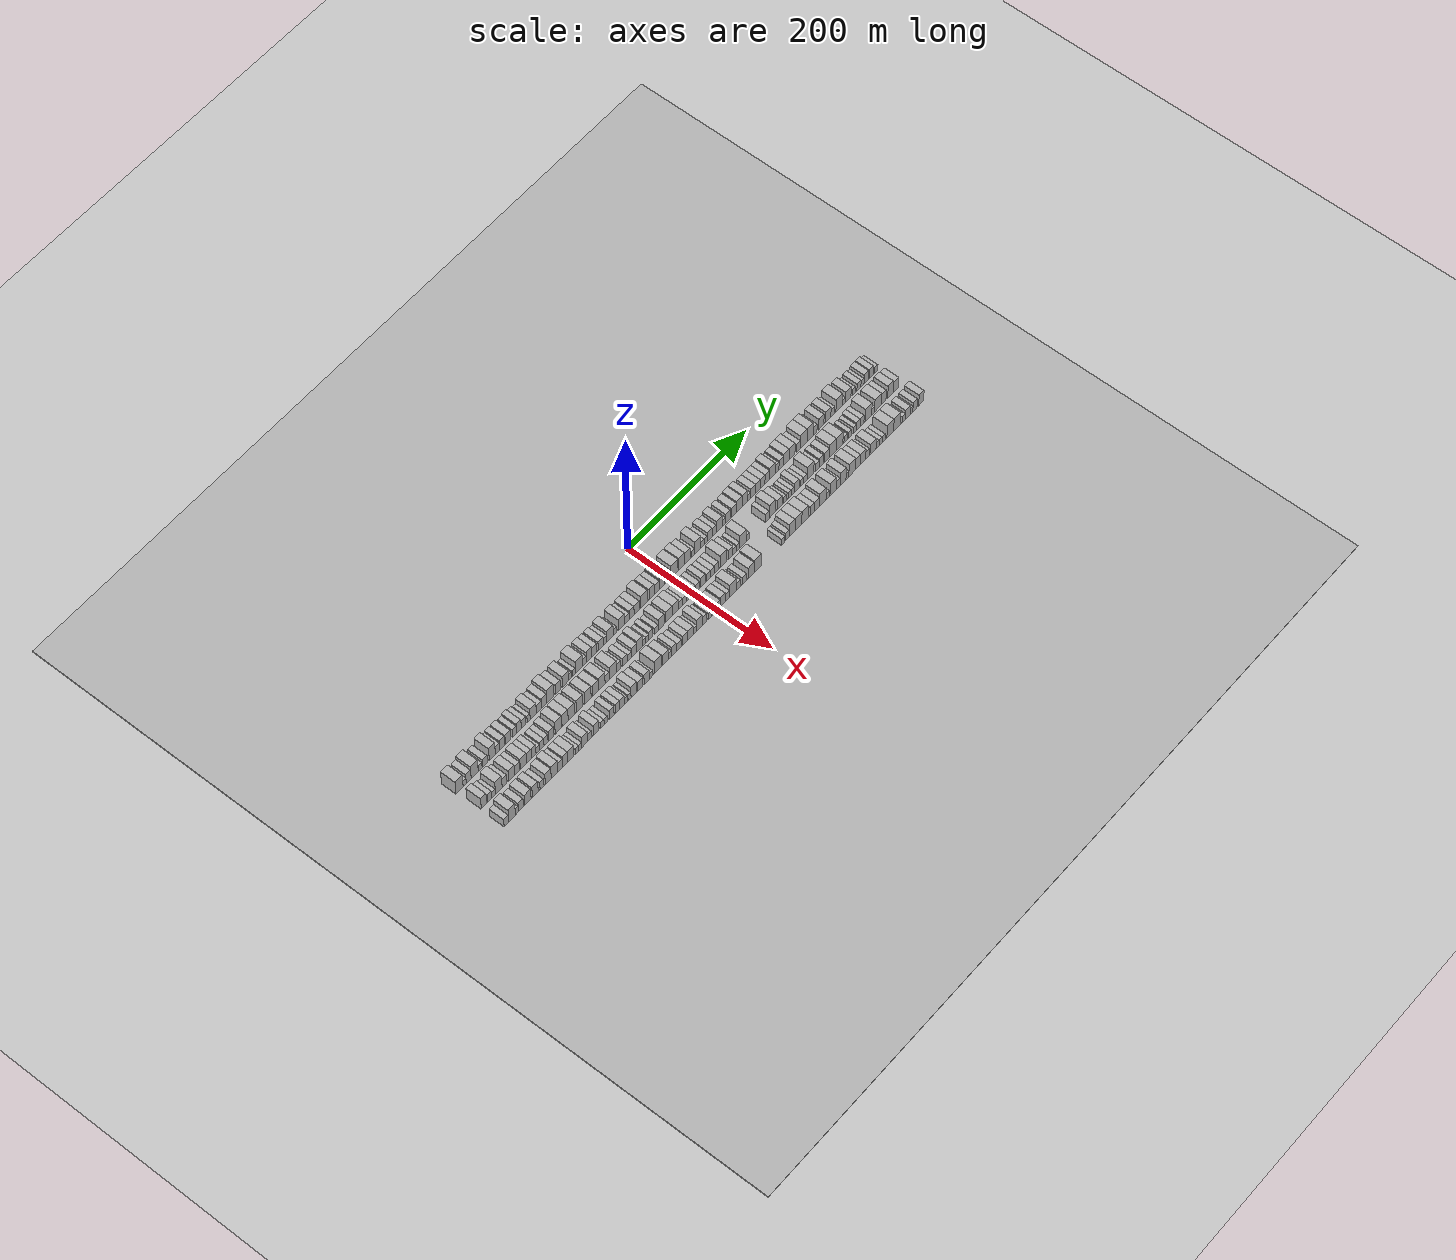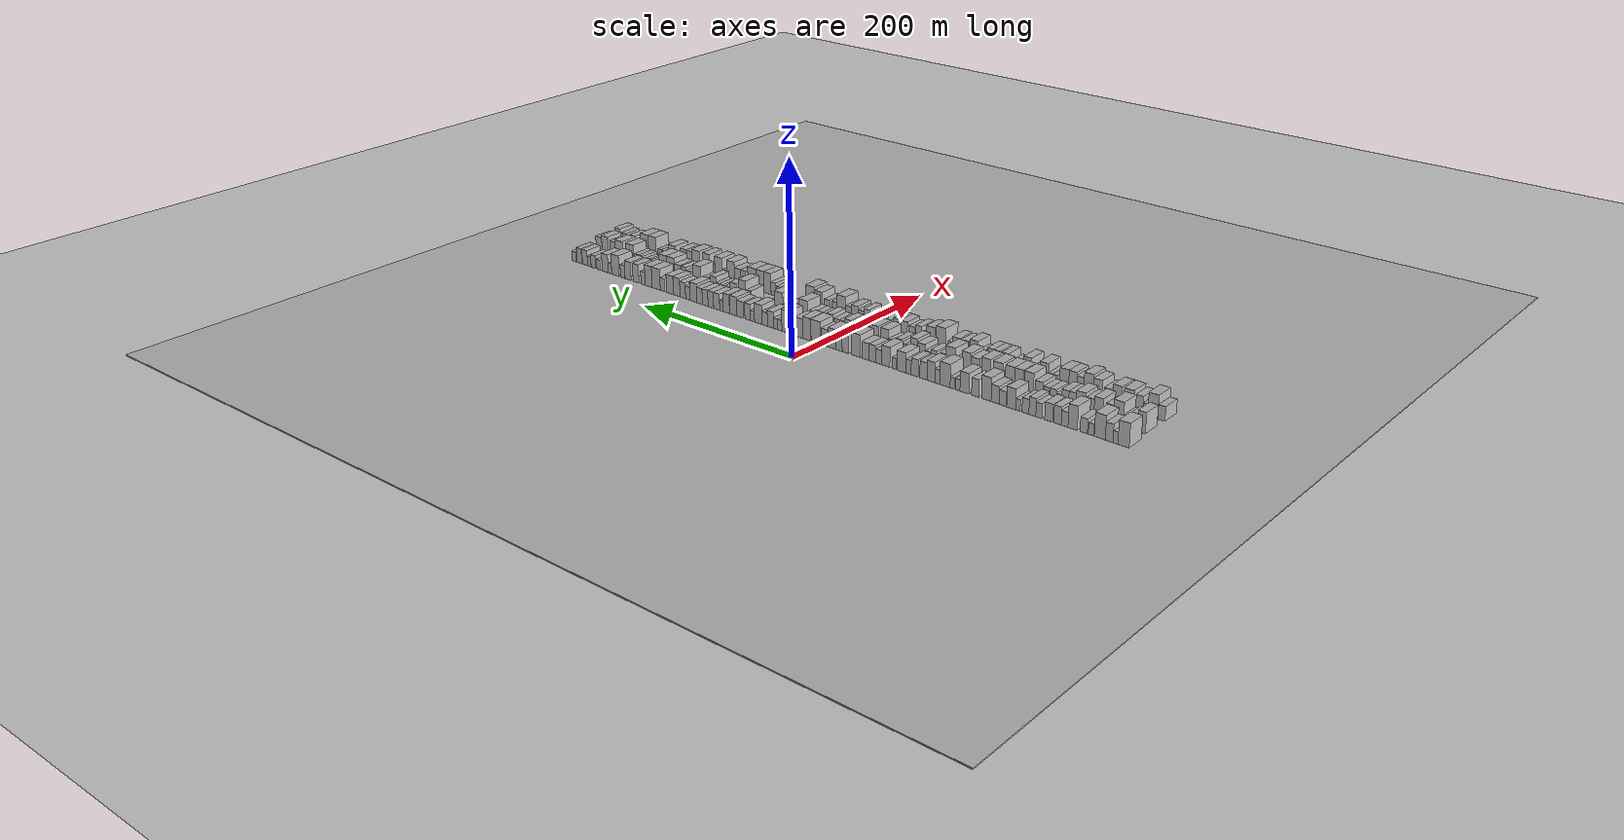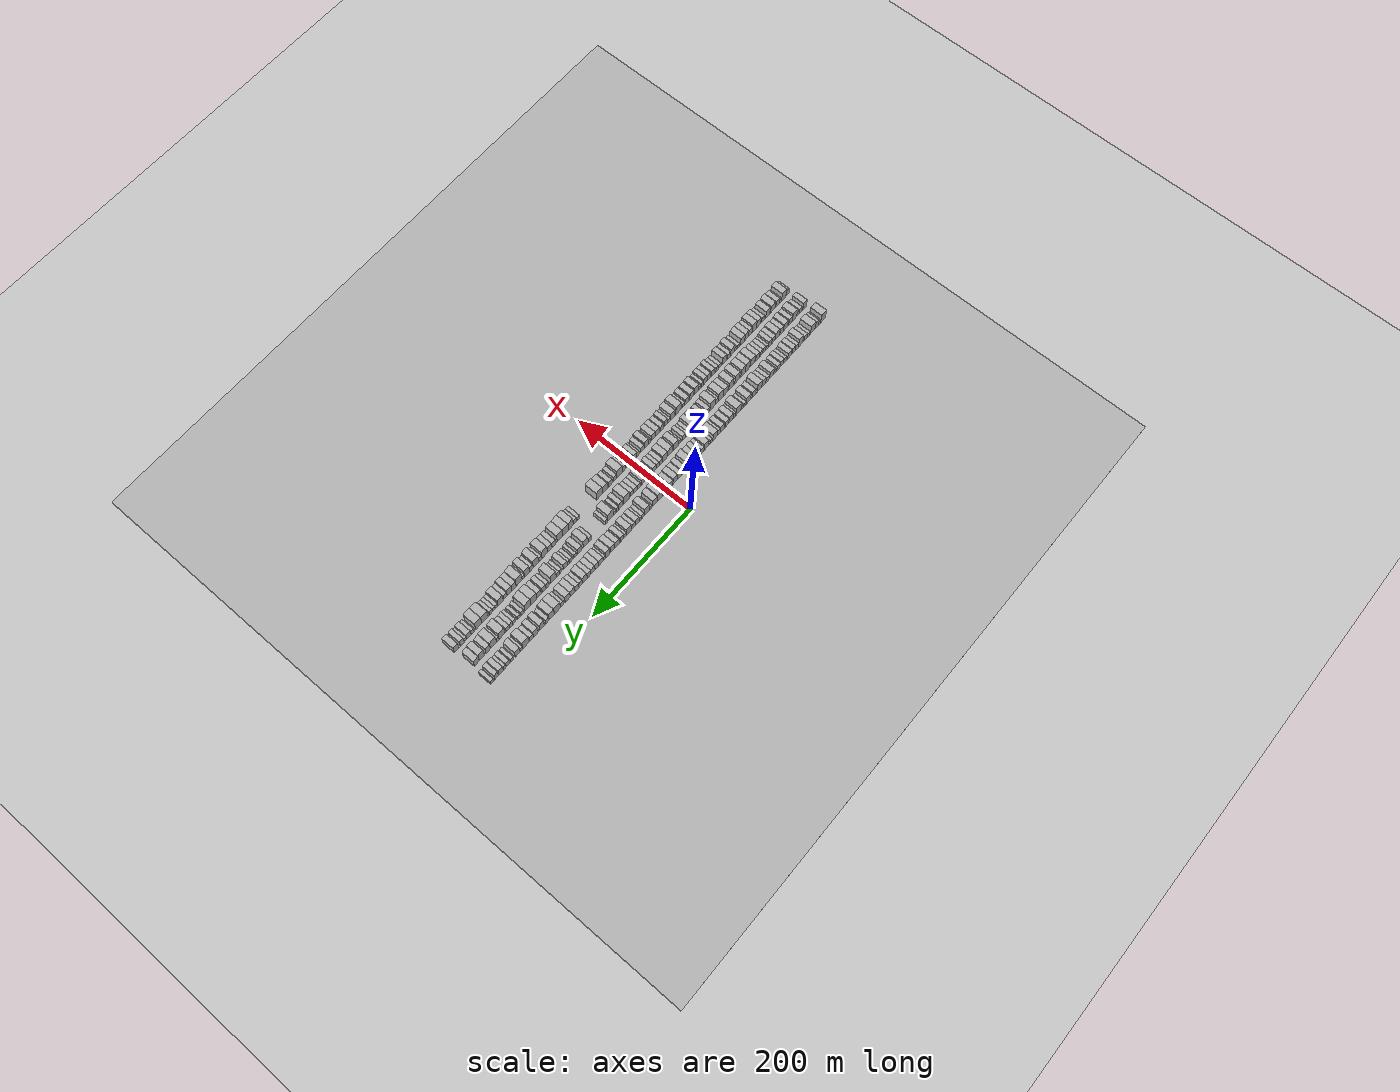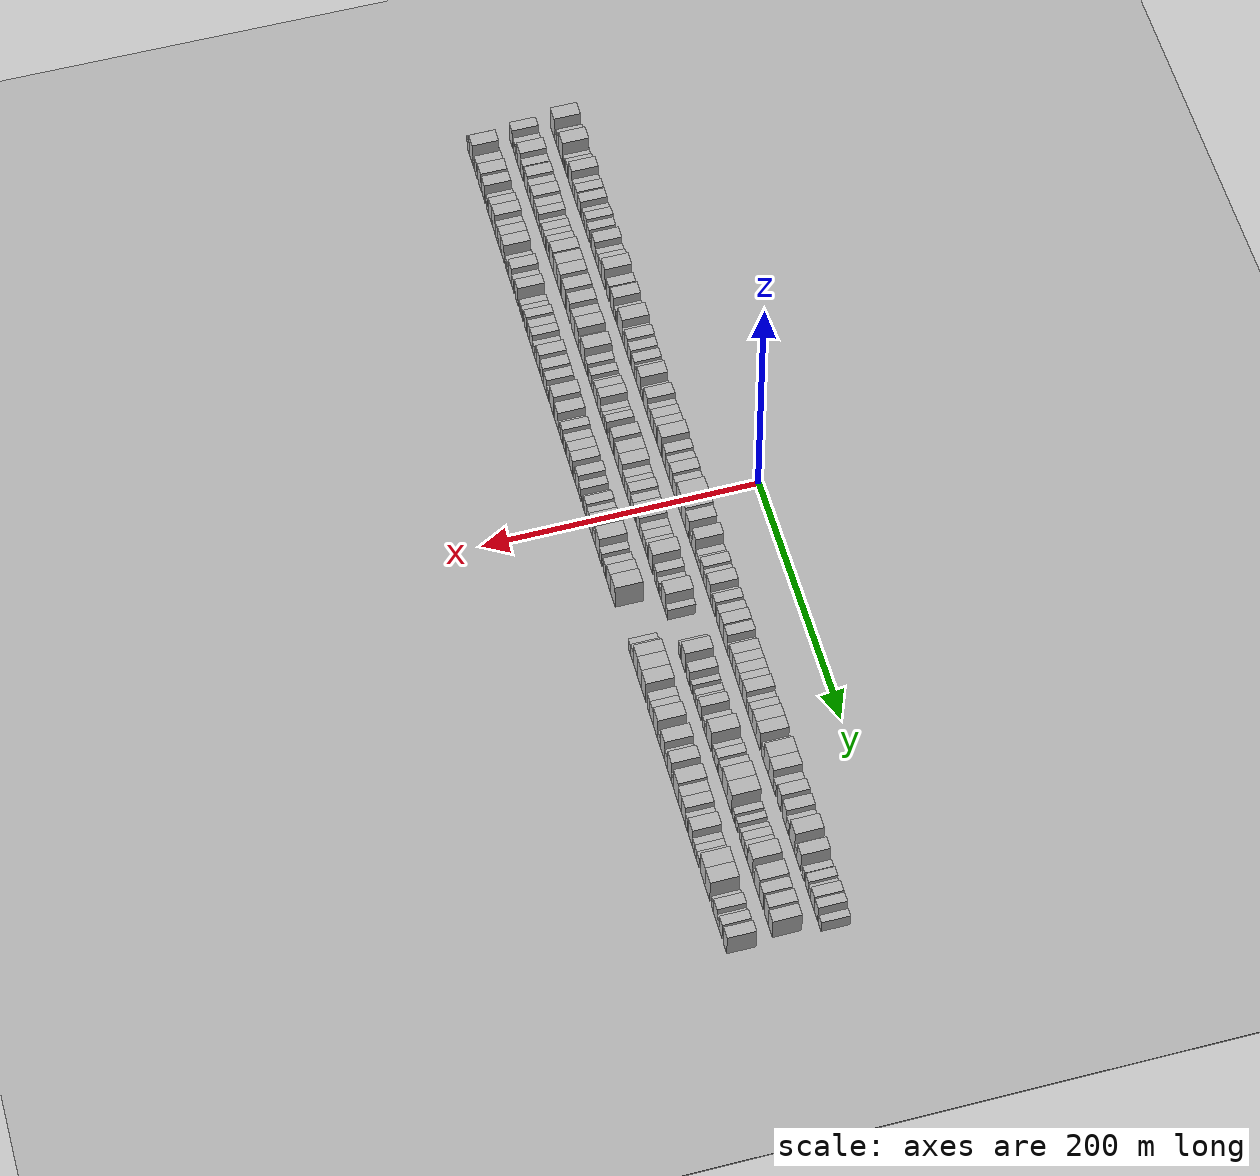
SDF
<?xml version="1.0" encoding="utf-8"?>

<sdf version="1.6">

   <world name="default">

      <gui fullscreen="0">

         <camera name="user_camera">

            <pose>-15 0 4.57585 0 0 0</pose>

            <view_controller>orbit</view_controller>

         </camera>

      </gui>

      <scene>

         <sky>

           <clouds>

             <speed>12</speed>

           </clouds>

         </sky>

         <ambient>0.4 0.4 0.4 1</ambient>

         <background>0.7 0.7 0.7 1</background>

         <shadows>1</shadows>

      </scene>

      <gravity>0 0 -9.8066</gravity>

      <magnetic_field>6e-06 2.3e-05 -4.2e-05</magnetic_field>

      <physics default="0" name="default_physics" type="ode">

         <ode>

            <solver>

               <type>quick</type>

               <iters>10</iters>

               <sor>1.0</sor>

               <use_dynamic_moi_rescaling>0</use_dynamic_moi_rescaling>

            </solver>

            <constraints>

               <cfm>0</cfm>

               <erp>0.2</erp>

               <contact_max_correcting_vel>100</contact_max_correcting_vel>

               <contact_surface_layer>0.001</contact_surface_layer>

            </constraints>

         </ode>

         <max_step_size>0.004</max_step_size>

         <real_time_factor>1</real_time_factor>

         <real_time_update_rate>250</real_time_update_rate>

      </physics>

      <light name="sun" type="directional">

         <cast_shadows>1</cast_shadows>

         <pose>0 0 10 0 0 0</pose>

         <diffuse>0.8 0.8 0.8 1</diffuse>

         <specular>0.2 0.2 0.2 1</specular>

         <attenuation>

            <range>1000</range>

            <constant>0.9</constant>

            <linear>0.01</linear>

            <quadratic>0.001</quadratic>

         </attenuation>

         <direction>-0.5 0.1 -0.9</direction>

      </light>

      <include>

         <name>ground_plane_1</name>

         <uri>model://HANNAS_ground_plane</uri>

         <pose>0 0 0  0 0 0</pose>

      </include>

      <include>

         <name>ground_plane_2</name>

         <uri>model://HANNAS_ground_plane</uri>

         <pose>100 0 0  0 0 0</pose>

      </include>

      <model name="building_1">

         <static>1</static>

         <pose frame="">50.0000 -342.3890 0 0.000000 0.000000 0.000000</pose>

         <link name="link">

            <pose frame="">0 0 12.00 0 0 0</pose>

            <collision name="collision">

               <geometry>

                  <box>

                     <size>20.0000 11.2219 24.0000</size>

                  </box>

               </geometry>

               <max_contacts>10</max_contacts>

               <surface>

                  <contact>

                     <ode/>

                  </contact>

                  <bounce/>

                  <friction>

                     <torsional>

                        <ode/>

                     </torsional>

                     <ode/>

                  </friction>

               </surface>

            </collision>

            <visual name="visual">

               <cast_shadows>0</cast_shadows>

               <geometry>

                  <box>

                     <size>20.0000 11.2219 24.0000</size>

                  </box>

               </geometry>

               <material>

                  <script>

                     <uri>model://HANNAS_wall/materials/scripts</uri>

                     <uri>model://HANNAS_wall/materials/textures</uri>

                     <name>vrc/HANNAS_wall</name>

                  </script>

               </material>

            </visual>

            <self_collide>0</self_collide>

            <enable_wind>0</enable_wind>

            <kinematic>0</kinematic>

         </link>

      </model>

      <model name="building_2">

         <static>1</static>

         <pose frame="">50.0000 -334.2786 0 0.000000 0.000000 0.000000</pose>

         <link name="link">

            <pose frame="">0 0 6.00 0 0 0</pose>

            <collision name="collision">

               <geometry>

                  <box>

                     <size>20.0000 4.9989 12.0000</size>

                  </box>

               </geometry>

               <max_contacts>10</max_contacts>

               <surface>

                  <contact>

                     <ode/>

                  </contact>

                  <bounce/>

                  <friction>

                     <torsional>

                        <ode/>

                     </torsional>

                     <ode/>

                  </friction>

               </surface>

            </collision>

            <visual name="visual">

               <cast_shadows>0</cast_shadows>

               <geometry>

                  <box>

                     <size>20.0000 4.9989 12.0000</size>

                  </box>

               </geometry>

               <material>

                  <script>

                     <uri>model://HANNAS_wall/materials/scripts</uri>

                     <uri>model://HANNAS_wall/materials/textures</uri>

                     <name>vrc/HANNAS_wall</name>

                  </script>

               </material>

            </visual>

            <self_collide>0</self_collide>

            <enable_wind>0</enable_wind>

            <kinematic>0</kinematic>

         </link>

      </model>

      <model name="building_3">

         <static>1</static>

         <pose frame="">50.0000 -327.9115 0 0.000000 0.000000 0.000000</pose>

         <link name="link">

            <pose frame="">0 0 9.00 0 0 0</pose>

            <collision name="collision">

               <geometry>

                  <box>

                     <size>20.0000 7.7354 18.0000</size>

                  </box>

               </geometry>

               <max_contacts>10</max_contacts>

               <surface>

                  <contact>

                     <ode/>

                  </contact>

                  <bounce/>

                  <friction>

                     <torsional>

                        <ode/>

                     </torsional>

                     <ode/>

                  </friction>

               </surface>

            </collision>

            <visual name="visual">

               <cast_shadows>0</cast_shadows>

               <geometry>

                  <box>

                     <size>20.0000 7.7354 18.0000</size>

                  </box>

               </geometry>

               <material>

                  <script>

                     <uri>model://HANNAS_wall/materials/scripts</uri>

                     <uri>model://HANNAS_wall/materials/textures</uri>

                     <name>vrc/HANNAS_wall</name>

                  </script>

               </material>

            </visual>

            <self_collide>0</self_collide>

            <enable_wind>0</enable_wind>

            <kinematic>0</kinematic>

         </link>

      </model>

      <model name="building_4">

         <static>1</static>

         <pose frame="">50.0000 -318.4822 0 0.000000 0.000000 0.000000</pose>

         <link name="link">

            <pose frame="">0 0 12.00 0 0 0</pose>

            <collision name="collision">

               <geometry>

                  <box>

                     <size>20.0000 11.1232 24.0000</size>

                  </box>

               </geometry>

               <max_contacts>10</max_contacts>

               <surface>

                  <contact>

                     <ode/>

                  </contact>

                  <bounce/>

                  <friction>

                     <torsional>

                        <ode/>

                     </torsional>

                     <ode/>

                  </friction>

               </surface>

            </collision>

            <visual name="visual">

               <cast_shadows>0</cast_shadows>

               <geometry>

                  <box>

                     <size>20.0000 11.1232 24.0000</size>

                  </box>

               </geometry>

               <material>

                  <script>

                     <uri>model://HANNAS_wall/materials/scripts</uri>

                     <uri>model://HANNAS_wall/materials/textures</uri>

                     <name>vrc/HANNAS_wall</name>

                  </script>

               </material>

            </visual>

            <self_collide>0</self_collide>

            <enable_wind>0</enable_wind>

            <kinematic>0</kinematic>

         </link>

      </model>

      <model name="building_5">

         <static>1</static>

         <pose frame="">50.0000 -309.3648 0 0.000000 0.000000 0.000000</pose>

         <link name="link">

            <pose frame="">0 0 6.00 0 0 0</pose>

            <collision name="collision">

               <geometry>

                  <box>

                     <size>20.0000 5.1116 12.0000</size>

                  </box>

               </geometry>

               <max_contacts>10</max_contacts>

               <surface>

                  <contact>

                     <ode/>

                  </contact>

                  <bounce/>

                  <friction>

                     <torsional>

                        <ode/>

                     </torsional>

                     <ode/>

                  </friction>

               </surface>

            </collision>

            <visual name="visual">

               <cast_shadows>0</cast_shadows>

               <geometry>

                  <box>

                     <size>20.0000 5.1116 12.0000</size>

                  </box>

               </geometry>

               <material>

                  <script>

                     <uri>model://HANNAS_wall/materials/scripts</uri>

                     <uri>model://HANNAS_wall/materials/textures</uri>

                     <name>vrc/HANNAS_wall</name>

                  </script>

               </material>

            </visual>

            <self_collide>0</self_collide>

            <enable_wind>0</enable_wind>

            <kinematic>0</kinematic>

         </link>

      </model>

      <model name="building_6">

         <static>1</static>

         <pose frame="">50.0000 -302.1212 0 0.000000 0.000000 0.000000</pose>

         <link name="link">

            <pose frame="">0 0 7.50 0 0 0</pose>

            <collision name="collision">

               <geometry>

                  <box>

                     <size>20.0000 7.3756 15.0000</size>

                  </box>

               </geometry>

               <max_contacts>10</max_contacts>

               <surface>

                  <contact>

                     <ode/>

                  </contact>

                  <bounce/>

                  <friction>

                     <torsional>

                        <ode/>

                     </torsional>

                     <ode/>

                  </friction>

               </surface>

            </collision>

            <visual name="visual">

               <cast_shadows>0</cast_shadows>

               <geometry>

                  <box>

                     <size>20.0000 7.3756 15.0000</size>

                  </box>

               </geometry>

               <material>

                  <script>

                     <uri>model://HANNAS_wall/materials/scripts</uri>

                     <uri>model://HANNAS_wall/materials/textures</uri>

                     <name>vrc/HANNAS_wall</name>

                  </script>

               </material>

            </visual>

            <self_collide>0</self_collide>

            <enable_wind>0</enable_wind>

            <kinematic>0</kinematic>

         </link>

      </model>

      <model name="building_7">

         <static>1</static>

         <pose frame="">50.0000 -290.6306 0 0.000000 0.000000 0.000000</pose>

         <link name="link">

            <pose frame="">0 0 12.00 0 0 0</pose>

            <collision name="collision">

               <geometry>

                  <box>

                     <size>20.0000 9.6056 24.0000</size>

                  </box>

               </geometry>

               <max_contacts>10</max_contacts>

               <surface>

                  <contact>

                     <ode/>

                  </contact>

                  <bounce/>

                  <friction>

                     <torsional>

                        <ode/>

                     </torsional>

                     <ode/>

                  </friction>

               </surface>

            </collision>

            <visual name="visual">

               <cast_shadows>0</cast_shadows>

               <geometry>

                  <box>

                     <size>20.0000 9.6056 24.0000</size>

                  </box>

               </geometry>

               <material>

                  <script>

                     <uri>model://HANNAS_wall/materials/scripts</uri>

                     <uri>model://HANNAS_wall/materials/textures</uri>

                     <name>vrc/HANNAS_wall</name>

                  </script>

               </material>

            </visual>

            <self_collide>0</self_collide>

            <enable_wind>0</enable_wind>

            <kinematic>0</kinematic>

         </link>

      </model>

      <model name="building_8">

         <static>1</static>

         <pose frame="">50.0000 -282.3117 0 0.000000 0.000000 0.000000</pose>

         <link name="link">

            <pose frame="">0 0 7.50 0 0 0</pose>

            <collision name="collision">

               <geometry>

                  <box>

                     <size>20.0000 7.0321 15.0000</size>

                  </box>

               </geometry>

               <max_contacts>10</max_contacts>

               <surface>

                  <contact>

                     <ode/>

                  </contact>

                  <bounce/>

                  <friction>

                     <torsional>

                        <ode/>

                     </torsional>

                     <ode/>

                  </friction>

               </surface>

            </collision>

            <visual name="visual">

               <cast_shadows>0</cast_shadows>

               <geometry>

                  <box>

                     <size>20.0000 7.0321 15.0000</size>

                  </box>

               </geometry>

               <material>

                  <script>

                     <uri>model://HANNAS_wall/materials/scripts</uri>

                     <uri>model://HANNAS_wall/materials/textures</uri>

                     <name>vrc/HANNAS_wall</name>

                  </script>

               </material>

            </visual>

            <self_collide>0</self_collide>

            <enable_wind>0</enable_wind>

            <kinematic>0</kinematic>

         </link>

      </model>

      <model name="building_9">

         <static>1</static>

         <pose frame="">50.0000 -274.8525 0 0.000000 0.000000 0.000000</pose>

         <link name="link">

            <pose frame="">0 0 9.00 0 0 0</pose>

            <collision name="collision">

               <geometry>

                  <box>

                     <size>20.0000 7.8862 18.0000</size>

                  </box>

               </geometry>

               <max_contacts>10</max_contacts>

               <surface>

                  <contact>

                     <ode/>

                  </contact>

                  <bounce/>

                  <friction>

                     <torsional>

                        <ode/>

                     </torsional>

                     <ode/>

                  </friction>

               </surface>

            </collision>

            <visual name="visual">

               <cast_shadows>0</cast_shadows>

               <geometry>

                  <box>

                     <size>20.0000 7.8862 18.0000</size>

                  </box>

               </geometry>

               <material>

                  <script>

                     <uri>model://HANNAS_wall/materials/scripts</uri>

                     <uri>model://HANNAS_wall/materials/textures</uri>

                     <name>vrc/HANNAS_wall</name>

                  </script>

               </material>

            </visual>

            <self_collide>0</self_collide>

            <enable_wind>0</enable_wind>

            <kinematic>0</kinematic>

         </link>

      </model>

      <model name="building_10">

         <static>1</static>

         <pose frame="">50.0000 -265.6022 0 0.000000 0.000000 0.000000</pose>

         <link name="link">

            <pose frame="">0 0 9.00 0 0 0</pose>

            <collision name="collision">

               <geometry>

                  <box>

                     <size>20.0000 8.6145 18.0000</size>

                  </box>

               </geometry>

               <max_contacts>10</max_contacts>

               <surface>

                  <contact>

                     <ode/>

                  </contact>

                  <bounce/>

                  <friction>

                     <torsional>

                        <ode/>

                     </torsional>

                     <ode/>

                  </friction>

               </surface>

            </collision>

            <visual name="visual">

               <cast_shadows>0</cast_shadows>

               <geometry>

                  <box>

                     <size>20.0000 8.6145 18.0000</size>

                  </box>

               </geometry>

               <material>

                  <script>

                     <uri>model://HANNAS_wall/materials/scripts</uri>

                     <uri>model://HANNAS_wall/materials/textures</uri>

                     <name>vrc/HANNAS_wall</name>

                  </script>

               </material>

            </visual>

            <self_collide>0</self_collide>

            <enable_wind>0</enable_wind>

            <kinematic>0</kinematic>

         </link>

      </model>

      <model name="building_11">

         <static>1</static>

         <pose frame="">50.0000 -255.1250 0 0.000000 0.000000 0.000000</pose>

         <link name="link">

            <pose frame="">0 0 7.50 0 0 0</pose>

            <collision name="collision">

               <geometry>

                  <box>

                     <size>20.0000 6.3397 15.0000</size>

                  </box>

               </geometry>

               <max_contacts>10</max_contacts>

               <surface>

                  <contact>

                     <ode/>

                  </contact>

                  <bounce/>

                  <friction>

                     <torsional>

                        <ode/>

                     </torsional>

                     <ode/>

                  </friction>

               </surface>

            </collision>

            <visual name="visual">

               <cast_shadows>0</cast_shadows>

               <geometry>

                  <box>

                     <size>20.0000 6.3397 15.0000</size>

                  </box>

               </geometry>

               <material>

                  <script>

                     <uri>model://HANNAS_wall/materials/scripts</uri>

                     <uri>model://HANNAS_wall/materials/textures</uri>

                     <name>vrc/HANNAS_wall</name>

                  </script>

               </material>

            </visual>

            <self_collide>0</self_collide>

            <enable_wind>0</enable_wind>

            <kinematic>0</kinematic>

         </link>

      </model>

      <model name="building_12">

         <static>1</static>

         <pose frame="">50.0000 -248.2621 0 0.000000 0.000000 0.000000</pose>

         <link name="link">

            <pose frame="">0 0 9.00 0 0 0</pose>

            <collision name="collision">

               <geometry>

                  <box>

                     <size>20.0000 7.3861 18.0000</size>

                  </box>

               </geometry>

               <max_contacts>10</max_contacts>

               <surface>

                  <contact>

                     <ode/>

                  </contact>

                  <bounce/>

                  <friction>

                     <torsional>

                        <ode/>

                     </torsional>

                     <ode/>

                  </friction>

               </surface>

            </collision>

            <visual name="visual">

               <cast_shadows>0</cast_shadows>

               <geometry>

                  <box>

                     <size>20.0000 7.3861 18.0000</size>

                  </box>

               </geometry>

               <material>

                  <script>

                     <uri>model://HANNAS_wall/materials/scripts</uri>

                     <uri>model://HANNAS_wall/materials/textures</uri>

                     <name>vrc/HANNAS_wall</name>

                  </script>

               </material>

            </visual>

            <self_collide>0</self_collide>

            <enable_wind>0</enable_wind>

            <kinematic>0</kinematic>

         </link>

      </model>

      <model name="building_13">

         <static>1</static>

         <pose frame="">50.0000 -240.8687 0 0.000000 0.000000 0.000000</pose>

         <link name="link">

            <pose frame="">0 0 7.50 0 0 0</pose>

            <collision name="collision">

               <geometry>

                  <box>

                     <size>20.0000 7.4008 15.0000</size>

                  </box>

               </geometry>

               <max_contacts>10</max_contacts>

               <surface>

                  <contact>

                     <ode/>

                  </contact>

                  <bounce/>

                  <friction>

                     <torsional>

                        <ode/>

                     </torsional>

                     <ode/>

                  </friction>

               </surface>

            </collision>

            <visual name="visual">

               <cast_shadows>0</cast_shadows>

               <geometry>

                  <box>

                     <size>20.0000 7.4008 15.0000</size>

                  </box>

               </geometry>

               <material>

                  <script>

                     <uri>model://HANNAS_wall/materials/scripts</uri>

                     <uri>model://HANNAS_wall/materials/textures</uri>

                     <name>vrc/HANNAS_wall</name>

                  </script>

               </material>

            </visual>

            <self_collide>0</self_collide>

            <enable_wind>0</enable_wind>

            <kinematic>0</kinematic>

         </link>

      </model>

      <model name="building_14">

         <static>1</static>

         <pose frame="">50.0000 -232.7441 0 0.000000 0.000000 0.000000</pose>

         <link name="link">

            <pose frame="">0 0 6.00 0 0 0</pose>

            <collision name="collision">

               <geometry>

                  <box>

                     <size>20.0000 4.8483 12.0000</size>

                  </box>

               </geometry>

               <max_contacts>10</max_contacts>

               <surface>

                  <contact>

                     <ode/>

                  </contact>

                  <bounce/>

                  <friction>

                     <torsional>

                        <ode/>

                     </torsional>

                     <ode/>

                  </friction>

               </surface>

            </collision>

            <visual name="visual">

               <cast_shadows>0</cast_shadows>

               <geometry>

                  <box>

                     <size>20.0000 4.8483 12.0000</size>

                  </box>

               </geometry>

               <material>

                  <script>

                     <uri>model://HANNAS_wall/materials/scripts</uri>

                     <uri>model://HANNAS_wall/materials/textures</uri>

                     <name>vrc/HANNAS_wall</name>

                  </script>

               </material>

            </visual>

            <self_collide>0</self_collide>

            <enable_wind>0</enable_wind>

            <kinematic>0</kinematic>

         </link>

      </model>

      <model name="building_15">

         <static>1</static>

         <pose frame="">50.0000 -225.4259 0 0.000000 0.000000 0.000000</pose>

         <link name="link">

            <pose frame="">0 0 10.50 0 0 0</pose>

            <collision name="collision">

               <geometry>

                  <box>

                     <size>20.0000 9.7881 21.0000</size>

                  </box>

               </geometry>

               <max_contacts>10</max_contacts>

               <surface>

                  <contact>

                     <ode/>

                  </contact>

                  <bounce/>

                  <friction>

                     <torsional>

                        <ode/>

                     </torsional>

                     <ode/>

                  </friction>

               </surface>

            </collision>

            <visual name="visual">

               <cast_shadows>0</cast_shadows>

               <geometry>

                  <box>

                     <size>20.0000 9.7881 21.0000</size>

                  </box>

               </geometry>

               <material>

                  <script>

                     <uri>model://HANNAS_wall/materials/scripts</uri>

                     <uri>model://HANNAS_wall/materials/textures</uri>

                     <name>vrc/HANNAS_wall</name>

                  </script>

               </material>

            </visual>

            <self_collide>0</self_collide>

            <enable_wind>0</enable_wind>

            <kinematic>0</kinematic>

         </link>

      </model>

      <model name="building_16">

         <static>1</static>

         <pose frame="">50.0000 -215.8226 0 0.000000 0.000000 0.000000</pose>

         <link name="link">

            <pose frame="">0 0 7.50 0 0 0</pose>

            <collision name="collision">

               <geometry>

                  <box>

                     <size>20.0000 7.4185 15.0000</size>

                  </box>

               </geometry>

               <max_contacts>10</max_contacts>

               <surface>

                  <contact>

                     <ode/>

                  </contact>

                  <bounce/>

                  <friction>

                     <torsional>

                        <ode/>

                     </torsional>

                     <ode/>

                  </friction>

               </surface>

            </collision>

            <visual name="visual">

               <cast_shadows>0</cast_shadows>

               <geometry>

                  <box>

                     <size>20.0000 7.4185 15.0000</size>

                  </box>

               </geometry>

               <material>

                  <script>

                     <uri>model://HANNAS_wall/materials/scripts</uri>

                     <uri>model://HANNAS_wall/materials/textures</uri>

                     <name>vrc/HANNAS_wall</name>

                  </script>

               </material>

            </visual>

            <self_collide>0</self_collide>

            <enable_wind>0</enable_wind>

            <kinematic>0</kinematic>

         </link>

      </model>

      <model name="building_17">

         <static>1</static>

         <pose frame="">50.0000 -207.7603 0 0.000000 0.000000 0.000000</pose>

         <link name="link">

            <pose frame="">0 0 9.00 0 0 0</pose>

            <collision name="collision">

               <geometry>

                  <box>

                     <size>20.0000 8.7060 18.0000</size>

                  </box>

               </geometry>

               <max_contacts>10</max_contacts>

               <surface>

                  <contact>

                     <ode/>

                  </contact>

                  <bounce/>

                  <friction>

                     <torsional>

                        <ode/>

                     </torsional>

                     <ode/>

                  </friction>

               </surface>

            </collision>

            <visual name="visual">

               <cast_shadows>0</cast_shadows>

               <geometry>

                  <box>

                     <size>20.0000 8.7060 18.0000</size>

                  </box>

               </geometry>

               <material>

                  <script>

                     <uri>model://HANNAS_wall/materials/scripts</uri>

                     <uri>model://HANNAS_wall/materials/textures</uri>

                     <name>vrc/HANNAS_wall</name>

                  </script>

               </material>

            </visual>

            <self_collide>0</self_collide>

            <enable_wind>0</enable_wind>

            <kinematic>0</kinematic>

         </link>

      </model>

      <model name="building_18">

         <static>1</static>

         <pose frame="">50.0000 -198.1202 0 0.000000 0.000000 0.000000</pose>

         <link name="link">

            <pose frame="">0 0 12.00 0 0 0</pose>

            <collision name="collision">

               <geometry>

                  <box>

                     <size>20.0000 10.5743 24.0000</size>

                  </box>

               </geometry>

               <max_contacts>10</max_contacts>

               <surface>

                  <contact>

                     <ode/>

                  </contact>

                  <bounce/>

                  <friction>

                     <torsional>

                        <ode/>

                     </torsional>

                     <ode/>

                  </friction>

               </surface>

            </collision>

            <visual name="visual">

               <cast_shadows>0</cast_shadows>

               <geometry>

                  <box>

                     <size>20.0000 10.5743 24.0000</size>

                  </box>

               </geometry>

               <material>

                  <script>

                     <uri>model://HANNAS_wall/materials/scripts</uri>

                     <uri>model://HANNAS_wall/materials/textures</uri>

                     <name>vrc/HANNAS_wall</name>

                  </script>

               </material>

            </visual>

            <self_collide>0</self_collide>

            <enable_wind>0</enable_wind>

            <kinematic>0</kinematic>

         </link>

      </model>

      <model name="building_19">

         <static>1</static>

         <pose frame="">50.0000 -185.7097 0 0.000000 0.000000 0.000000</pose>

         <link name="link">

            <pose frame="">0 0 9.00 0 0 0</pose>

            <collision name="collision">

               <geometry>

                  <box>

                     <size>20.0000 8.2468 18.0000</size>

                  </box>

               </geometry>

               <max_contacts>10</max_contacts>

               <surface>

                  <contact>

                     <ode/>

                  </contact>

                  <bounce/>

                  <friction>

                     <torsional>

                        <ode/>

                     </torsional>

                     <ode/>

                  </friction>

               </surface>

            </collision>

            <visual name="visual">

               <cast_shadows>0</cast_shadows>

               <geometry>

                  <box>

                     <size>20.0000 8.2468 18.0000</size>

                  </box>

               </geometry>

               <material>

                  <script>

                     <uri>model://HANNAS_wall/materials/scripts</uri>

                     <uri>model://HANNAS_wall/materials/textures</uri>

                     <name>vrc/HANNAS_wall</name>

                  </script>

               </material>

            </visual>

            <self_collide>0</self_collide>

            <enable_wind>0</enable_wind>

            <kinematic>0</kinematic>

         </link>

      </model>

      <model name="building_20">

         <static>1</static>

         <pose frame="">50.0000 -173.5333 0 0.000000 0.000000 0.000000</pose>

         <link name="link">

            <pose frame="">0 0 10.50 0 0 0</pose>

            <collision name="collision">

               <geometry>

                  <box>

                     <size>20.0000 10.1059 21.0000</size>

                  </box>

               </geometry>

               <max_contacts>10</max_contacts>

               <surface>

                  <contact>

                     <ode/>

                  </contact>

                  <bounce/>

                  <friction>

                     <torsional>

                        <ode/>

                     </torsional>

                     <ode/>

                  </friction>

               </surface>

            </collision>

            <visual name="visual">

               <cast_shadows>0</cast_shadows>

               <geometry>

                  <box>

                     <size>20.0000 10.1059 21.0000</size>

                  </box>

               </geometry>

               <material>

                  <script>

                     <uri>model://HANNAS_wall/materials/scripts</uri>

                     <uri>model://HANNAS_wall/materials/textures</uri>

                     <name>vrc/HANNAS_wall</name>

                  </script>

               </material>

            </visual>

            <self_collide>0</self_collide>

            <enable_wind>0</enable_wind>

            <kinematic>0</kinematic>

         </link>

      </model>

      <model name="building_21">

         <static>1</static>

         <pose frame="">50.0000 -165.9133 0 0.000000 0.000000 0.000000</pose>

         <link name="link">

            <pose frame="">0 0 6.00 0 0 0</pose>

            <collision name="collision">

               <geometry>

                  <box>

                     <size>20.0000 5.1343 12.0000</size>

                  </box>

               </geometry>

               <max_contacts>10</max_contacts>

               <surface>

                  <contact>

                     <ode/>

                  </contact>

                  <bounce/>

                  <friction>

                     <torsional>

                        <ode/>

                     </torsional>

                     <ode/>

                  </friction>

               </surface>

            </collision>

            <visual name="visual">

               <cast_shadows>0</cast_shadows>

               <geometry>

                  <box>

                     <size>20.0000 5.1343 12.0000</size>

                  </box>

               </geometry>

               <material>

                  <script>

                     <uri>model://HANNAS_wall/materials/scripts</uri>

                     <uri>model://HANNAS_wall/materials/textures</uri>

                     <name>vrc/HANNAS_wall</name>

                  </script>

               </material>

            </visual>

            <self_collide>0</self_collide>

            <enable_wind>0</enable_wind>

            <kinematic>0</kinematic>

         </link>

      </model>

      <model name="building_22">

         <static>1</static>

         <pose frame="">50.0000 -159.8497 0 0.000000 0.000000 0.000000</pose>

         <link name="link">

            <pose frame="">0 0 6.00 0 0 0</pose>

            <collision name="collision">

               <geometry>

                  <box>

                     <size>20.0000 4.9928 12.0000</size>

                  </box>

               </geometry>

               <max_contacts>10</max_contacts>

               <surface>

                  <contact>

                     <ode/>

                  </contact>

                  <bounce/>

                  <friction>

                     <torsional>

                        <ode/>

                     </torsional>

                     <ode/>

                  </friction>

               </surface>

            </collision>

            <visual name="visual">

               <cast_shadows>0</cast_shadows>

               <geometry>

                  <box>

                     <size>20.0000 4.9928 12.0000</size>

                  </box>

               </geometry>

               <material>

                  <script>

                     <uri>model://HANNAS_wall/materials/scripts</uri>

                     <uri>model://HANNAS_wall/materials/textures</uri>

                     <name>vrc/HANNAS_wall</name>

                  </script>

               </material>

            </visual>

            <self_collide>0</self_collide>

            <enable_wind>0</enable_wind>

            <kinematic>0</kinematic>

         </link>

      </model>

      <model name="building_23">

         <static>1</static>

         <pose frame="">50.0000 -151.5306 0 0.000000 0.000000 0.000000</pose>

         <link name="link">

            <pose frame="">0 0 12.00 0 0 0</pose>

            <collision name="collision">

               <geometry>

                  <box>

                     <size>20.0000 11.6453 24.0000</size>

                  </box>

               </geometry>

               <max_contacts>10</max_contacts>

               <surface>

                  <contact>

                     <ode/>

                  </contact>

                  <bounce/>

                  <friction>

                     <torsional>

                        <ode/>

                     </torsional>

                     <ode/>

                  </friction>

               </surface>

            </collision>

            <visual name="visual">

               <cast_shadows>0</cast_shadows>

               <geometry>

                  <box>

                     <size>20.0000 11.6453 24.0000</size>

                  </box>

               </geometry>

               <material>

                  <script>

                     <uri>model://HANNAS_wall/materials/scripts</uri>

                     <uri>model://HANNAS_wall/materials/textures</uri>

                     <name>vrc/HANNAS_wall</name>

                  </script>

               </material>

            </visual>

            <self_collide>0</self_collide>

            <enable_wind>0</enable_wind>

            <kinematic>0</kinematic>

         </link>

      </model>

      <model name="building_24">

         <static>1</static>

         <pose frame="">50.0000 -142.6795 0 0.000000 0.000000 0.000000</pose>

         <link name="link">

            <pose frame="">0 0 7.50 0 0 0</pose>

            <collision name="collision">

               <geometry>

                  <box>

                     <size>20.0000 6.0570 15.0000</size>

                  </box>

               </geometry>

               <max_contacts>10</max_contacts>

               <surface>

                  <contact>

                     <ode/>

                  </contact>

                  <bounce/>

                  <friction>

                     <torsional>

                        <ode/>

                     </torsional>

                     <ode/>

                  </friction>

               </surface>

            </collision>

            <visual name="visual">

               <cast_shadows>0</cast_shadows>

               <geometry>

                  <box>

                     <size>20.0000 6.0570 15.0000</size>

                  </box>

               </geometry>

               <material>

                  <script>

                     <uri>model://HANNAS_wall/materials/scripts</uri>

                     <uri>model://HANNAS_wall/materials/textures</uri>

                     <name>vrc/HANNAS_wall</name>

                  </script>

               </material>

            </visual>

            <self_collide>0</self_collide>

            <enable_wind>0</enable_wind>

            <kinematic>0</kinematic>

         </link>

      </model>

      <model name="building_25">

         <static>1</static>

         <pose frame="">50.0000 -135.1300 0 0.000000 0.000000 0.000000</pose>

         <link name="link">

            <pose frame="">0 0 10.50 0 0 0</pose>

            <collision name="collision">

               <geometry>

                  <box>

                     <size>20.0000 9.0420 21.0000</size>

                  </box>

               </geometry>

               <max_contacts>10</max_contacts>

               <surface>

                  <contact>

                     <ode/>

                  </contact>

                  <bounce/>

                  <friction>

                     <torsional>

                        <ode/>

                     </torsional>

                     <ode/>

                  </friction>

               </surface>

            </collision>

            <visual name="visual">

               <cast_shadows>0</cast_shadows>

               <geometry>

                  <box>

                     <size>20.0000 9.0420 21.0000</size>

                  </box>

               </geometry>

               <material>

                  <script>

                     <uri>model://HANNAS_wall/materials/scripts</uri>

                     <uri>model://HANNAS_wall/materials/textures</uri>

                     <name>vrc/HANNAS_wall</name>

                  </script>

               </material>

            </visual>

            <self_collide>0</self_collide>

            <enable_wind>0</enable_wind>

            <kinematic>0</kinematic>

         </link>

      </model>

      <model name="building_26">

         <static>1</static>

         <pose frame="">50.0000 -126.4680 0 0.000000 0.000000 0.000000</pose>

         <link name="link">

            <pose frame="">0 0 9.00 0 0 0</pose>

            <collision name="collision">

               <geometry>

                  <box>

                     <size>20.0000 8.2820 18.0000</size>

                  </box>

               </geometry>

               <max_contacts>10</max_contacts>

               <surface>

                  <contact>

                     <ode/>

                  </contact>

                  <bounce/>

                  <friction>

                     <torsional>

                        <ode/>

                     </torsional>

                     <ode/>

                  </friction>

               </surface>

            </collision>

            <visual name="visual">

               <cast_shadows>0</cast_shadows>

               <geometry>

                  <box>

                     <size>20.0000 8.2820 18.0000</size>

                  </box>

               </geometry>

               <material>

                  <script>

                     <uri>model://HANNAS_wall/materials/scripts</uri>

                     <uri>model://HANNAS_wall/materials/textures</uri>

                     <name>vrc/HANNAS_wall</name>

                  </script>

               </material>

            </visual>

            <self_collide>0</self_collide>

            <enable_wind>0</enable_wind>

            <kinematic>0</kinematic>

         </link>

      </model>

      <model name="building_27">

         <static>1</static>

         <pose frame="">50.0000 -116.2094 0 0.000000 0.000000 0.000000</pose>

         <link name="link">

            <pose frame="">0 0 9.00 0 0 0</pose>

            <collision name="collision">

               <geometry>

                  <box>

                     <size>20.0000 8.2352 18.0000</size>

                  </box>

               </geometry>

               <max_contacts>10</max_contacts>

               <surface>

                  <contact>

                     <ode/>

                  </contact>

                  <bounce/>

                  <friction>

                     <torsional>

                        <ode/>

                     </torsional>

                     <ode/>

                  </friction>

               </surface>

            </collision>

            <visual name="visual">

               <cast_shadows>0</cast_shadows>

               <geometry>

                  <box>

                     <size>20.0000 8.2352 18.0000</size>

                  </box>

               </geometry>

               <material>

                  <script>

                     <uri>model://HANNAS_wall/materials/scripts</uri>

                     <uri>model://HANNAS_wall/materials/textures</uri>

                     <name>vrc/HANNAS_wall</name>

                  </script>

               </material>

            </visual>

            <self_collide>0</self_collide>

            <enable_wind>0</enable_wind>

            <kinematic>0</kinematic>

         </link>

      </model>

      <model name="building_28">

         <static>1</static>

         <pose frame="">50.0000 -109.0596 0 0.000000 0.000000 0.000000</pose>

         <link name="link">

            <pose frame="">0 0 7.50 0 0 0</pose>

            <collision name="collision">

               <geometry>

                  <box>

                     <size>20.0000 6.0644 15.0000</size>

                  </box>

               </geometry>

               <max_contacts>10</max_contacts>

               <surface>

                  <contact>

                     <ode/>

                  </contact>

                  <bounce/>

                  <friction>

                     <torsional>

                        <ode/>

                     </torsional>

                     <ode/>

                  </friction>

               </surface>

            </collision>

            <visual name="visual">

               <cast_shadows>0</cast_shadows>

               <geometry>

                  <box>

                     <size>20.0000 6.0644 15.0000</size>

                  </box>

               </geometry>

               <material>

                  <script>

                     <uri>model://HANNAS_wall/materials/scripts</uri>

                     <uri>model://HANNAS_wall/materials/textures</uri>

                     <name>vrc/HANNAS_wall</name>

                  </script>

               </material>

            </visual>

            <self_collide>0</self_collide>

            <enable_wind>0</enable_wind>

            <kinematic>0</kinematic>

         </link>

      </model>

      <model name="building_29">

         <static>1</static>

         <pose frame="">50.0000 -100.9005 0 0.000000 0.000000 0.000000</pose>

         <link name="link">

            <pose frame="">0 0 10.50 0 0 0</pose>

            <collision name="collision">

               <geometry>

                  <box>

                     <size>20.0000 10.2538 21.0000</size>

                  </box>

               </geometry>

               <max_contacts>10</max_contacts>

               <surface>

                  <contact>

                     <ode/>

                  </contact>

                  <bounce/>

                  <friction>

                     <torsional>

                        <ode/>

                     </torsional>

                     <ode/>

                  </friction>

               </surface>

            </collision>

            <visual name="visual">

               <cast_shadows>0</cast_shadows>

               <geometry>

                  <box>

                     <size>20.0000 10.2538 21.0000</size>

                  </box>

               </geometry>

               <material>

                  <script>

                     <uri>model://HANNAS_wall/materials/scripts</uri>

                     <uri>model://HANNAS_wall/materials/textures</uri>

                     <name>vrc/HANNAS_wall</name>

                  </script>

               </material>

            </visual>

            <self_collide>0</self_collide>

            <enable_wind>0</enable_wind>

            <kinematic>0</kinematic>

         </link>

      </model>

      <model name="building_30">

         <static>1</static>

         <pose frame="">50.0000 -92.2275 0 0.000000 0.000000 0.000000</pose>

         <link name="link">

            <pose frame="">0 0 6.00 0 0 0</pose>

            <collision name="collision">

               <geometry>

                  <box>

                     <size>20.0000 5.0923 12.0000</size>

                  </box>

               </geometry>

               <max_contacts>10</max_contacts>

               <surface>

                  <contact>

                     <ode/>

                  </contact>

                  <bounce/>

                  <friction>

                     <torsional>

                        <ode/>

                     </torsional>

                     <ode/>

                  </friction>

               </surface>

            </collision>

            <visual name="visual">

               <cast_shadows>0</cast_shadows>

               <geometry>

                  <box>

                     <size>20.0000 5.0923 12.0000</size>

                  </box>

               </geometry>

               <material>

                  <script>

                     <uri>model://HANNAS_wall/materials/scripts</uri>

                     <uri>model://HANNAS_wall/materials/textures</uri>

                     <name>vrc/HANNAS_wall</name>

                  </script>

               </material>

            </visual>

            <self_collide>0</self_collide>

            <enable_wind>0</enable_wind>

            <kinematic>0</kinematic>

         </link>

      </model>

      <model name="building_31">

         <static>1</static>

         <pose frame="">50.0000 -81.7454 0 0.000000 0.000000 0.000000</pose>

         <link name="link">

            <pose frame="">0 0 10.50 0 0 0</pose>

            <collision name="collision">

               <geometry>

                  <box>

                     <size>20.0000 9.8718 21.0000</size>

                  </box>

               </geometry>

               <max_contacts>10</max_contacts>

               <surface>

                  <contact>

                     <ode/>

                  </contact>

                  <bounce/>

                  <friction>

                     <torsional>

                        <ode/>

                     </torsional>

                     <ode/>

                  </friction>

               </surface>

            </collision>

            <visual name="visual">

               <cast_shadows>0</cast_shadows>

               <geometry>

                  <box>

                     <size>20.0000 9.8718 21.0000</size>

                  </box>

               </geometry>

               <material>

                  <script>

                     <uri>model://HANNAS_wall/materials/scripts</uri>

                     <uri>model://HANNAS_wall/materials/textures</uri>

                     <name>vrc/HANNAS_wall</name>

                  </script>

               </material>

            </visual>

            <self_collide>0</self_collide>

            <enable_wind>0</enable_wind>

            <kinematic>0</kinematic>

         </link>

      </model>

      <model name="building_32">

         <static>1</static>

         <pose frame="">50.0000 -73.2022 0 0.000000 0.000000 0.000000</pose>

         <link name="link">

            <pose frame="">0 0 7.50 0 0 0</pose>

            <collision name="collision">

               <geometry>

                  <box>

                     <size>20.0000 7.2147 15.0000</size>

                  </box>

               </geometry>

               <max_contacts>10</max_contacts>

               <surface>

                  <contact>

                     <ode/>

                  </contact>

                  <bounce/>

                  <friction>

                     <torsional>

                        <ode/>

                     </torsional>

                     <ode/>

                  </friction>

               </surface>

            </collision>

            <visual name="visual">

               <cast_shadows>0</cast_shadows>

               <geometry>

                  <box>

                     <size>20.0000 7.2147 15.0000</size>

                  </box>

               </geometry>

               <material>

                  <script>

                     <uri>model://HANNAS_wall/materials/scripts</uri>

                     <uri>model://HANNAS_wall/materials/textures</uri>

                     <name>vrc/HANNAS_wall</name>

                  </script>

               </material>

            </visual>

            <self_collide>0</self_collide>

            <enable_wind>0</enable_wind>

            <kinematic>0</kinematic>

         </link>

      </model>

      <model name="building_33">

         <static>1</static>

         <pose frame="">50.0000 -65.5561 0 0.000000 0.000000 0.000000</pose>

         <link name="link">

            <pose frame="">0 0 9.00 0 0 0</pose>

            <collision name="collision">

               <geometry>

                  <box>

                     <size>20.0000 8.0775 18.0000</size>

                  </box>

               </geometry>

               <max_contacts>10</max_contacts>

               <surface>

                  <contact>

                     <ode/>

                  </contact>

                  <bounce/>

                  <friction>

                     <torsional>

                        <ode/>

                     </torsional>

                     <ode/>

                  </friction>

               </surface>

            </collision>

            <visual name="visual">

               <cast_shadows>0</cast_shadows>

               <geometry>

                  <box>

                     <size>20.0000 8.0775 18.0000</size>

                  </box>

               </geometry>

               <material>

                  <script>

                     <uri>model://HANNAS_wall/materials/scripts</uri>

                     <uri>model://HANNAS_wall/materials/textures</uri>

                     <name>vrc/HANNAS_wall</name>

                  </script>

               </material>

            </visual>

            <self_collide>0</self_collide>

            <enable_wind>0</enable_wind>

            <kinematic>0</kinematic>

         </link>

      </model>

      <model name="building_34">

         <static>1</static>

         <pose frame="">50.0000 -57.0511 0 0.000000 0.000000 0.000000</pose>

         <link name="link">

            <pose frame="">0 0 9.00 0 0 0</pose>

            <collision name="collision">

               <geometry>

                  <box>

                     <size>20.0000 8.9325 18.0000</size>

                  </box>

               </geometry>

               <max_contacts>10</max_contacts>

               <surface>

                  <contact>

                     <ode/>

                  </contact>

                  <bounce/>

                  <friction>

                     <torsional>

                        <ode/>

                     </torsional>

                     <ode/>

                  </friction>

               </surface>

            </collision>

            <visual name="visual">

               <cast_shadows>0</cast_shadows>

               <geometry>

                  <box>

                     <size>20.0000 8.9325 18.0000</size>

                  </box>

               </geometry>

               <material>

                  <script>

                     <uri>model://HANNAS_wall/materials/scripts</uri>

                     <uri>model://HANNAS_wall/materials/textures</uri>

                     <name>vrc/HANNAS_wall</name>

                  </script>

               </material>

            </visual>

            <self_collide>0</self_collide>

            <enable_wind>0</enable_wind>

            <kinematic>0</kinematic>

         </link>

      </model>

      <model name="building_35">

         <static>1</static>

         <pose frame="">50.0000 -45.0960 0 0.000000 0.000000 0.000000</pose>

         <link name="link">

            <pose frame="">0 0 12.00 0 0 0</pose>

            <collision name="collision">

               <geometry>

                  <box>

                     <size>20.0000 10.9776 24.0000</size>

                  </box>

               </geometry>

               <max_contacts>10</max_contacts>

               <surface>

                  <contact>

                     <ode/>

                  </contact>

                  <bounce/>

                  <friction>

                     <torsional>

                        <ode/>

                     </torsional>

                     <ode/>

                  </friction>

               </surface>

            </collision>

            <visual name="visual">

               <cast_shadows>0</cast_shadows>

               <geometry>

                  <box>

                     <size>20.0000 10.9776 24.0000</size>

                  </box>

               </geometry>

               <material>

                  <script>

                     <uri>model://HANNAS_wall/materials/scripts</uri>

                     <uri>model://HANNAS_wall/materials/textures</uri>

                     <name>vrc/HANNAS_wall</name>

                  </script>

               </material>

            </visual>

            <self_collide>0</self_collide>

            <enable_wind>0</enable_wind>

            <kinematic>0</kinematic>

         </link>

      </model>

      <model name="building_36">

         <static>1</static>

         <pose frame="">50.0000 -32.4031 0 0.000000 0.000000 0.000000</pose>

         <link name="link">

            <pose frame="">0 0 10.50 0 0 0</pose>

            <collision name="collision">

               <geometry>

                  <box>

                     <size>20.0000 8.4084 21.0000</size>

                  </box>

               </geometry>

               <max_contacts>10</max_contacts>

               <surface>

                  <contact>

                     <ode/>

                  </contact>

                  <bounce/>

                  <friction>

                     <torsional>

                        <ode/>

                     </torsional>

                     <ode/>

                  </friction>

               </surface>

            </collision>

            <visual name="visual">

               <cast_shadows>0</cast_shadows>

               <geometry>

                  <box>

                     <size>20.0000 8.4084 21.0000</size>

                  </box>

               </geometry>

               <material>

                  <script>

                     <uri>model://HANNAS_wall/materials/scripts</uri>

                     <uri>model://HANNAS_wall/materials/textures</uri>

                     <name>vrc/HANNAS_wall</name>

                  </script>

               </material>

            </visual>

            <self_collide>0</self_collide>

            <enable_wind>0</enable_wind>

            <kinematic>0</kinematic>

         </link>

      </model>

      <model name="building_37">

         <static>1</static>

         <pose frame="">50.0000 -23.9920 0 0.000000 0.000000 0.000000</pose>

         <link name="link">

            <pose frame="">0 0 9.00 0 0 0</pose>

            <collision name="collision">

               <geometry>

                  <box>

                     <size>20.0000 8.4138 18.0000</size>

                  </box>

               </geometry>

               <max_contacts>10</max_contacts>

               <surface>

                  <contact>

                     <ode/>

                  </contact>

                  <bounce/>

                  <friction>

                     <torsional>

                        <ode/>

                     </torsional>

                     <ode/>

                  </friction>

               </surface>

            </collision>

            <visual name="visual">

               <cast_shadows>0</cast_shadows>

               <geometry>

                  <box>

                     <size>20.0000 8.4138 18.0000</size>

                  </box>

               </geometry>

               <material>

                  <script>

                     <uri>model://HANNAS_wall/materials/scripts</uri>

                     <uri>model://HANNAS_wall/materials/textures</uri>

                     <name>vrc/HANNAS_wall</name>

                  </script>

               </material>

            </visual>

            <self_collide>0</self_collide>

            <enable_wind>0</enable_wind>

            <kinematic>0</kinematic>

         </link>

      </model>

      <model name="building_38">

         <static>1</static>

         <pose frame="">50.0000 -15.1364 0 0.000000 0.000000 0.000000</pose>

         <link name="link">

            <pose frame="">0 0 10.50 0 0 0</pose>

            <collision name="collision">

               <geometry>

                  <box>

                     <size>20.0000 9.2973 21.0000</size>

                  </box>

               </geometry>

               <max_contacts>10</max_contacts>

               <surface>

                  <contact>

                     <ode/>

                  </contact>

                  <bounce/>

                  <friction>

                     <torsional>

                        <ode/>

                     </torsional>

                     <ode/>

                  </friction>

               </surface>

            </collision>

            <visual name="visual">

               <cast_shadows>0</cast_shadows>

               <geometry>

                  <box>

                     <size>20.0000 9.2973 21.0000</size>

                  </box>

               </geometry>

               <material>

                  <script>

                     <uri>model://HANNAS_wall/materials/scripts</uri>

                     <uri>model://HANNAS_wall/materials/textures</uri>

                     <name>vrc/HANNAS_wall</name>

                  </script>

               </material>

            </visual>

            <self_collide>0</self_collide>

            <enable_wind>0</enable_wind>

            <kinematic>0</kinematic>

         </link>

      </model>

      <model name="building_39">

         <static>1</static>

         <pose frame="">50.0000 -6.0137 0 0.000000 0.000000 0.000000</pose>

         <link name="link">

            <pose frame="">0 0 9.00 0 0 0</pose>

            <collision name="collision">

               <geometry>

                  <box>

                     <size>20.0000 8.9481 18.0000</size>

                  </box>

               </geometry>

               <max_contacts>10</max_contacts>

               <surface>

                  <contact>

                     <ode/>

                  </contact>

                  <bounce/>

                  <friction>

                     <torsional>

                        <ode/>

                     </torsional>

                     <ode/>

                  </friction>

               </surface>

            </collision>

            <visual name="visual">

               <cast_shadows>0</cast_shadows>

               <geometry>

                  <box>

                     <size>20.0000 8.9481 18.0000</size>

                  </box>

               </geometry>

               <material>

                  <script>

                     <uri>model://HANNAS_wall/materials/scripts</uri>

                     <uri>model://HANNAS_wall/materials/textures</uri>

                     <name>vrc/HANNAS_wall</name>

                  </script>

               </material>

            </visual>

            <self_collide>0</self_collide>

            <enable_wind>0</enable_wind>

            <kinematic>0</kinematic>

         </link>

      </model>

      <model name="building_40">

         <static>1</static>

         <pose frame="">50.0000 5.3758 0 0.000000 0.000000 0.000000</pose>

         <link name="link">

            <pose frame="">0 0 12.00 0 0 0</pose>

            <collision name="collision">

               <geometry>

                  <box>

                     <size>20.0000 11.8308 24.0000</size>

                  </box>

               </geometry>

               <max_contacts>10</max_contacts>

               <surface>

                  <contact>

                     <ode/>

                  </contact>

                  <bounce/>

                  <friction>

                     <torsional>

                        <ode/>

                     </torsional>

                     <ode/>

                  </friction>

               </surface>

            </collision>

            <visual name="visual">

               <cast_shadows>0</cast_shadows>

               <geometry>

                  <box>

                     <size>20.0000 11.8308 24.0000</size>

                  </box>

               </geometry>

               <material>

                  <script>

                     <uri>model://HANNAS_wall/materials/scripts</uri>

                     <uri>model://HANNAS_wall/materials/textures</uri>

                     <name>vrc/HANNAS_wall</name>

                  </script>

               </material>

            </visual>

            <self_collide>0</self_collide>

            <enable_wind>0</enable_wind>

            <kinematic>0</kinematic>

         </link>

      </model>

      <model name="building_41">

         <static>1</static>

         <pose frame="">50.0000 17.1696 0 0.000000 0.000000 0.000000</pose>

         <link name="link">

            <pose frame="">0 0 12.00 0 0 0</pose>

            <collision name="collision">

               <geometry>

                  <box>

                     <size>20.0000 9.7568 24.0000</size>

                  </box>

               </geometry>

               <max_contacts>10</max_contacts>

               <surface>

                  <contact>

                     <ode/>

                  </contact>

                  <bounce/>

                  <friction>

                     <torsional>

                        <ode/>

                     </torsional>

                     <ode/>

                  </friction>

               </surface>

            </collision>

            <visual name="visual">

               <cast_shadows>0</cast_shadows>

               <geometry>

                  <box>

                     <size>20.0000 9.7568 24.0000</size>

                  </box>

               </geometry>

               <material>

                  <script>

                     <uri>model://HANNAS_wall/materials/scripts</uri>

                     <uri>model://HANNAS_wall/materials/textures</uri>

                     <name>vrc/HANNAS_wall</name>

                  </script>

               </material>

            </visual>

            <self_collide>0</self_collide>

            <enable_wind>0</enable_wind>

            <kinematic>0</kinematic>

         </link>

      </model>

      <model name="building_42">

         <static>1</static>

         <pose frame="">50.0000 26.8867 0 0.000000 0.000000 0.000000</pose>

         <link name="link">

            <pose frame="">0 0 10.50 0 0 0</pose>

            <collision name="collision">

               <geometry>

                  <box>

                     <size>20.0000 9.6774 21.0000</size>

                  </box>

               </geometry>

               <max_contacts>10</max_contacts>

               <surface>

                  <contact>

                     <ode/>

                  </contact>

                  <bounce/>

                  <friction>

                     <torsional>

                        <ode/>

                     </torsional>

                     <ode/>

                  </friction>

               </surface>

            </collision>

            <visual name="visual">

               <cast_shadows>0</cast_shadows>

               <geometry>

                  <box>

                     <size>20.0000 9.6774 21.0000</size>

                  </box>

               </geometry>

               <material>

                  <script>

                     <uri>model://HANNAS_wall/materials/scripts</uri>

                     <uri>model://HANNAS_wall/materials/textures</uri>

                     <name>vrc/HANNAS_wall</name>

                  </script>

               </material>

            </visual>

            <self_collide>0</self_collide>

            <enable_wind>0</enable_wind>

            <kinematic>0</kinematic>

         </link>

      </model>

      <model name="building_43">

         <static>1</static>

         <pose frame="">50.0000 36.5885 0 0.000000 0.000000 0.000000</pose>

         <link name="link">

            <pose frame="">0 0 6.00 0 0 0</pose>

            <collision name="collision">

               <geometry>

                  <box>

                     <size>20.0000 5.7261 12.0000</size>

                  </box>

               </geometry>

               <max_contacts>10</max_contacts>

               <surface>

                  <contact>

                     <ode/>

                  </contact>

                  <bounce/>

                  <friction>

                     <torsional>

                        <ode/>

                     </torsional>

                     <ode/>

                  </friction>

               </surface>

            </collision>

            <visual name="visual">

               <cast_shadows>0</cast_shadows>

               <geometry>

                  <box>

                     <size>20.0000 5.7261 12.0000</size>

                  </box>

               </geometry>

               <material>

                  <script>

                     <uri>model://HANNAS_wall/materials/scripts</uri>

                     <uri>model://HANNAS_wall/materials/textures</uri>

                     <name>vrc/HANNAS_wall</name>

                  </script>

               </material>

            </visual>

            <self_collide>0</self_collide>

            <enable_wind>0</enable_wind>

            <kinematic>0</kinematic>

         </link>

      </model>

      <model name="building_44">

         <static>1</static>

         <pose frame="">50.0000 44.3513 0 0.000000 0.000000 0.000000</pose>

         <link name="link">

            <pose frame="">0 0 12.00 0 0 0</pose>

            <collision name="collision">

               <geometry>

                  <box>

                     <size>20.0000 9.7996 24.0000</size>

                  </box>

               </geometry>

               <max_contacts>10</max_contacts>

               <surface>

                  <contact>

                     <ode/>

                  </contact>

                  <bounce/>

                  <friction>

                     <torsional>

                        <ode/>

                     </torsional>

                     <ode/>

                  </friction>

               </surface>

            </collision>

            <visual name="visual">

               <cast_shadows>0</cast_shadows>

               <geometry>

                  <box>

                     <size>20.0000 9.7996 24.0000</size>

                  </box>

               </geometry>

               <material>

                  <script>

                     <uri>model://HANNAS_wall/materials/scripts</uri>

                     <uri>model://HANNAS_wall/materials/textures</uri>

                     <name>vrc/HANNAS_wall</name>

                  </script>

               </material>

            </visual>

            <self_collide>0</self_collide>

            <enable_wind>0</enable_wind>

            <kinematic>0</kinematic>

         </link>

      </model>

      <model name="building_45">

         <static>1</static>

         <pose frame="">50.0000 52.0792 0 0.000000 0.000000 0.000000</pose>

         <link name="link">

            <pose frame="">0 0 6.00 0 0 0</pose>

            <collision name="collision">

               <geometry>

                  <box>

                     <size>20.0000 5.6562 12.0000</size>

                  </box>

               </geometry>

               <max_contacts>10</max_contacts>

               <surface>

                  <contact>

                     <ode/>

                  </contact>

                  <bounce/>

                  <friction>

                     <torsional>

                        <ode/>

                     </torsional>

                     <ode/>

                  </friction>

               </surface>

            </collision>

            <visual name="visual">

               <cast_shadows>0</cast_shadows>

               <geometry>

                  <box>

                     <size>20.0000 5.6562 12.0000</size>

                  </box>

               </geometry>

               <material>

                  <script>

                     <uri>model://HANNAS_wall/materials/scripts</uri>

                     <uri>model://HANNAS_wall/materials/textures</uri>

                     <name>vrc/HANNAS_wall</name>

                  </script>

               </material>

            </visual>

            <self_collide>0</self_collide>

            <enable_wind>0</enable_wind>

            <kinematic>0</kinematic>

         </link>

      </model>

      <model name="building_46">

         <static>1</static>

         <pose frame="">50.0000 57.5345 0 0.000000 0.000000 0.000000</pose>

         <link name="link">

            <pose frame="">0 0 6.00 0 0 0</pose>

            <collision name="collision">

               <geometry>

                  <box>

                     <size>20.0000 5.2544 12.0000</size>

                  </box>

               </geometry>

               <max_contacts>10</max_contacts>

               <surface>

                  <contact>

                     <ode/>

                  </contact>

                  <bounce/>

                  <friction>

                     <torsional>

                        <ode/>

                     </torsional>

                     <ode/>

                  </friction>

               </surface>

            </collision>

            <visual name="visual">

               <cast_shadows>0</cast_shadows>

               <geometry>

                  <box>

                     <size>20.0000 5.2544 12.0000</size>

                  </box>

               </geometry>

               <material>

                  <script>

                     <uri>model://HANNAS_wall/materials/scripts</uri>

                     <uri>model://HANNAS_wall/materials/textures</uri>

                     <name>vrc/HANNAS_wall</name>

                  </script>

               </material>

            </visual>

            <self_collide>0</self_collide>

            <enable_wind>0</enable_wind>

            <kinematic>0</kinematic>

         </link>

      </model>

      <model name="building_47">

         <static>1</static>

         <pose frame="">50.0000 64.3041 0 0.000000 0.000000 0.000000</pose>

         <link name="link">

            <pose frame="">0 0 9.00 0 0 0</pose>

            <collision name="collision">

               <geometry>

                  <box>

                     <size>20.0000 8.2847 18.0000</size>

                  </box>

               </geometry>

               <max_contacts>10</max_contacts>

               <surface>

                  <contact>

                     <ode/>

                  </contact>

                  <bounce/>

                  <friction>

                     <torsional>

                        <ode/>

                     </torsional>

                     <ode/>

                  </friction>

               </surface>

            </collision>

            <visual name="visual">

               <cast_shadows>0</cast_shadows>

               <geometry>

                  <box>

                     <size>20.0000 8.2847 18.0000</size>

                  </box>

               </geometry>

               <material>

                  <script>

                     <uri>model://HANNAS_wall/materials/scripts</uri>

                     <uri>model://HANNAS_wall/materials/textures</uri>

                     <name>vrc/HANNAS_wall</name>

                  </script>

               </material>

            </visual>

            <self_collide>0</self_collide>

            <enable_wind>0</enable_wind>

            <kinematic>0</kinematic>

         </link>

      </model>

      <model name="building_48">

         <static>1</static>

         <pose frame="">50.0000 72.1929 0 0.000000 0.000000 0.000000</pose>

         <link name="link">

            <pose frame="">0 0 7.50 0 0 0</pose>

            <collision name="collision">

               <geometry>

                  <box>

                     <size>20.0000 7.4929 15.0000</size>

                  </box>

               </geometry>

               <max_contacts>10</max_contacts>

               <surface>

                  <contact>

                     <ode/>

                  </contact>

                  <bounce/>

                  <friction>

                     <torsional>

                        <ode/>

                     </torsional>

                     <ode/>

                  </friction>

               </surface>

            </collision>

            <visual name="visual">

               <cast_shadows>0</cast_shadows>

               <geometry>

                  <box>

                     <size>20.0000 7.4929 15.0000</size>

                  </box>

               </geometry>

               <material>

                  <script>

                     <uri>model://HANNAS_wall/materials/scripts</uri>

                     <uri>model://HANNAS_wall/materials/textures</uri>

                     <name>vrc/HANNAS_wall</name>

                  </script>

               </material>

            </visual>

            <self_collide>0</self_collide>

            <enable_wind>0</enable_wind>

            <kinematic>0</kinematic>

         </link>

      </model>

      <model name="building_49">

         <static>1</static>

         <pose frame="">50.0000 80.8568 0 0.000000 0.000000 0.000000</pose>

         <link name="link">

            <pose frame="">0 0 10.50 0 0 0</pose>

            <collision name="collision">

               <geometry>

                  <box>

                     <size>20.0000 9.8349 21.0000</size>

                  </box>

               </geometry>

               <max_contacts>10</max_contacts>

               <surface>

                  <contact>

                     <ode/>

                  </contact>

                  <bounce/>

                  <friction>

                     <torsional>

                        <ode/>

                     </torsional>

                     <ode/>

                  </friction>

               </surface>

            </collision>

            <visual name="visual">

               <cast_shadows>0</cast_shadows>

               <geometry>

                  <box>

                     <size>20.0000 9.8349 21.0000</size>

                  </box>

               </geometry>

               <material>

                  <script>

                     <uri>model://HANNAS_wall/materials/scripts</uri>

                     <uri>model://HANNAS_wall/materials/textures</uri>

                     <name>vrc/HANNAS_wall</name>

                  </script>

               </material>

            </visual>

            <self_collide>0</self_collide>

            <enable_wind>0</enable_wind>

            <kinematic>0</kinematic>

         </link>

      </model>

      <model name="building_50">

         <static>1</static>

         <pose frame="">50.0000 88.4954 0 0.000000 0.000000 0.000000</pose>

         <link name="link">

            <pose frame="">0 0 6.00 0 0 0</pose>

            <collision name="collision">

               <geometry>

                  <box>

                     <size>20.0000 5.4423 12.0000</size>

                  </box>

               </geometry>

               <max_contacts>10</max_contacts>

               <surface>

                  <contact>

                     <ode/>

                  </contact>

                  <bounce/>

                  <friction>

                     <torsional>

                        <ode/>

                     </torsional>

                     <ode/>

                  </friction>

               </surface>

            </collision>

            <visual name="visual">

               <cast_shadows>0</cast_shadows>

               <geometry>

                  <box>

                     <size>20.0000 5.4423 12.0000</size>

                  </box>

               </geometry>

               <material>

                  <script>

                     <uri>model://HANNAS_wall/materials/scripts</uri>

                     <uri>model://HANNAS_wall/materials/textures</uri>

                     <name>vrc/HANNAS_wall</name>

                  </script>

               </material>

            </visual>

            <self_collide>0</self_collide>

            <enable_wind>0</enable_wind>

            <kinematic>0</kinematic>

         </link>

      </model>

      <model name="building_51">

         <static>1</static>

         <pose frame="">50.0000 95.0807 0 0.000000 0.000000 0.000000</pose>

         <link name="link">

            <pose frame="">0 0 9.00 0 0 0</pose>

            <collision name="collision">

               <geometry>

                  <box>

                     <size>20.0000 7.7284 18.0000</size>

                  </box>

               </geometry>

               <max_contacts>10</max_contacts>

               <surface>

                  <contact>

                     <ode/>

                  </contact>

                  <bounce/>

                  <friction>

                     <torsional>

                        <ode/>

                     </torsional>

                     <ode/>

                  </friction>

               </surface>

            </collision>

            <visual name="visual">

               <cast_shadows>0</cast_shadows>

               <geometry>

                  <box>

                     <size>20.0000 7.7284 18.0000</size>

                  </box>

               </geometry>

               <material>

                  <script>

                     <uri>model://HANNAS_wall/materials/scripts</uri>

                     <uri>model://HANNAS_wall/materials/textures</uri>

                     <name>vrc/HANNAS_wall</name>

                  </script>

               </material>

            </visual>

            <self_collide>0</self_collide>

            <enable_wind>0</enable_wind>

            <kinematic>0</kinematic>

         </link>

      </model>

      <model name="building_52">

         <static>1</static>

         <pose frame="">50.0000 105.3927 0 0.000000 0.000000 0.000000</pose>

         <link name="link">

            <pose frame="">0 0 9.00 0 0 0</pose>

            <collision name="collision">

               <geometry>

                  <box>

                     <size>20.0000 8.8955 18.0000</size>

                  </box>

               </geometry>

               <max_contacts>10</max_contacts>

               <surface>

                  <contact>

                     <ode/>

                  </contact>

                  <bounce/>

                  <friction>

                     <torsional>

                        <ode/>

                     </torsional>

                     <ode/>

                  </friction>

               </surface>

            </collision>

            <visual name="visual">

               <cast_shadows>0</cast_shadows>

               <geometry>

                  <box>

                     <size>20.0000 8.8955 18.0000</size>

                  </box>

               </geometry>

               <material>

                  <script>

                     <uri>model://HANNAS_wall/materials/scripts</uri>

                     <uri>model://HANNAS_wall/materials/textures</uri>

                     <name>vrc/HANNAS_wall</name>

                  </script>

               </material>

            </visual>

            <self_collide>0</self_collide>

            <enable_wind>0</enable_wind>

            <kinematic>0</kinematic>

         </link>

      </model>

      <model name="building_53">

         <static>1</static>

         <pose frame="">50.0000 114.4817 0 0.000000 0.000000 0.000000</pose>

         <link name="link">

            <pose frame="">0 0 10.50 0 0 0</pose>

            <collision name="collision">

               <geometry>

                  <box>

                     <size>20.0000 9.2826 21.0000</size>

                  </box>

               </geometry>

               <max_contacts>10</max_contacts>

               <surface>

                  <contact>

                     <ode/>

                  </contact>

                  <bounce/>

                  <friction>

                     <torsional>

                        <ode/>

                     </torsional>

                     <ode/>

                  </friction>

               </surface>

            </collision>

            <visual name="visual">

               <cast_shadows>0</cast_shadows>

               <geometry>

                  <box>

                     <size>20.0000 9.2826 21.0000</size>

                  </box>

               </geometry>

               <material>

                  <script>

                     <uri>model://HANNAS_wall/materials/scripts</uri>

                     <uri>model://HANNAS_wall/materials/textures</uri>

                     <name>vrc/HANNAS_wall</name>

                  </script>

               </material>

            </visual>

            <self_collide>0</self_collide>

            <enable_wind>0</enable_wind>

            <kinematic>0</kinematic>

         </link>

      </model>

      <model name="building_54">

         <static>1</static>

         <pose frame="">50.0000 124.3876 0 0.000000 0.000000 0.000000</pose>

         <link name="link">

            <pose frame="">0 0 10.50 0 0 0</pose>

            <collision name="collision">

               <geometry>

                  <box>

                     <size>20.0000 8.5292 21.0000</size>

                  </box>

               </geometry>

               <max_contacts>10</max_contacts>

               <surface>

                  <contact>

                     <ode/>

                  </contact>

                  <bounce/>

                  <friction>

                     <torsional>

                        <ode/>

                     </torsional>

                     <ode/>

                  </friction>

               </surface>

            </collision>

            <visual name="visual">

               <cast_shadows>0</cast_shadows>

               <geometry>

                  <box>

                     <size>20.0000 8.5292 21.0000</size>

                  </box>

               </geometry>

               <material>

                  <script>

                     <uri>model://HANNAS_wall/materials/scripts</uri>

                     <uri>model://HANNAS_wall/materials/textures</uri>

                     <name>vrc/HANNAS_wall</name>

                  </script>

               </material>

            </visual>

            <self_collide>0</self_collide>

            <enable_wind>0</enable_wind>

            <kinematic>0</kinematic>

         </link>

      </model>

      <model name="building_55">

         <static>1</static>

         <pose frame="">50.0000 131.1582 0 0.000000 0.000000 0.000000</pose>

         <link name="link">

            <pose frame="">0 0 6.00 0 0 0</pose>

            <collision name="collision">

               <geometry>

                  <box>

                     <size>20.0000 5.0120 12.0000</size>

                  </box>

               </geometry>

               <max_contacts>10</max_contacts>

               <surface>

                  <contact>

                     <ode/>

                  </contact>

                  <bounce/>

                  <friction>

                     <torsional>

                        <ode/>

                     </torsional>

                     <ode/>

                  </friction>

               </surface>

            </collision>

            <visual name="visual">

               <cast_shadows>0</cast_shadows>

               <geometry>

                  <box>

                     <size>20.0000 5.0120 12.0000</size>

                  </box>

               </geometry>

               <material>

                  <script>

                     <uri>model://HANNAS_wall/materials/scripts</uri>

                     <uri>model://HANNAS_wall/materials/textures</uri>

                     <name>vrc/HANNAS_wall</name>

                  </script>

               </material>

            </visual>

            <self_collide>0</self_collide>

            <enable_wind>0</enable_wind>

            <kinematic>0</kinematic>

         </link>

      </model>

      <model name="building_56">

         <static>1</static>

         <pose frame="">50.0000 137.8611 0 0.000000 0.000000 0.000000</pose>

         <link name="link">

            <pose frame="">0 0 9.00 0 0 0</pose>

            <collision name="collision">

               <geometry>

                  <box>

                     <size>20.0000 8.3937 18.0000</size>

                  </box>

               </geometry>

               <max_contacts>10</max_contacts>

               <surface>

                  <contact>

                     <ode/>

                  </contact>

                  <bounce/>

                  <friction>

                     <torsional>

                        <ode/>

                     </torsional>

                     <ode/>

                  </friction>

               </surface>

            </collision>

            <visual name="visual">

               <cast_shadows>0</cast_shadows>

               <geometry>

                  <box>

                     <size>20.0000 8.3937 18.0000</size>

                  </box>

               </geometry>

               <material>

                  <script>

                     <uri>model://HANNAS_wall/materials/scripts</uri>

                     <uri>model://HANNAS_wall/materials/textures</uri>

                     <name>vrc/HANNAS_wall</name>

                  </script>

               </material>

            </visual>

            <self_collide>0</self_collide>

            <enable_wind>0</enable_wind>

            <kinematic>0</kinematic>

         </link>

      </model>

      <model name="building_57">

         <static>1</static>

         <pose frame="">50.0000 146.0244 0 0.000000 0.000000 0.000000</pose>

         <link name="link">

            <pose frame="">0 0 9.00 0 0 0</pose>

            <collision name="collision">

               <geometry>

                  <box>

                     <size>20.0000 7.9328 18.0000</size>

                  </box>

               </geometry>

               <max_contacts>10</max_contacts>

               <surface>

                  <contact>

                     <ode/>

                  </contact>

                  <bounce/>

                  <friction>

                     <torsional>

                        <ode/>

                     </torsional>

                     <ode/>

                  </friction>

               </surface>

            </collision>

            <visual name="visual">

               <cast_shadows>0</cast_shadows>

               <geometry>

                  <box>

                     <size>20.0000 7.9328 18.0000</size>

                  </box>

               </geometry>

               <material>

                  <script>

                     <uri>model://HANNAS_wall/materials/scripts</uri>

                     <uri>model://HANNAS_wall/materials/textures</uri>

                     <name>vrc/HANNAS_wall</name>

                  </script>

               </material>

            </visual>

            <self_collide>0</self_collide>

            <enable_wind>0</enable_wind>

            <kinematic>0</kinematic>

         </link>

      </model>

      <model name="building_58">

         <static>1</static>

         <pose frame="">50.0000 154.0125 0 0.000000 0.000000 0.000000</pose>

         <link name="link">

            <pose frame="">0 0 9.00 0 0 0</pose>

            <collision name="collision">

               <geometry>

                  <box>

                     <size>20.0000 8.0436 18.0000</size>

                  </box>

               </geometry>

               <max_contacts>10</max_contacts>

               <surface>

                  <contact>

                     <ode/>

                  </contact>

                  <bounce/>

                  <friction>

                     <torsional>

                        <ode/>

                     </torsional>

                     <ode/>

                  </friction>

               </surface>

            </collision>

            <visual name="visual">

               <cast_shadows>0</cast_shadows>

               <geometry>

                  <box>

                     <size>20.0000 8.0436 18.0000</size>

                  </box>

               </geometry>

               <material>

                  <script>

                     <uri>model://HANNAS_wall/materials/scripts</uri>

                     <uri>model://HANNAS_wall/materials/textures</uri>

                     <name>vrc/HANNAS_wall</name>

                  </script>

               </material>

            </visual>

            <self_collide>0</self_collide>

            <enable_wind>0</enable_wind>

            <kinematic>0</kinematic>

         </link>

      </model>

      <model name="building_59">

         <static>1</static>

         <pose frame="">50.0000 161.8453 0 0.000000 0.000000 0.000000</pose>

         <link name="link">

            <pose frame="">0 0 9.00 0 0 0</pose>

            <collision name="collision">

               <geometry>

                  <box>

                     <size>20.0000 7.6220 18.0000</size>

                  </box>

               </geometry>

               <max_contacts>10</max_contacts>

               <surface>

                  <contact>

                     <ode/>

                  </contact>

                  <bounce/>

                  <friction>

                     <torsional>

                        <ode/>

                     </torsional>

                     <ode/>

                  </friction>

               </surface>

            </collision>

            <visual name="visual">

               <cast_shadows>0</cast_shadows>

               <geometry>

                  <box>

                     <size>20.0000 7.6220 18.0000</size>

                  </box>

               </geometry>

               <material>

                  <script>

                     <uri>model://HANNAS_wall/materials/scripts</uri>

                     <uri>model://HANNAS_wall/materials/textures</uri>

                     <name>vrc/HANNAS_wall</name>

                  </script>

               </material>

            </visual>

            <self_collide>0</self_collide>

            <enable_wind>0</enable_wind>

            <kinematic>0</kinematic>

         </link>

      </model>

      <model name="building_60">

         <static>1</static>

         <pose frame="">50.0000 170.6607 0 0.000000 0.000000 0.000000</pose>

         <link name="link">

            <pose frame="">0 0 10.50 0 0 0</pose>

            <collision name="collision">

               <geometry>

                  <box>

                     <size>20.0000 10.0088 21.0000</size>

                  </box>

               </geometry>

               <max_contacts>10</max_contacts>

               <surface>

                  <contact>

                     <ode/>

                  </contact>

                  <bounce/>

                  <friction>

                     <torsional>

                        <ode/>

                     </torsional>

                     <ode/>

                  </friction>

               </surface>

            </collision>

            <visual name="visual">

               <cast_shadows>0</cast_shadows>

               <geometry>

                  <box>

                     <size>20.0000 10.0088 21.0000</size>

                  </box>

               </geometry>

               <material>

                  <script>

                     <uri>model://HANNAS_wall/materials/scripts</uri>

                     <uri>model://HANNAS_wall/materials/textures</uri>

                     <name>vrc/HANNAS_wall</name>

                  </script>

               </material>

            </visual>

            <self_collide>0</self_collide>

            <enable_wind>0</enable_wind>

            <kinematic>0</kinematic>

         </link>

      </model>

      <model name="building_61">

         <static>1</static>

         <pose frame="">50.0000 178.8220 0 0.000000 0.000000 0.000000</pose>

         <link name="link">

            <pose frame="">0 0 7.50 0 0 0</pose>

            <collision name="collision">

               <geometry>

                  <box>

                     <size>20.0000 6.3137 15.0000</size>

                  </box>

               </geometry>

               <max_contacts>10</max_contacts>

               <surface>

                  <contact>

                     <ode/>

                  </contact>

                  <bounce/>

                  <friction>

                     <torsional>

                        <ode/>

                     </torsional>

                     <ode/>

                  </friction>

               </surface>

            </collision>

            <visual name="visual">

               <cast_shadows>0</cast_shadows>

               <geometry>

                  <box>

                     <size>20.0000 6.3137 15.0000</size>

                  </box>

               </geometry>

               <material>

                  <script>

                     <uri>model://HANNAS_wall/materials/scripts</uri>

                     <uri>model://HANNAS_wall/materials/textures</uri>

                     <name>vrc/HANNAS_wall</name>

                  </script>

               </material>

            </visual>

            <self_collide>0</self_collide>

            <enable_wind>0</enable_wind>

            <kinematic>0</kinematic>

         </link>

      </model>

      <model name="building_62">

         <static>1</static>

         <pose frame="">50.0000 185.9678 0 0.000000 0.000000 0.000000</pose>

         <link name="link">

            <pose frame="">0 0 9.00 0 0 0</pose>

            <collision name="collision">

               <geometry>

                  <box>

                     <size>20.0000 7.9779 18.0000</size>

                  </box>

               </geometry>

               <max_contacts>10</max_contacts>

               <surface>

                  <contact>

                     <ode/>

                  </contact>

                  <bounce/>

                  <friction>

                     <torsional>

                        <ode/>

                     </torsional>

                     <ode/>

                  </friction>

               </surface>

            </collision>

            <visual name="visual">

               <cast_shadows>0</cast_shadows>

               <geometry>

                  <box>

                     <size>20.0000 7.9779 18.0000</size>

                  </box>

               </geometry>

               <material>

                  <script>

                     <uri>model://HANNAS_wall/materials/scripts</uri>

                     <uri>model://HANNAS_wall/materials/textures</uri>

                     <name>vrc/HANNAS_wall</name>

                  </script>

               </material>

            </visual>

            <self_collide>0</self_collide>

            <enable_wind>0</enable_wind>

            <kinematic>0</kinematic>

         </link>

      </model>

      <model name="building_63">

         <static>1</static>

         <pose frame="">50.0000 194.7788 0 0.000000 0.000000 0.000000</pose>

         <link name="link">

            <pose frame="">0 0 10.50 0 0 0</pose>

            <collision name="collision">

               <geometry>

                  <box>

                     <size>20.0000 9.6440 21.0000</size>

                  </box>

               </geometry>

               <max_contacts>10</max_contacts>

               <surface>

                  <contact>

                     <ode/>

                  </contact>

                  <bounce/>

                  <friction>

                     <torsional>

                        <ode/>

                     </torsional>

                     <ode/>

                  </friction>

               </surface>

            </collision>

            <visual name="visual">

               <cast_shadows>0</cast_shadows>

               <geometry>

                  <box>

                     <size>20.0000 9.6440 21.0000</size>

                  </box>

               </geometry>

               <material>

                  <script>

                     <uri>model://HANNAS_wall/materials/scripts</uri>

                     <uri>model://HANNAS_wall/materials/textures</uri>

                     <name>vrc/HANNAS_wall</name>

                  </script>

               </material>

            </visual>

            <self_collide>0</self_collide>

            <enable_wind>0</enable_wind>

            <kinematic>0</kinematic>

         </link>

      </model>

      <model name="building_64">

         <static>1</static>

         <pose frame="">50.0000 204.5723 0 0.000000 0.000000 0.000000</pose>

         <link name="link">

            <pose frame="">0 0 10.50 0 0 0</pose>

            <collision name="collision">

               <geometry>

                  <box>

                     <size>20.0000 9.9431 21.0000</size>

                  </box>

               </geometry>

               <max_contacts>10</max_contacts>

               <surface>

                  <contact>

                     <ode/>

                  </contact>

                  <bounce/>

                  <friction>

                     <torsional>

                        <ode/>

                     </torsional>

                     <ode/>

                  </friction>

               </surface>

            </collision>

            <visual name="visual">

               <cast_shadows>0</cast_shadows>

               <geometry>

                  <box>

                     <size>20.0000 9.9431 21.0000</size>

                  </box>

               </geometry>

               <material>

                  <script>

                     <uri>model://HANNAS_wall/materials/scripts</uri>

                     <uri>model://HANNAS_wall/materials/textures</uri>

                     <name>vrc/HANNAS_wall</name>

                  </script>

               </material>

            </visual>

            <self_collide>0</self_collide>

            <enable_wind>0</enable_wind>

            <kinematic>0</kinematic>

         </link>

      </model>

      <model name="building_65">

         <static>1</static>

         <pose frame="">50.0000 215.7253 0 0.000000 0.000000 0.000000</pose>

         <link name="link">

            <pose frame="">0 0 7.50 0 0 0</pose>

            <collision name="collision">

               <geometry>

                  <box>

                     <size>20.0000 6.3628 15.0000</size>

                  </box>

               </geometry>

               <max_contacts>10</max_contacts>

               <surface>

                  <contact>

                     <ode/>

                  </contact>

                  <bounce/>

                  <friction>

                     <torsional>

                        <ode/>

                     </torsional>

                     <ode/>

                  </friction>

               </surface>

            </collision>

            <visual name="visual">

               <cast_shadows>0</cast_shadows>

               <geometry>

                  <box>

                     <size>20.0000 6.3628 15.0000</size>

                  </box>

               </geometry>

               <material>

                  <script>

                     <uri>model://HANNAS_wall/materials/scripts</uri>

                     <uri>model://HANNAS_wall/materials/textures</uri>

                     <name>vrc/HANNAS_wall</name>

                  </script>

               </material>

            </visual>

            <self_collide>0</self_collide>

            <enable_wind>0</enable_wind>

            <kinematic>0</kinematic>

         </link>

      </model>

      <model name="building_66">

         <static>1</static>

         <pose frame="">50.0000 224.8831 0 0.000000 0.000000 0.000000</pose>

         <link name="link">

            <pose frame="">0 0 12.00 0 0 0</pose>

            <collision name="collision">

               <geometry>

                  <box>

                     <size>20.0000 11.9528 24.0000</size>

                  </box>

               </geometry>

               <max_contacts>10</max_contacts>

               <surface>

                  <contact>

                     <ode/>

                  </contact>

                  <bounce/>

                  <friction>

                     <torsional>

                        <ode/>

                     </torsional>

                     <ode/>

                  </friction>

               </surface>

            </collision>

            <visual name="visual">

               <cast_shadows>0</cast_shadows>

               <geometry>

                  <box>

                     <size>20.0000 11.9528 24.0000</size>

                  </box>

               </geometry>

               <material>

                  <script>

                     <uri>model://HANNAS_wall/materials/scripts</uri>

                     <uri>model://HANNAS_wall/materials/textures</uri>

                     <name>vrc/HANNAS_wall</name>

                  </script>

               </material>

            </visual>

            <self_collide>0</self_collide>

            <enable_wind>0</enable_wind>

            <kinematic>0</kinematic>

         </link>

      </model>

      <model name="building_67">

         <static>1</static>

         <pose frame="">50.0000 236.0277 0 0.000000 0.000000 0.000000</pose>

         <link name="link">

            <pose frame="">0 0 12.00 0 0 0</pose>

            <collision name="collision">

               <geometry>

                  <box>

                     <size>20.0000 10.3364 24.0000</size>

                  </box>

               </geometry>

               <max_contacts>10</max_contacts>

               <surface>

                  <contact>

                     <ode/>

                  </contact>

                  <bounce/>

                  <friction>

                     <torsional>

                        <ode/>

                     </torsional>

                     <ode/>

                  </friction>

               </surface>

            </collision>

            <visual name="visual">

               <cast_shadows>0</cast_shadows>

               <geometry>

                  <box>

                     <size>20.0000 10.3364 24.0000</size>

                  </box>

               </geometry>

               <material>

                  <script>

                     <uri>model://HANNAS_wall/materials/scripts</uri>

                     <uri>model://HANNAS_wall/materials/textures</uri>

                     <name>vrc/HANNAS_wall</name>

                  </script>

               </material>

            </visual>

            <self_collide>0</self_collide>

            <enable_wind>0</enable_wind>

            <kinematic>0</kinematic>

         </link>

      </model>

      <model name="building_68">

         <static>1</static>

         <pose frame="">50.0000 244.3771 0 0.000000 0.000000 0.000000</pose>

         <link name="link">

            <pose frame="">0 0 7.50 0 0 0</pose>

            <collision name="collision">

               <geometry>

                  <box>

                     <size>20.0000 6.3625 15.0000</size>

                  </box>

               </geometry>

               <max_contacts>10</max_contacts>

               <surface>

                  <contact>

                     <ode/>

                  </contact>

                  <bounce/>

                  <friction>

                     <torsional>

                        <ode/>

                     </torsional>

                     <ode/>

                  </friction>

               </surface>

            </collision>

            <visual name="visual">

               <cast_shadows>0</cast_shadows>

               <geometry>

                  <box>

                     <size>20.0000 6.3625 15.0000</size>

                  </box>

               </geometry>

               <material>

                  <script>

                     <uri>model://HANNAS_wall/materials/scripts</uri>

                     <uri>model://HANNAS_wall/materials/textures</uri>

                     <name>vrc/HANNAS_wall</name>

                  </script>

               </material>

            </visual>

            <self_collide>0</self_collide>

            <enable_wind>0</enable_wind>

            <kinematic>0</kinematic>

         </link>

      </model>

      <model name="building_69">

         <static>1</static>

         <pose frame="">50.0000 255.0346 0 0.000000 0.000000 0.000000</pose>

         <link name="link">

            <pose frame="">0 0 10.50 0 0 0</pose>

            <collision name="collision">

               <geometry>

                  <box>

                     <size>20.0000 8.9523 21.0000</size>

                  </box>

               </geometry>

               <max_contacts>10</max_contacts>

               <surface>

                  <contact>

                     <ode/>

                  </contact>

                  <bounce/>

                  <friction>

                     <torsional>

                        <ode/>

                     </torsional>

                     <ode/>

                  </friction>

               </surface>

            </collision>

            <visual name="visual">

               <cast_shadows>0</cast_shadows>

               <geometry>

                  <box>

                     <size>20.0000 8.9523 21.0000</size>

                  </box>

               </geometry>

               <material>

                  <script>

                     <uri>model://HANNAS_wall/materials/scripts</uri>

                     <uri>model://HANNAS_wall/materials/textures</uri>

                     <name>vrc/HANNAS_wall</name>

                  </script>

               </material>

            </visual>

            <self_collide>0</self_collide>

            <enable_wind>0</enable_wind>

            <kinematic>0</kinematic>

         </link>

      </model>

      <model name="building_70">

         <static>1</static>

         <pose frame="">50.0000 267.0663 0 0.000000 0.000000 0.000000</pose>

         <link name="link">

            <pose frame="">0 0 10.50 0 0 0</pose>

            <collision name="collision">

               <geometry>

                  <box>

                     <size>20.0000 9.1111 21.0000</size>

                  </box>

               </geometry>

               <max_contacts>10</max_contacts>

               <surface>

                  <contact>

                     <ode/>

                  </contact>

                  <bounce/>

                  <friction>

                     <torsional>

                        <ode/>

                     </torsional>

                     <ode/>

                  </friction>

               </surface>

            </collision>

            <visual name="visual">

               <cast_shadows>0</cast_shadows>

               <geometry>

                  <box>

                     <size>20.0000 9.1111 21.0000</size>

                  </box>

               </geometry>

               <material>

                  <script>

                     <uri>model://HANNAS_wall/materials/scripts</uri>

                     <uri>model://HANNAS_wall/materials/textures</uri>

                     <name>vrc/HANNAS_wall</name>

                  </script>

               </material>

            </visual>

            <self_collide>0</self_collide>

            <enable_wind>0</enable_wind>

            <kinematic>0</kinematic>

         </link>

      </model>

      <model name="building_71">

         <static>1</static>

         <pose frame="">50.0000 275.0531 0 0.000000 0.000000 0.000000</pose>

         <link name="link">

            <pose frame="">0 0 7.50 0 0 0</pose>

            <collision name="collision">

               <geometry>

                  <box>

                     <size>20.0000 6.8625 15.0000</size>

                  </box>

               </geometry>

               <max_contacts>10</max_contacts>

               <surface>

                  <contact>

                     <ode/>

                  </contact>

                  <bounce/>

                  <friction>

                     <torsional>

                        <ode/>

                     </torsional>

                     <ode/>

                  </friction>

               </surface>

            </collision>

            <visual name="visual">

               <cast_shadows>0</cast_shadows>

               <geometry>

                  <box>

                     <size>20.0000 6.8625 15.0000</size>

                  </box>

               </geometry>

               <material>

                  <script>

                     <uri>model://HANNAS_wall/materials/scripts</uri>

                     <uri>model://HANNAS_wall/materials/textures</uri>

                     <name>vrc/HANNAS_wall</name>

                  </script>

               </material>

            </visual>

            <self_collide>0</self_collide>

            <enable_wind>0</enable_wind>

            <kinematic>0</kinematic>

         </link>

      </model>

      <model name="building_72">

         <static>1</static>

         <pose frame="">50.0000 286.2533 0 0.000000 0.000000 0.000000</pose>

         <link name="link">

            <pose frame="">0 0 12.00 0 0 0</pose>

            <collision name="collision">

               <geometry>

                  <box>

                     <size>20.0000 11.5379 24.0000</size>

                  </box>

               </geometry>

               <max_contacts>10</max_contacts>

               <surface>

                  <contact>

                     <ode/>

                  </contact>

                  <bounce/>

                  <friction>

                     <torsional>

                        <ode/>

                     </torsional>

                     <ode/>

                  </friction>

               </surface>

            </collision>

            <visual name="visual">

               <cast_shadows>0</cast_shadows>

               <geometry>

                  <box>

                     <size>20.0000 11.5379 24.0000</size>

                  </box>

               </geometry>

               <material>

                  <script>

                     <uri>model://HANNAS_wall/materials/scripts</uri>

                     <uri>model://HANNAS_wall/materials/textures</uri>

                     <name>vrc/HANNAS_wall</name>

                  </script>

               </material>

            </visual>

            <self_collide>0</self_collide>

            <enable_wind>0</enable_wind>

            <kinematic>0</kinematic>

         </link>

      </model>

      <model name="building_73">

         <static>1</static>

         <pose frame="">50.0000 294.6577 0 0.000000 0.000000 0.000000</pose>

         <link name="link">

            <pose frame="">0 0 6.00 0 0 0</pose>

            <collision name="collision">

               <geometry>

                  <box>

                     <size>20.0000 5.2709 12.0000</size>

                  </box>

               </geometry>

               <max_contacts>10</max_contacts>

               <surface>

                  <contact>

                     <ode/>

                  </contact>

                  <bounce/>

                  <friction>

                     <torsional>

                        <ode/>

                     </torsional>

                     <ode/>

                  </friction>

               </surface>

            </collision>

            <visual name="visual">

               <cast_shadows>0</cast_shadows>

               <geometry>

                  <box>

                     <size>20.0000 5.2709 12.0000</size>

                  </box>

               </geometry>

               <material>

                  <script>

                     <uri>model://HANNAS_wall/materials/scripts</uri>

                     <uri>model://HANNAS_wall/materials/textures</uri>

                     <name>vrc/HANNAS_wall</name>

                  </script>

               </material>

            </visual>

            <self_collide>0</self_collide>

            <enable_wind>0</enable_wind>

            <kinematic>0</kinematic>

         </link>

      </model>

      <model name="building_74">

         <static>1</static>

         <pose frame="">50.0000 301.9793 0 0.000000 0.000000 0.000000</pose>

         <link name="link">

            <pose frame="">0 0 10.50 0 0 0</pose>

            <collision name="collision">

               <geometry>

                  <box>

                     <size>20.0000 9.3724 21.0000</size>

                  </box>

               </geometry>

               <max_contacts>10</max_contacts>

               <surface>

                  <contact>

                     <ode/>

                  </contact>

                  <bounce/>

                  <friction>

                     <torsional>

                        <ode/>

                     </torsional>

                     <ode/>

                  </friction>

               </surface>

            </collision>

            <visual name="visual">

               <cast_shadows>0</cast_shadows>

               <geometry>

                  <box>

                     <size>20.0000 9.3724 21.0000</size>

                  </box>

               </geometry>

               <material>

                  <script>

                     <uri>model://HANNAS_wall/materials/scripts</uri>

                     <uri>model://HANNAS_wall/materials/textures</uri>

                     <name>vrc/HANNAS_wall</name>

                  </script>

               </material>

            </visual>

            <self_collide>0</self_collide>

            <enable_wind>0</enable_wind>

            <kinematic>0</kinematic>

         </link>

      </model>

      <model name="building_75">

         <static>1</static>

         <pose frame="">50.0000 312.4241 0 0.000000 0.000000 0.000000</pose>

         <link name="link">

            <pose frame="">0 0 6.00 0 0 0</pose>

            <collision name="collision">

               <geometry>

                  <box>

                     <size>20.0000 5.5172 12.0000</size>

                  </box>

               </geometry>

               <max_contacts>10</max_contacts>

               <surface>

                  <contact>

                     <ode/>

                  </contact>

                  <bounce/>

                  <friction>

                     <torsional>

                        <ode/>

                     </torsional>

                     <ode/>

                  </friction>

               </surface>

            </collision>

            <visual name="visual">

               <cast_shadows>0</cast_shadows>

               <geometry>

                  <box>

                     <size>20.0000 5.5172 12.0000</size>

                  </box>

               </geometry>

               <material>

                  <script>

                     <uri>model://HANNAS_wall/materials/scripts</uri>

                     <uri>model://HANNAS_wall/materials/textures</uri>

                     <name>vrc/HANNAS_wall</name>

                  </script>

               </material>

            </visual>

            <self_collide>0</self_collide>

            <enable_wind>0</enable_wind>

            <kinematic>0</kinematic>

         </link>

      </model>

      <model name="building_76">

         <static>1</static>

         <pose frame="">50.0000 320.6910 0 0.000000 0.000000 0.000000</pose>

         <link name="link">

            <pose frame="">0 0 7.50 0 0 0</pose>

            <collision name="collision">

               <geometry>

                  <box>

                     <size>20.0000 7.0168 15.0000</size>

                  </box>

               </geometry>

               <max_contacts>10</max_contacts>

               <surface>

                  <contact>

                     <ode/>

                  </contact>

                  <bounce/>

                  <friction>

                     <torsional>

                        <ode/>

                     </torsional>

                     <ode/>

                  </friction>

               </surface>

            </collision>

            <visual name="visual">

               <cast_shadows>0</cast_shadows>

               <geometry>

                  <box>

                     <size>20.0000 7.0168 15.0000</size>

                  </box>

               </geometry>

               <material>

                  <script>

                     <uri>model://HANNAS_wall/materials/scripts</uri>

                     <uri>model://HANNAS_wall/materials/textures</uri>

                     <name>vrc/HANNAS_wall</name>

                  </script>

               </material>

            </visual>

            <self_collide>0</self_collide>

            <enable_wind>0</enable_wind>

            <kinematic>0</kinematic>

         </link>

      </model>

      <model name="building_77">

         <static>1</static>

         <pose frame="">50.0000 326.9324 0 0.000000 0.000000 0.000000</pose>

         <link name="link">

            <pose frame="">0 0 6.00 0 0 0</pose>

            <collision name="collision">

               <geometry>

                  <box>

                     <size>20.0000 5.4659 12.0000</size>

                  </box>

               </geometry>

               <max_contacts>10</max_contacts>

               <surface>

                  <contact>

                     <ode/>

                  </contact>

                  <bounce/>

                  <friction>

                     <torsional>

                        <ode/>

                     </torsional>

                     <ode/>

                  </friction>

               </surface>

            </collision>

            <visual name="visual">

               <cast_shadows>0</cast_shadows>

               <geometry>

                  <box>

                     <size>20.0000 5.4659 12.0000</size>

                  </box>

               </geometry>

               <material>

                  <script>

                     <uri>model://HANNAS_wall/materials/scripts</uri>

                     <uri>model://HANNAS_wall/materials/textures</uri>

                     <name>vrc/HANNAS_wall</name>

                  </script>

               </material>

            </visual>

            <self_collide>0</self_collide>

            <enable_wind>0</enable_wind>

            <kinematic>0</kinematic>

         </link>

      </model>

      <model name="building_78">

         <static>1</static>

         <pose frame="">50.0000 333.7338 0 0.000000 0.000000 0.000000</pose>

         <link name="link">

            <pose frame="">0 0 9.00 0 0 0</pose>

            <collision name="collision">

               <geometry>

                  <box>

                     <size>20.0000 8.1369 18.0000</size>

                  </box>

               </geometry>

               <max_contacts>10</max_contacts>

               <surface>

                  <contact>

                     <ode/>

                  </contact>

                  <bounce/>

                  <friction>

                     <torsional>

                        <ode/>

                     </torsional>

                     <ode/>

                  </friction>

               </surface>

            </collision>

            <visual name="visual">

               <cast_shadows>0</cast_shadows>

               <geometry>

                  <box>

                     <size>20.0000 8.1369 18.0000</size>

                  </box>

               </geometry>

               <material>

                  <script>

                     <uri>model://HANNAS_wall/materials/scripts</uri>

                     <uri>model://HANNAS_wall/materials/textures</uri>

                     <name>vrc/HANNAS_wall</name>

                  </script>

               </material>

            </visual>

            <self_collide>0</self_collide>

            <enable_wind>0</enable_wind>

            <kinematic>0</kinematic>

         </link>

      </model>

      <model name="building_79">

         <static>1</static>

         <pose frame="">50.0000 342.4698 0 0.000000 0.000000 0.000000</pose>

         <link name="link">

            <pose frame="">0 0 9.00 0 0 0</pose>

            <collision name="collision">

               <geometry>

                  <box>

                     <size>20.0000 7.3350 18.0000</size>

                  </box>

               </geometry>

               <max_contacts>10</max_contacts>

               <surface>

                  <contact>

                     <ode/>

                  </contact>

                  <bounce/>

                  <friction>

                     <torsional>

                        <ode/>

                     </torsional>

                     <ode/>

                  </friction>

               </surface>

            </collision>

            <visual name="visual">

               <cast_shadows>0</cast_shadows>

               <geometry>

                  <box>

                     <size>20.0000 7.3350 18.0000</size>

                  </box>

               </geometry>

               <material>

                  <script>

                     <uri>model://HANNAS_wall/materials/scripts</uri>

                     <uri>model://HANNAS_wall/materials/textures</uri>

                     <name>vrc/HANNAS_wall</name>

                  </script>

               </material>

            </visual>

            <self_collide>0</self_collide>

            <enable_wind>0</enable_wind>

            <kinematic>0</kinematic>

         </link>

      </model>

      <model name="building_80">

         <static>1</static>

         <pose frame="">50.0000 351.0339 0 0.000000 0.000000 0.000000</pose>

         <link name="link">

            <pose frame="">0 0 6.00 0 0 0</pose>

            <collision name="collision">

               <geometry>

                  <box>

                     <size>20.0000 5.7931 12.0000</size>

                  </box>

               </geometry>

               <max_contacts>10</max_contacts>

               <surface>

                  <contact>

                     <ode/>

                  </contact>

                  <bounce/>

                  <friction>

                     <torsional>

                        <ode/>

                     </torsional>

                     <ode/>

                  </friction>

               </surface>

            </collision>

            <visual name="visual">

               <cast_shadows>0</cast_shadows>

               <geometry>

                  <box>

                     <size>20.0000 5.7931 12.0000</size>

                  </box>

               </geometry>

               <material>

                  <script>

                     <uri>model://HANNAS_wall/materials/scripts</uri>

                     <uri>model://HANNAS_wall/materials/textures</uri>

                     <name>vrc/HANNAS_wall</name>

                  </script>

               </material>

            </visual>

            <self_collide>0</self_collide>

            <enable_wind>0</enable_wind>

            <kinematic>0</kinematic>

         </link>

      </model>

      <model name="building_81">

         <static>1</static>

         <pose frame="">82.0000 -340.7954 0 0.000000 0.000000 0.000000</pose>

         <link name="link">

            <pose frame="">0 0 10.50 0 0 0</pose>

            <collision name="collision">

               <geometry>

                  <box>

                     <size>20.0000 8.4092 21.0000</size>

                  </box>

               </geometry>

               <max_contacts>10</max_contacts>

               <surface>

                  <contact>

                     <ode/>

                  </contact>

                  <bounce/>

                  <friction>

                     <torsional>

                        <ode/>

                     </torsional>

                     <ode/>

                  </friction>

               </surface>

            </collision>

            <visual name="visual">

               <cast_shadows>0</cast_shadows>

               <geometry>

                  <box>

                     <size>20.0000 8.4092 21.0000</size>

                  </box>

               </geometry>

               <material>

                  <script>

                     <uri>model://HANNAS_wall/materials/scripts</uri>

                     <uri>model://HANNAS_wall/materials/textures</uri>

                     <name>vrc/HANNAS_wall</name>

                  </script>

               </material>

            </visual>

            <self_collide>0</self_collide>

            <enable_wind>0</enable_wind>

            <kinematic>0</kinematic>

         </link>

      </model>

      <model name="building_82">

         <static>1</static>

         <pose frame="">82.0000 -331.4395 0 0.000000 0.000000 0.000000</pose>

         <link name="link">

            <pose frame="">0 0 7.50 0 0 0</pose>

            <collision name="collision">

               <geometry>

                  <box>

                     <size>20.0000 6.3026 15.0000</size>

                  </box>

               </geometry>

               <max_contacts>10</max_contacts>

               <surface>

                  <contact>

                     <ode/>

                  </contact>

                  <bounce/>

                  <friction>

                     <torsional>

                        <ode/>

                     </torsional>

                     <ode/>

                  </friction>

               </surface>

            </collision>

            <visual name="visual">

               <cast_shadows>0</cast_shadows>

               <geometry>

                  <box>

                     <size>20.0000 6.3026 15.0000</size>

                  </box>

               </geometry>

               <material>

                  <script>

                     <uri>model://HANNAS_wall/materials/scripts</uri>

                     <uri>model://HANNAS_wall/materials/textures</uri>

                     <name>vrc/HANNAS_wall</name>

                  </script>

               </material>

            </visual>

            <self_collide>0</self_collide>

            <enable_wind>0</enable_wind>

            <kinematic>0</kinematic>

         </link>

      </model>

      <model name="building_83">

         <static>1</static>

         <pose frame="">82.0000 -325.4299 0 0.000000 0.000000 0.000000</pose>

         <link name="link">

            <pose frame="">0 0 6.00 0 0 0</pose>

            <collision name="collision">

               <geometry>

                  <box>

                     <size>20.0000 5.7168 12.0000</size>

                  </box>

               </geometry>

               <max_contacts>10</max_contacts>

               <surface>

                  <contact>

                     <ode/>

                  </contact>

                  <bounce/>

                  <friction>

                     <torsional>

                        <ode/>

                     </torsional>

                     <ode/>

                  </friction>

               </surface>

            </collision>

            <visual name="visual">

               <cast_shadows>0</cast_shadows>

               <geometry>

                  <box>

                     <size>20.0000 5.7168 12.0000</size>

                  </box>

               </geometry>

               <material>

                  <script>

                     <uri>model://HANNAS_wall/materials/scripts</uri>

                     <uri>model://HANNAS_wall/materials/textures</uri>

                     <name>vrc/HANNAS_wall</name>

                  </script>

               </material>

            </visual>

            <self_collide>0</self_collide>

            <enable_wind>0</enable_wind>

            <kinematic>0</kinematic>

         </link>

      </model>

      <model name="building_84">

         <static>1</static>

         <pose frame="">82.0000 -317.2761 0 0.000000 0.000000 0.000000</pose>

         <link name="link">

            <pose frame="">0 0 12.00 0 0 0</pose>

            <collision name="collision">

               <geometry>

                  <box>

                     <size>20.0000 10.5909 24.0000</size>

                  </box>

               </geometry>

               <max_contacts>10</max_contacts>

               <surface>

                  <contact>

                     <ode/>

                  </contact>

                  <bounce/>

                  <friction>

                     <torsional>

                        <ode/>

                     </torsional>

                     <ode/>

                  </friction>

               </surface>

            </collision>

            <visual name="visual">

               <cast_shadows>0</cast_shadows>

               <geometry>

                  <box>

                     <size>20.0000 10.5909 24.0000</size>

                  </box>

               </geometry>

               <material>

                  <script>

                     <uri>model://HANNAS_wall/materials/scripts</uri>

                     <uri>model://HANNAS_wall/materials/textures</uri>

                     <name>vrc/HANNAS_wall</name>

                  </script>

               </material>

            </visual>

            <self_collide>0</self_collide>

            <enable_wind>0</enable_wind>

            <kinematic>0</kinematic>

         </link>

      </model>

      <model name="building_85">

         <static>1</static>

         <pose frame="">82.0000 -308.2951 0 0.000000 0.000000 0.000000</pose>

         <link name="link">

            <pose frame="">0 0 9.00 0 0 0</pose>

            <collision name="collision">

               <geometry>

                  <box>

                     <size>20.0000 7.3710 18.0000</size>

                  </box>

               </geometry>

               <max_contacts>10</max_contacts>

               <surface>

                  <contact>

                     <ode/>

                  </contact>

                  <bounce/>

                  <friction>

                     <torsional>

                        <ode/>

                     </torsional>

                     <ode/>

                  </friction>

               </surface>

            </collision>

            <visual name="visual">

               <cast_shadows>0</cast_shadows>

               <geometry>

                  <box>

                     <size>20.0000 7.3710 18.0000</size>

                  </box>

               </geometry>

               <material>

                  <script>

                     <uri>model://HANNAS_wall/materials/scripts</uri>

                     <uri>model://HANNAS_wall/materials/textures</uri>

                     <name>vrc/HANNAS_wall</name>

                  </script>

               </material>

            </visual>

            <self_collide>0</self_collide>

            <enable_wind>0</enable_wind>

            <kinematic>0</kinematic>

         </link>

      </model>

      <model name="building_86">

         <static>1</static>

         <pose frame="">82.0000 -296.9072 0 0.000000 0.000000 0.000000</pose>

         <link name="link">

            <pose frame="">0 0 10.50 0 0 0</pose>

            <collision name="collision">

               <geometry>

                  <box>

                     <size>20.0000 9.4048 21.0000</size>

                  </box>

               </geometry>

               <max_contacts>10</max_contacts>

               <surface>

                  <contact>

                     <ode/>

                  </contact>

                  <bounce/>

                  <friction>

                     <torsional>

                        <ode/>

                     </torsional>

                     <ode/>

                  </friction>

               </surface>

            </collision>

            <visual name="visual">

               <cast_shadows>0</cast_shadows>

               <geometry>

                  <box>

                     <size>20.0000 9.4048 21.0000</size>

                  </box>

               </geometry>

               <material>

                  <script>

                     <uri>model://HANNAS_wall/materials/scripts</uri>

                     <uri>model://HANNAS_wall/materials/textures</uri>

                     <name>vrc/HANNAS_wall</name>

                  </script>

               </material>

            </visual>

            <self_collide>0</self_collide>

            <enable_wind>0</enable_wind>

            <kinematic>0</kinematic>

         </link>

      </model>

      <model name="building_87">

         <static>1</static>

         <pose frame="">82.0000 -288.2437 0 0.000000 0.000000 0.000000</pose>

         <link name="link">

            <pose frame="">0 0 9.00 0 0 0</pose>

            <collision name="collision">

               <geometry>

                  <box>

                     <size>20.0000 7.9222 18.0000</size>

                  </box>

               </geometry>

               <max_contacts>10</max_contacts>

               <surface>

                  <contact>

                     <ode/>

                  </contact>

                  <bounce/>

                  <friction>

                     <torsional>

                        <ode/>

                     </torsional>

                     <ode/>

                  </friction>

               </surface>

            </collision>

            <visual name="visual">

               <cast_shadows>0</cast_shadows>

               <geometry>

                  <box>

                     <size>20.0000 7.9222 18.0000</size>

                  </box>

               </geometry>

               <material>

                  <script>

                     <uri>model://HANNAS_wall/materials/scripts</uri>

                     <uri>model://HANNAS_wall/materials/textures</uri>

                     <name>vrc/HANNAS_wall</name>

                  </script>

               </material>

            </visual>

            <self_collide>0</self_collide>

            <enable_wind>0</enable_wind>

            <kinematic>0</kinematic>

         </link>

      </model>

      <model name="building_88">

         <static>1</static>

         <pose frame="">82.0000 -278.2958 0 0.000000 0.000000 0.000000</pose>

         <link name="link">

            <pose frame="">0 0 10.50 0 0 0</pose>

            <collision name="collision">

               <geometry>

                  <box>

                     <size>20.0000 9.9735 21.0000</size>

                  </box>

               </geometry>

               <max_contacts>10</max_contacts>

               <surface>

                  <contact>

                     <ode/>

                  </contact>

                  <bounce/>

                  <friction>

                     <torsional>

                        <ode/>

                     </torsional>

                     <ode/>

                  </friction>

               </surface>

            </collision>

            <visual name="visual">

               <cast_shadows>0</cast_shadows>

               <geometry>

                  <box>

                     <size>20.0000 9.9735 21.0000</size>

                  </box>

               </geometry>

               <material>

                  <script>

                     <uri>model://HANNAS_wall/materials/scripts</uri>

                     <uri>model://HANNAS_wall/materials/textures</uri>

                     <name>vrc/HANNAS_wall</name>

                  </script>

               </material>

            </visual>

            <self_collide>0</self_collide>

            <enable_wind>0</enable_wind>

            <kinematic>0</kinematic>

         </link>

      </model>

      <model name="building_89">

         <static>1</static>

         <pose frame="">82.0000 -269.4172 0 0.000000 0.000000 0.000000</pose>

         <link name="link">

            <pose frame="">0 0 9.00 0 0 0</pose>

            <collision name="collision">

               <geometry>

                  <box>

                     <size>20.0000 7.7837 18.0000</size>

                  </box>

               </geometry>

               <max_contacts>10</max_contacts>

               <surface>

                  <contact>

                     <ode/>

                  </contact>

                  <bounce/>

                  <friction>

                     <torsional>

                        <ode/>

                     </torsional>

                     <ode/>

                  </friction>

               </surface>

            </collision>

            <visual name="visual">

               <cast_shadows>0</cast_shadows>

               <geometry>

                  <box>

                     <size>20.0000 7.7837 18.0000</size>

                  </box>

               </geometry>

               <material>

                  <script>

                     <uri>model://HANNAS_wall/materials/scripts</uri>

                     <uri>model://HANNAS_wall/materials/textures</uri>

                     <name>vrc/HANNAS_wall</name>

                  </script>

               </material>

            </visual>

            <self_collide>0</self_collide>

            <enable_wind>0</enable_wind>

            <kinematic>0</kinematic>

         </link>

      </model>

      <model name="building_90">

         <static>1</static>

         <pose frame="">82.0000 -261.8972 0 0.000000 0.000000 0.000000</pose>

         <link name="link">

            <pose frame="">0 0 9.00 0 0 0</pose>

            <collision name="collision">

               <geometry>

                  <box>

                     <size>20.0000 7.2563 18.0000</size>

                  </box>

               </geometry>

               <max_contacts>10</max_contacts>

               <surface>

                  <contact>

                     <ode/>

                  </contact>

                  <bounce/>

                  <friction>

                     <torsional>

                        <ode/>

                     </torsional>

                     <ode/>

                  </friction>

               </surface>

            </collision>

            <visual name="visual">

               <cast_shadows>0</cast_shadows>

               <geometry>

                  <box>

                     <size>20.0000 7.2563 18.0000</size>

                  </box>

               </geometry>

               <material>

                  <script>

                     <uri>model://HANNAS_wall/materials/scripts</uri>

                     <uri>model://HANNAS_wall/materials/textures</uri>

                     <name>vrc/HANNAS_wall</name>

                  </script>

               </material>

            </visual>

            <self_collide>0</self_collide>

            <enable_wind>0</enable_wind>

            <kinematic>0</kinematic>

         </link>

      </model>

      <model name="building_91">

         <static>1</static>

         <pose frame="">82.0000 -255.4014 0 0.000000 0.000000 0.000000</pose>

         <link name="link">

            <pose frame="">0 0 6.00 0 0 0</pose>

            <collision name="collision">

               <geometry>

                  <box>

                     <size>20.0000 5.7352 12.0000</size>

                  </box>

               </geometry>

               <max_contacts>10</max_contacts>

               <surface>

                  <contact>

                     <ode/>

                  </contact>

                  <bounce/>

                  <friction>

                     <torsional>

                        <ode/>

                     </torsional>

                     <ode/>

                  </friction>

               </surface>

            </collision>

            <visual name="visual">

               <cast_shadows>0</cast_shadows>

               <geometry>

                  <box>

                     <size>20.0000 5.7352 12.0000</size>

                  </box>

               </geometry>

               <material>

                  <script>

                     <uri>model://HANNAS_wall/materials/scripts</uri>

                     <uri>model://HANNAS_wall/materials/textures</uri>

                     <name>vrc/HANNAS_wall</name>

                  </script>

               </material>

            </visual>

            <self_collide>0</self_collide>

            <enable_wind>0</enable_wind>

            <kinematic>0</kinematic>

         </link>

      </model>

      <model name="building_92">

         <static>1</static>

         <pose frame="">82.0000 -248.9934 0 0.000000 0.000000 0.000000</pose>

         <link name="link">

            <pose frame="">0 0 7.50 0 0 0</pose>

            <collision name="collision">

               <geometry>

                  <box>

                     <size>20.0000 7.0808 15.0000</size>

                  </box>

               </geometry>

               <max_contacts>10</max_contacts>

               <surface>

                  <contact>

                     <ode/>

                  </contact>

                  <bounce/>

                  <friction>

                     <torsional>

                        <ode/>

                     </torsional>

                     <ode/>

                  </friction>

               </surface>

            </collision>

            <visual name="visual">

               <cast_shadows>0</cast_shadows>

               <geometry>

                  <box>

                     <size>20.0000 7.0808 15.0000</size>

                  </box>

               </geometry>

               <material>

                  <script>

                     <uri>model://HANNAS_wall/materials/scripts</uri>

                     <uri>model://HANNAS_wall/materials/textures</uri>

                     <name>vrc/HANNAS_wall</name>

                  </script>

               </material>

            </visual>

            <self_collide>0</self_collide>

            <enable_wind>0</enable_wind>

            <kinematic>0</kinematic>

         </link>

      </model>

      <model name="building_93">

         <static>1</static>

         <pose frame="">82.0000 -242.2423 0 0.000000 0.000000 0.000000</pose>

         <link name="link">

            <pose frame="">0 0 7.50 0 0 0</pose>

            <collision name="collision">

               <geometry>

                  <box>

                     <size>20.0000 6.4214 15.0000</size>

                  </box>

               </geometry>

               <max_contacts>10</max_contacts>

               <surface>

                  <contact>

                     <ode/>

                  </contact>

                  <bounce/>

                  <friction>

                     <torsional>

                        <ode/>

                     </torsional>

                     <ode/>

                  </friction>

               </surface>

            </collision>

            <visual name="visual">

               <cast_shadows>0</cast_shadows>

               <geometry>

                  <box>

                     <size>20.0000 6.4214 15.0000</size>

                  </box>

               </geometry>

               <material>

                  <script>

                     <uri>model://HANNAS_wall/materials/scripts</uri>

                     <uri>model://HANNAS_wall/materials/textures</uri>

                     <name>vrc/HANNAS_wall</name>

                  </script>

               </material>

            </visual>

            <self_collide>0</self_collide>

            <enable_wind>0</enable_wind>

            <kinematic>0</kinematic>

         </link>

      </model>

      <model name="building_94">

         <static>1</static>

         <pose frame="">82.0000 -233.8269 0 0.000000 0.000000 0.000000</pose>

         <link name="link">

            <pose frame="">0 0 9.00 0 0 0</pose>

            <collision name="collision">

               <geometry>

                  <box>

                     <size>20.0000 8.4095 18.0000</size>

                  </box>

               </geometry>

               <max_contacts>10</max_contacts>

               <surface>

                  <contact>

                     <ode/>

                  </contact>

                  <bounce/>

                  <friction>

                     <torsional>

                        <ode/>

                     </torsional>

                     <ode/>

                  </friction>

               </surface>

            </collision>

            <visual name="visual">

               <cast_shadows>0</cast_shadows>

               <geometry>

                  <box>

                     <size>20.0000 8.4095 18.0000</size>

                  </box>

               </geometry>

               <material>

                  <script>

                     <uri>model://HANNAS_wall/materials/scripts</uri>

                     <uri>model://HANNAS_wall/materials/textures</uri>

                     <name>vrc/HANNAS_wall</name>

                  </script>

               </material>

            </visual>

            <self_collide>0</self_collide>

            <enable_wind>0</enable_wind>

            <kinematic>0</kinematic>

         </link>

      </model>

      <model name="building_95">

         <static>1</static>

         <pose frame="">82.0000 -222.5557 0 0.000000 0.000000 0.000000</pose>

         <link name="link">

            <pose frame="">0 0 12.00 0 0 0</pose>

            <collision name="collision">

               <geometry>

                  <box>

                     <size>20.0000 10.1330 24.0000</size>

                  </box>

               </geometry>

               <max_contacts>10</max_contacts>

               <surface>

                  <contact>

                     <ode/>

                  </contact>

                  <bounce/>

                  <friction>

                     <torsional>

                        <ode/>

                     </torsional>

                     <ode/>

                  </friction>

               </surface>

            </collision>

            <visual name="visual">

               <cast_shadows>0</cast_shadows>

               <geometry>

                  <box>

                     <size>20.0000 10.1330 24.0000</size>

                  </box>

               </geometry>

               <material>

                  <script>

                     <uri>model://HANNAS_wall/materials/scripts</uri>

                     <uri>model://HANNAS_wall/materials/textures</uri>

                     <name>vrc/HANNAS_wall</name>

                  </script>

               </material>

            </visual>

            <self_collide>0</self_collide>

            <enable_wind>0</enable_wind>

            <kinematic>0</kinematic>

         </link>

      </model>

      <model name="building_96">

         <static>1</static>

         <pose frame="">82.0000 -211.5817 0 0.000000 0.000000 0.000000</pose>

         <link name="link">

            <pose frame="">0 0 12.00 0 0 0</pose>

            <collision name="collision">

               <geometry>

                  <box>

                     <size>20.0000 9.8149 24.0000</size>

                  </box>

               </geometry>

               <max_contacts>10</max_contacts>

               <surface>

                  <contact>

                     <ode/>

                  </contact>

                  <bounce/>

                  <friction>

                     <torsional>

                        <ode/>

                     </torsional>

                     <ode/>

                  </friction>

               </surface>

            </collision>

            <visual name="visual">

               <cast_shadows>0</cast_shadows>

               <geometry>

                  <box>

                     <size>20.0000 9.8149 24.0000</size>

                  </box>

               </geometry>

               <material>

                  <script>

                     <uri>model://HANNAS_wall/materials/scripts</uri>

                     <uri>model://HANNAS_wall/materials/textures</uri>

                     <name>vrc/HANNAS_wall</name>

                  </script>

               </material>

            </visual>

            <self_collide>0</self_collide>

            <enable_wind>0</enable_wind>

            <kinematic>0</kinematic>

         </link>

      </model>

      <model name="building_97">

         <static>1</static>

         <pose frame="">82.0000 -201.5787 0 0.000000 0.000000 0.000000</pose>

         <link name="link">

            <pose frame="">0 0 12.00 0 0 0</pose>

            <collision name="collision">

               <geometry>

                  <box>

                     <size>20.0000 10.1910 24.0000</size>

                  </box>

               </geometry>

               <max_contacts>10</max_contacts>

               <surface>

                  <contact>

                     <ode/>

                  </contact>

                  <bounce/>

                  <friction>

                     <torsional>

                        <ode/>

                     </torsional>

                     <ode/>

                  </friction>

               </surface>

            </collision>

            <visual name="visual">

               <cast_shadows>0</cast_shadows>

               <geometry>

                  <box>

                     <size>20.0000 10.1910 24.0000</size>

                  </box>

               </geometry>

               <material>

                  <script>

                     <uri>model://HANNAS_wall/materials/scripts</uri>

                     <uri>model://HANNAS_wall/materials/textures</uri>

                     <name>vrc/HANNAS_wall</name>

                  </script>

               </material>

            </visual>

            <self_collide>0</self_collide>

            <enable_wind>0</enable_wind>

            <kinematic>0</kinematic>

         </link>

      </model>

      <model name="building_98">

         <static>1</static>

         <pose frame="">82.0000 -188.2115 0 0.000000 0.000000 0.000000</pose>

         <link name="link">

            <pose frame="">0 0 12.00 0 0 0</pose>

            <collision name="collision">

               <geometry>

                  <box>

                     <size>20.0000 10.5436 24.0000</size>

                  </box>

               </geometry>

               <max_contacts>10</max_contacts>

               <surface>

                  <contact>

                     <ode/>

                  </contact>

                  <bounce/>

                  <friction>

                     <torsional>

                        <ode/>

                     </torsional>

                     <ode/>

                  </friction>

               </surface>

            </collision>

            <visual name="visual">

               <cast_shadows>0</cast_shadows>

               <geometry>

                  <box>

                     <size>20.0000 10.5436 24.0000</size>

                  </box>

               </geometry>

               <material>

                  <script>

                     <uri>model://HANNAS_wall/materials/scripts</uri>

                     <uri>model://HANNAS_wall/materials/textures</uri>

                     <name>vrc/HANNAS_wall</name>

                  </script>

               </material>

            </visual>

            <self_collide>0</self_collide>

            <enable_wind>0</enable_wind>

            <kinematic>0</kinematic>

         </link>

      </model>

      <model name="building_99">

         <static>1</static>

         <pose frame="">82.0000 -174.8067 0 0.000000 0.000000 0.000000</pose>

         <link name="link">

            <pose frame="">0 0 12.00 0 0 0</pose>

            <collision name="collision">

               <geometry>

                  <box>

                     <size>20.0000 10.2660 24.0000</size>

                  </box>

               </geometry>

               <max_contacts>10</max_contacts>

               <surface>

                  <contact>

                     <ode/>

                  </contact>

                  <bounce/>

                  <friction>

                     <torsional>

                        <ode/>

                     </torsional>

                     <ode/>

                  </friction>

               </surface>

            </collision>

            <visual name="visual">

               <cast_shadows>0</cast_shadows>

               <geometry>

                  <box>

                     <size>20.0000 10.2660 24.0000</size>

                  </box>

               </geometry>

               <material>

                  <script>

                     <uri>model://HANNAS_wall/materials/scripts</uri>

                     <uri>model://HANNAS_wall/materials/textures</uri>

                     <name>vrc/HANNAS_wall</name>

                  </script>

               </material>

            </visual>

            <self_collide>0</self_collide>

            <enable_wind>0</enable_wind>

            <kinematic>0</kinematic>

         </link>

      </model>

      <model name="building_100">

         <static>1</static>

         <pose frame="">82.0000 -162.7074 0 0.000000 0.000000 0.000000</pose>

         <link name="link">

            <pose frame="">0 0 10.50 0 0 0</pose>

            <collision name="collision">

               <geometry>

                  <box>

                     <size>20.0000 9.9326 21.0000</size>

                  </box>

               </geometry>

               <max_contacts>10</max_contacts>

               <surface>

                  <contact>

                     <ode/>

                  </contact>

                  <bounce/>

                  <friction>

                     <torsional>

                        <ode/>

                     </torsional>

                     <ode/>

                  </friction>

               </surface>

            </collision>

            <visual name="visual">

               <cast_shadows>0</cast_shadows>

               <geometry>

                  <box>

                     <size>20.0000 9.9326 21.0000</size>

                  </box>

               </geometry>

               <material>

                  <script>

                     <uri>model://HANNAS_wall/materials/scripts</uri>

                     <uri>model://HANNAS_wall/materials/textures</uri>

                     <name>vrc/HANNAS_wall</name>

                  </script>

               </material>

            </visual>

            <self_collide>0</self_collide>

            <enable_wind>0</enable_wind>

            <kinematic>0</kinematic>

         </link>

      </model>

      <model name="building_101">

         <static>1</static>

         <pose frame="">82.0000 -152.3897 0 0.000000 0.000000 0.000000</pose>

         <link name="link">

            <pose frame="">0 0 12.00 0 0 0</pose>

            <collision name="collision">

               <geometry>

                  <box>

                     <size>20.0000 10.7028 24.0000</size>

                  </box>

               </geometry>

               <max_contacts>10</max_contacts>

               <surface>

                  <contact>

                     <ode/>

                  </contact>

                  <bounce/>

                  <friction>

                     <torsional>

                        <ode/>

                     </torsional>

                     <ode/>

                  </friction>

               </surface>

            </collision>

            <visual name="visual">

               <cast_shadows>0</cast_shadows>

               <geometry>

                  <box>

                     <size>20.0000 10.7028 24.0000</size>

                  </box>

               </geometry>

               <material>

                  <script>

                     <uri>model://HANNAS_wall/materials/scripts</uri>

                     <uri>model://HANNAS_wall/materials/textures</uri>

                     <name>vrc/HANNAS_wall</name>

                  </script>

               </material>

            </visual>

            <self_collide>0</self_collide>

            <enable_wind>0</enable_wind>

            <kinematic>0</kinematic>

         </link>

      </model>

      <model name="building_102">

         <static>1</static>

         <pose frame="">82.0000 -143.3958 0 0.000000 0.000000 0.000000</pose>

         <link name="link">

            <pose frame="">0 0 7.50 0 0 0</pose>

            <collision name="collision">

               <geometry>

                  <box>

                     <size>20.0000 7.2848 15.0000</size>

                  </box>

               </geometry>

               <max_contacts>10</max_contacts>

               <surface>

                  <contact>

                     <ode/>

                  </contact>

                  <bounce/>

                  <friction>

                     <torsional>

                        <ode/>

                     </torsional>

                     <ode/>

                  </friction>

               </surface>

            </collision>

            <visual name="visual">

               <cast_shadows>0</cast_shadows>

               <geometry>

                  <box>

                     <size>20.0000 7.2848 15.0000</size>

                  </box>

               </geometry>

               <material>

                  <script>

                     <uri>model://HANNAS_wall/materials/scripts</uri>

                     <uri>model://HANNAS_wall/materials/textures</uri>

                     <name>vrc/HANNAS_wall</name>

                  </script>

               </material>

            </visual>

            <self_collide>0</self_collide>

            <enable_wind>0</enable_wind>

            <kinematic>0</kinematic>

         </link>

      </model>

      <model name="building_103">

         <static>1</static>

         <pose frame="">82.0000 -134.1155 0 0.000000 0.000000 0.000000</pose>

         <link name="link">

            <pose frame="">0 0 12.00 0 0 0</pose>

            <collision name="collision">

               <geometry>

                  <box>

                     <size>20.0000 11.2759 24.0000</size>

                  </box>

               </geometry>

               <max_contacts>10</max_contacts>

               <surface>

                  <contact>

                     <ode/>

                  </contact>

                  <bounce/>

                  <friction>

                     <torsional>

                        <ode/>

                     </torsional>

                     <ode/>

                  </friction>

               </surface>

            </collision>

            <visual name="visual">

               <cast_shadows>0</cast_shadows>

               <geometry>

                  <box>

                     <size>20.0000 11.2759 24.0000</size>

                  </box>

               </geometry>

               <material>

                  <script>

                     <uri>model://HANNAS_wall/materials/scripts</uri>

                     <uri>model://HANNAS_wall/materials/textures</uri>

                     <name>vrc/HANNAS_wall</name>

                  </script>

               </material>

            </visual>

            <self_collide>0</self_collide>

            <enable_wind>0</enable_wind>

            <kinematic>0</kinematic>

         </link>

      </model>

      <model name="building_104">

         <static>1</static>

         <pose frame="">82.0000 -124.8408 0 0.000000 0.000000 0.000000</pose>

         <link name="link">

            <pose frame="">0 0 7.50 0 0 0</pose>

            <collision name="collision">

               <geometry>

                  <box>

                     <size>20.0000 7.2734 15.0000</size>

                  </box>

               </geometry>

               <max_contacts>10</max_contacts>

               <surface>

                  <contact>

                     <ode/>

                  </contact>

                  <bounce/>

                  <friction>

                     <torsional>

                        <ode/>

                     </torsional>

                     <ode/>

                  </friction>

               </surface>

            </collision>

            <visual name="visual">

               <cast_shadows>0</cast_shadows>

               <geometry>

                  <box>

                     <size>20.0000 7.2734 15.0000</size>

                  </box>

               </geometry>

               <material>

                  <script>

                     <uri>model://HANNAS_wall/materials/scripts</uri>

                     <uri>model://HANNAS_wall/materials/textures</uri>

                     <name>vrc/HANNAS_wall</name>

                  </script>

               </material>

            </visual>

            <self_collide>0</self_collide>

            <enable_wind>0</enable_wind>

            <kinematic>0</kinematic>

         </link>

      </model>

      <model name="building_105">

         <static>1</static>

         <pose frame="">82.0000 -114.5748 0 0.000000 0.000000 0.000000</pose>

         <link name="link">

            <pose frame="">0 0 7.50 0 0 0</pose>

            <collision name="collision">

               <geometry>

                  <box>

                     <size>20.0000 7.2585 15.0000</size>

                  </box>

               </geometry>

               <max_contacts>10</max_contacts>

               <surface>

                  <contact>

                     <ode/>

                  </contact>

                  <bounce/>

                  <friction>

                     <torsional>

                        <ode/>

                     </torsional>

                     <ode/>

                  </friction>

               </surface>

            </collision>

            <visual name="visual">

               <cast_shadows>0</cast_shadows>

               <geometry>

                  <box>

                     <size>20.0000 7.2585 15.0000</size>

                  </box>

               </geometry>

               <material>

                  <script>

                     <uri>model://HANNAS_wall/materials/scripts</uri>

                     <uri>model://HANNAS_wall/materials/textures</uri>

                     <name>vrc/HANNAS_wall</name>

                  </script>

               </material>

            </visual>

            <self_collide>0</self_collide>

            <enable_wind>0</enable_wind>

            <kinematic>0</kinematic>

         </link>

      </model>

      <model name="building_106">

         <static>1</static>

         <pose frame="">82.0000 -106.9504 0 0.000000 0.000000 0.000000</pose>

         <link name="link">

            <pose frame="">0 0 6.00 0 0 0</pose>

            <collision name="collision">

               <geometry>

                  <box>

                     <size>20.0000 5.9903 12.0000</size>

                  </box>

               </geometry>

               <max_contacts>10</max_contacts>

               <surface>

                  <contact>

                     <ode/>

                  </contact>

                  <bounce/>

                  <friction>

                     <torsional>

                        <ode/>

                     </torsional>

                     <ode/>

                  </friction>

               </surface>

            </collision>

            <visual name="visual">

               <cast_shadows>0</cast_shadows>

               <geometry>

                  <box>

                     <size>20.0000 5.9903 12.0000</size>

                  </box>

               </geometry>

               <material>

                  <script>

                     <uri>model://HANNAS_wall/materials/scripts</uri>

                     <uri>model://HANNAS_wall/materials/textures</uri>

                     <name>vrc/HANNAS_wall</name>

                  </script>

               </material>

            </visual>

            <self_collide>0</self_collide>

            <enable_wind>0</enable_wind>

            <kinematic>0</kinematic>

         </link>

      </model>

      <model name="building_107">

         <static>1</static>

         <pose frame="">82.0000 -99.4934 0 0.000000 0.000000 0.000000</pose>

         <link name="link">

            <pose frame="">0 0 9.00 0 0 0</pose>

            <collision name="collision">

               <geometry>

                  <box>

                     <size>20.0000 8.9235 18.0000</size>

                  </box>

               </geometry>

               <max_contacts>10</max_contacts>

               <surface>

                  <contact>

                     <ode/>

                  </contact>

                  <bounce/>

                  <friction>

                     <torsional>

                        <ode/>

                     </torsional>

                     <ode/>

                  </friction>

               </surface>

            </collision>

            <visual name="visual">

               <cast_shadows>0</cast_shadows>

               <geometry>

                  <box>

                     <size>20.0000 8.9235 18.0000</size>

                  </box>

               </geometry>

               <material>

                  <script>

                     <uri>model://HANNAS_wall/materials/scripts</uri>

                     <uri>model://HANNAS_wall/materials/textures</uri>

                     <name>vrc/HANNAS_wall</name>

                  </script>

               </material>

            </visual>

            <self_collide>0</self_collide>

            <enable_wind>0</enable_wind>

            <kinematic>0</kinematic>

         </link>

      </model>

      <model name="building_108">

         <static>1</static>

         <pose frame="">82.0000 -90.6492 0 0.000000 0.000000 0.000000</pose>

         <link name="link">

            <pose frame="">0 0 10.50 0 0 0</pose>

            <collision name="collision">

               <geometry>

                  <box>

                     <size>20.0000 8.7650 21.0000</size>

                  </box>

               </geometry>

               <max_contacts>10</max_contacts>

               <surface>

                  <contact>

                     <ode/>

                  </contact>

                  <bounce/>

                  <friction>

                     <torsional>

                        <ode/>

                     </torsional>

                     <ode/>

                  </friction>

               </surface>

            </collision>

            <visual name="visual">

               <cast_shadows>0</cast_shadows>

               <geometry>

                  <box>

                     <size>20.0000 8.7650 21.0000</size>

                  </box>

               </geometry>

               <material>

                  <script>

                     <uri>model://HANNAS_wall/materials/scripts</uri>

                     <uri>model://HANNAS_wall/materials/textures</uri>

                     <name>vrc/HANNAS_wall</name>

                  </script>

               </material>

            </visual>

            <self_collide>0</self_collide>

            <enable_wind>0</enable_wind>

            <kinematic>0</kinematic>

         </link>

      </model>

      <model name="building_109">

         <static>1</static>

         <pose frame="">82.0000 -83.3674 0 0.000000 0.000000 0.000000</pose>

         <link name="link">

            <pose frame="">0 0 6.00 0 0 0</pose>

            <collision name="collision">

               <geometry>

                  <box>

                     <size>20.0000 5.7985 12.0000</size>

                  </box>

               </geometry>

               <max_contacts>10</max_contacts>

               <surface>

                  <contact>

                     <ode/>

                  </contact>

                  <bounce/>

                  <friction>

                     <torsional>

                        <ode/>

                     </torsional>

                     <ode/>

                  </friction>

               </surface>

            </collision>

            <visual name="visual">

               <cast_shadows>0</cast_shadows>

               <geometry>

                  <box>

                     <size>20.0000 5.7985 12.0000</size>

                  </box>

               </geometry>

               <material>

                  <script>

                     <uri>model://HANNAS_wall/materials/scripts</uri>

                     <uri>model://HANNAS_wall/materials/textures</uri>

                     <name>vrc/HANNAS_wall</name>

                  </script>

               </material>

            </visual>

            <self_collide>0</self_collide>

            <enable_wind>0</enable_wind>

            <kinematic>0</kinematic>

         </link>

      </model>

      <model name="building_110">

         <static>1</static>

         <pose frame="">82.0000 -77.9613 0 0.000000 0.000000 0.000000</pose>

         <link name="link">

            <pose frame="">0 0 6.00 0 0 0</pose>

            <collision name="collision">

               <geometry>

                  <box>

                     <size>20.0000 5.0138 12.0000</size>

                  </box>

               </geometry>

               <max_contacts>10</max_contacts>

               <surface>

                  <contact>

                     <ode/>

                  </contact>

                  <bounce/>

                  <friction>

                     <torsional>

                        <ode/>

                     </torsional>

                     <ode/>

                  </friction>

               </surface>

            </collision>

            <visual name="visual">

               <cast_shadows>0</cast_shadows>

               <geometry>

                  <box>

                     <size>20.0000 5.0138 12.0000</size>

                  </box>

               </geometry>

               <material>

                  <script>

                     <uri>model://HANNAS_wall/materials/scripts</uri>

                     <uri>model://HANNAS_wall/materials/textures</uri>

                     <name>vrc/HANNAS_wall</name>

                  </script>

               </material>

            </visual>

            <self_collide>0</self_collide>

            <enable_wind>0</enable_wind>

            <kinematic>0</kinematic>

         </link>

      </model>

      <model name="building_111">

         <static>1</static>

         <pose frame="">82.0000 -72.1889 0 0.000000 0.000000 0.000000</pose>

         <link name="link">

            <pose frame="">0 0 7.50 0 0 0</pose>

            <collision name="collision">

               <geometry>

                  <box>

                     <size>20.0000 6.5310 15.0000</size>

                  </box>

               </geometry>

               <max_contacts>10</max_contacts>

               <surface>

                  <contact>

                     <ode/>

                  </contact>

                  <bounce/>

                  <friction>

                     <torsional>

                        <ode/>

                     </torsional>

                     <ode/>

                  </friction>

               </surface>

            </collision>

            <visual name="visual">

               <cast_shadows>0</cast_shadows>

               <geometry>

                  <box>

                     <size>20.0000 6.5310 15.0000</size>

                  </box>

               </geometry>

               <material>

                  <script>

                     <uri>model://HANNAS_wall/materials/scripts</uri>

                     <uri>model://HANNAS_wall/materials/textures</uri>

                     <name>vrc/HANNAS_wall</name>

                  </script>

               </material>

            </visual>

            <self_collide>0</self_collide>

            <enable_wind>0</enable_wind>

            <kinematic>0</kinematic>

         </link>

      </model>

      <model name="building_112">

         <static>1</static>

         <pose frame="">82.0000 -62.9374 0 0.000000 0.000000 0.000000</pose>

         <link name="link">

            <pose frame="">0 0 6.00 0 0 0</pose>

            <collision name="collision">

               <geometry>

                  <box>

                     <size>20.0000 5.9720 12.0000</size>

                  </box>

               </geometry>

               <max_contacts>10</max_contacts>

               <surface>

                  <contact>

                     <ode/>

                  </contact>

                  <bounce/>

                  <friction>

                     <torsional>

                        <ode/>

                     </torsional>

                     <ode/>

                  </friction>

               </surface>

            </collision>

            <visual name="visual">

               <cast_shadows>0</cast_shadows>

               <geometry>

                  <box>

                     <size>20.0000 5.9720 12.0000</size>

                  </box>

               </geometry>

               <material>

                  <script>

                     <uri>model://HANNAS_wall/materials/scripts</uri>

                     <uri>model://HANNAS_wall/materials/textures</uri>

                     <name>vrc/HANNAS_wall</name>

                  </script>

               </material>

            </visual>

            <self_collide>0</self_collide>

            <enable_wind>0</enable_wind>

            <kinematic>0</kinematic>

         </link>

      </model>

      <model name="building_113">

         <static>1</static>

         <pose frame="">82.0000 -55.1095 0 0.000000 0.000000 0.000000</pose>

         <link name="link">

            <pose frame="">0 0 10.50 0 0 0</pose>

            <collision name="collision">

               <geometry>

                  <box>

                     <size>20.0000 9.6838 21.0000</size>

                  </box>

               </geometry>

               <max_contacts>10</max_contacts>

               <surface>

                  <contact>

                     <ode/>

                  </contact>

                  <bounce/>

                  <friction>

                     <torsional>

                        <ode/>

                     </torsional>

                     <ode/>

                  </friction>

               </surface>

            </collision>

            <visual name="visual">

               <cast_shadows>0</cast_shadows>

               <geometry>

                  <box>

                     <size>20.0000 9.6838 21.0000</size>

                  </box>

               </geometry>

               <material>

                  <script>

                     <uri>model://HANNAS_wall/materials/scripts</uri>

                     <uri>model://HANNAS_wall/materials/textures</uri>

                     <name>vrc/HANNAS_wall</name>

                  </script>

               </material>

            </visual>

            <self_collide>0</self_collide>

            <enable_wind>0</enable_wind>

            <kinematic>0</kinematic>

         </link>

      </model>

      <model name="building_114">

         <static>1</static>

         <pose frame="">82.0000 -42.0571 0 0.000000 0.000000 0.000000</pose>

         <link name="link">

            <pose frame="">0 0 10.50 0 0 0</pose>

            <collision name="collision">

               <geometry>

                  <box>

                     <size>20.0000 10.4209 21.0000</size>

                  </box>

               </geometry>

               <max_contacts>10</max_contacts>

               <surface>

                  <contact>

                     <ode/>

                  </contact>

                  <bounce/>

                  <friction>

                     <torsional>

                        <ode/>

                     </torsional>

                     <ode/>

                  </friction>

               </surface>

            </collision>

            <visual name="visual">

               <cast_shadows>0</cast_shadows>

               <geometry>

                  <box>

                     <size>20.0000 10.4209 21.0000</size>

                  </box>

               </geometry>

               <material>

                  <script>

                     <uri>model://HANNAS_wall/materials/scripts</uri>

                     <uri>model://HANNAS_wall/materials/textures</uri>

                     <name>vrc/HANNAS_wall</name>

                  </script>

               </material>

            </visual>

            <self_collide>0</self_collide>

            <enable_wind>0</enable_wind>

            <kinematic>0</kinematic>

         </link>

      </model>

      <model name="building_115">

         <static>1</static>

         <pose frame="">82.0000 -31.7898 0 0.000000 0.000000 0.000000</pose>

         <link name="link">

            <pose frame="">0 0 10.50 0 0 0</pose>

            <collision name="collision">

               <geometry>

                  <box>

                     <size>20.0000 10.1139 21.0000</size>

                  </box>

               </geometry>

               <max_contacts>10</max_contacts>

               <surface>

                  <contact>

                     <ode/>

                  </contact>

                  <bounce/>

                  <friction>

                     <torsional>

                        <ode/>

                     </torsional>

                     <ode/>

                  </friction>

               </surface>

            </collision>

            <visual name="visual">

               <cast_shadows>0</cast_shadows>

               <geometry>

                  <box>

                     <size>20.0000 10.1139 21.0000</size>

                  </box>

               </geometry>

               <material>

                  <script>

                     <uri>model://HANNAS_wall/materials/scripts</uri>

                     <uri>model://HANNAS_wall/materials/textures</uri>

                     <name>vrc/HANNAS_wall</name>

                  </script>

               </material>

            </visual>

            <self_collide>0</self_collide>

            <enable_wind>0</enable_wind>

            <kinematic>0</kinematic>

         </link>

      </model>

      <model name="building_116">

         <static>1</static>

         <pose frame="">82.0000 -23.2297 0 0.000000 0.000000 0.000000</pose>

         <link name="link">

            <pose frame="">0 0 7.50 0 0 0</pose>

            <collision name="collision">

               <geometry>

                  <box>

                     <size>20.0000 7.0063 15.0000</size>

                  </box>

               </geometry>

               <max_contacts>10</max_contacts>

               <surface>

                  <contact>

                     <ode/>

                  </contact>

                  <bounce/>

                  <friction>

                     <torsional>

                        <ode/>

                     </torsional>

                     <ode/>

                  </friction>

               </surface>

            </collision>

            <visual name="visual">

               <cast_shadows>0</cast_shadows>

               <geometry>

                  <box>

                     <size>20.0000 7.0063 15.0000</size>

                  </box>

               </geometry>

               <material>

                  <script>

                     <uri>model://HANNAS_wall/materials/scripts</uri>

                     <uri>model://HANNAS_wall/materials/textures</uri>

                     <name>vrc/HANNAS_wall</name>

                  </script>

               </material>

            </visual>

            <self_collide>0</self_collide>

            <enable_wind>0</enable_wind>

            <kinematic>0</kinematic>

         </link>

      </model>

      <model name="building_117">

         <static>1</static>

         <pose frame="">82.0000 -16.4082 0 0.000000 0.000000 0.000000</pose>

         <link name="link">

            <pose frame="">0 0 7.50 0 0 0</pose>

            <collision name="collision">

               <geometry>

                  <box>

                     <size>20.0000 6.6366 15.0000</size>

                  </box>

               </geometry>

               <max_contacts>10</max_contacts>

               <surface>

                  <contact>

                     <ode/>

                  </contact>

                  <bounce/>

                  <friction>

                     <torsional>

                        <ode/>

                     </torsional>

                     <ode/>

                  </friction>

               </surface>

            </collision>

            <visual name="visual">

               <cast_shadows>0</cast_shadows>

               <geometry>

                  <box>

                     <size>20.0000 6.6366 15.0000</size>

                  </box>

               </geometry>

               <material>

                  <script>

                     <uri>model://HANNAS_wall/materials/scripts</uri>

                     <uri>model://HANNAS_wall/materials/textures</uri>

                     <name>vrc/HANNAS_wall</name>

                  </script>

               </material>

            </visual>

            <self_collide>0</self_collide>

            <enable_wind>0</enable_wind>

            <kinematic>0</kinematic>

         </link>

      </model>

      <model name="building_118">

         <static>1</static>

         <pose frame="">82.0000 -9.0263 0 0.000000 0.000000 0.000000</pose>

         <link name="link">

            <pose frame="">0 0 9.00 0 0 0</pose>

            <collision name="collision">

               <geometry>

                  <box>

                     <size>20.0000 8.1273 18.0000</size>

                  </box>

               </geometry>

               <max_contacts>10</max_contacts>

               <surface>

                  <contact>

                     <ode/>

                  </contact>

                  <bounce/>

                  <friction>

                     <torsional>

                        <ode/>

                     </torsional>

                     <ode/>

                  </friction>

               </surface>

            </collision>

            <visual name="visual">

               <cast_shadows>0</cast_shadows>

               <geometry>

                  <box>

                     <size>20.0000 8.1273 18.0000</size>

                  </box>

               </geometry>

               <material>

                  <script>

                     <uri>model://HANNAS_wall/materials/scripts</uri>

                     <uri>model://HANNAS_wall/materials/textures</uri>

                     <name>vrc/HANNAS_wall</name>

                  </script>

               </material>

            </visual>

            <self_collide>0</self_collide>

            <enable_wind>0</enable_wind>

            <kinematic>0</kinematic>

         </link>

      </model>

      <model name="building_119">

         <static>1</static>

         <pose frame="">82.0000 -1.4849 0 0.000000 0.000000 0.000000</pose>

         <link name="link">

            <pose frame="">0 0 7.50 0 0 0</pose>

            <collision name="collision">

               <geometry>

                  <box>

                     <size>20.0000 6.9554 15.0000</size>

                  </box>

               </geometry>

               <max_contacts>10</max_contacts>

               <surface>

                  <contact>

                     <ode/>

                  </contact>

                  <bounce/>

                  <friction>

                     <torsional>

                        <ode/>

                     </torsional>

                     <ode/>

                  </friction>

               </surface>

            </collision>

            <visual name="visual">

               <cast_shadows>0</cast_shadows>

               <geometry>

                  <box>

                     <size>20.0000 6.9554 15.0000</size>

                  </box>

               </geometry>

               <material>

                  <script>

                     <uri>model://HANNAS_wall/materials/scripts</uri>

                     <uri>model://HANNAS_wall/materials/textures</uri>

                     <name>vrc/HANNAS_wall</name>

                  </script>

               </material>

            </visual>

            <self_collide>0</self_collide>

            <enable_wind>0</enable_wind>

            <kinematic>0</kinematic>

         </link>

      </model>

      <model name="building_120">

         <static>1</static>

         <pose frame="">82.0000 5.3560 0 0.000000 0.000000 0.000000</pose>

         <link name="link">

            <pose frame="">0 0 7.50 0 0 0</pose>

            <collision name="collision">

               <geometry>

                  <box>

                     <size>20.0000 6.7263 15.0000</size>

                  </box>

               </geometry>

               <max_contacts>10</max_contacts>

               <surface>

                  <contact>

                     <ode/>

                  </contact>

                  <bounce/>

                  <friction>

                     <torsional>

                        <ode/>

                     </torsional>

                     <ode/>

                  </friction>

               </surface>

            </collision>

            <visual name="visual">

               <cast_shadows>0</cast_shadows>

               <geometry>

                  <box>

                     <size>20.0000 6.7263 15.0000</size>

                  </box>

               </geometry>

               <material>

                  <script>

                     <uri>model://HANNAS_wall/materials/scripts</uri>

                     <uri>model://HANNAS_wall/materials/textures</uri>

                     <name>vrc/HANNAS_wall</name>

                  </script>

               </material>

            </visual>

            <self_collide>0</self_collide>

            <enable_wind>0</enable_wind>

            <kinematic>0</kinematic>

         </link>

      </model>

      <model name="building_121">

         <static>1</static>

         <pose frame="">82.0000 14.3799 0 0.000000 0.000000 0.000000</pose>

         <link name="link">

            <pose frame="">0 0 9.00 0 0 0</pose>

            <collision name="collision">

               <geometry>

                  <box>

                     <size>20.0000 7.3216 18.0000</size>

                  </box>

               </geometry>

               <max_contacts>10</max_contacts>

               <surface>

                  <contact>

                     <ode/>

                  </contact>

                  <bounce/>

                  <friction>

                     <torsional>

                        <ode/>

                     </torsional>

                     <ode/>

                  </friction>

               </surface>

            </collision>

            <visual name="visual">

               <cast_shadows>0</cast_shadows>

               <geometry>

                  <box>

                     <size>20.0000 7.3216 18.0000</size>

                  </box>

               </geometry>

               <material>

                  <script>

                     <uri>model://HANNAS_wall/materials/scripts</uri>

                     <uri>model://HANNAS_wall/materials/textures</uri>

                     <name>vrc/HANNAS_wall</name>

                  </script>

               </material>

            </visual>

            <self_collide>0</self_collide>

            <enable_wind>0</enable_wind>

            <kinematic>0</kinematic>

         </link>

      </model>

      <model name="building_122">

         <static>1</static>

         <pose frame="">82.0000 23.2669 0 0.000000 0.000000 0.000000</pose>

         <link name="link">

            <pose frame="">0 0 7.50 0 0 0</pose>

            <collision name="collision">

               <geometry>

                  <box>

                     <size>20.0000 6.4522 15.0000</size>

                  </box>

               </geometry>

               <max_contacts>10</max_contacts>

               <surface>

                  <contact>

                     <ode/>

                  </contact>

                  <bounce/>

                  <friction>

                     <torsional>

                        <ode/>

                     </torsional>

                     <ode/>

                  </friction>

               </surface>

            </collision>

            <visual name="visual">

               <cast_shadows>0</cast_shadows>

               <geometry>

                  <box>

                     <size>20.0000 6.4522 15.0000</size>

                  </box>

               </geometry>

               <material>

                  <script>

                     <uri>model://HANNAS_wall/materials/scripts</uri>

                     <uri>model://HANNAS_wall/materials/textures</uri>

                     <name>vrc/HANNAS_wall</name>

                  </script>

               </material>

            </visual>

            <self_collide>0</self_collide>

            <enable_wind>0</enable_wind>

            <kinematic>0</kinematic>

         </link>

      </model>

      <model name="building_123">

         <static>1</static>

         <pose frame="">82.0000 30.0730 0 0.000000 0.000000 0.000000</pose>

         <link name="link">

            <pose frame="">0 0 7.50 0 0 0</pose>

            <collision name="collision">

               <geometry>

                  <box>

                     <size>20.0000 7.1601 15.0000</size>

                  </box>

               </geometry>

               <max_contacts>10</max_contacts>

               <surface>

                  <contact>

                     <ode/>

                  </contact>

                  <bounce/>

                  <friction>

                     <torsional>

                        <ode/>

                     </torsional>

                     <ode/>

                  </friction>

               </surface>

            </collision>

            <visual name="visual">

               <cast_shadows>0</cast_shadows>

               <geometry>

                  <box>

                     <size>20.0000 7.1601 15.0000</size>

                  </box>

               </geometry>

               <material>

                  <script>

                     <uri>model://HANNAS_wall/materials/scripts</uri>

                     <uri>model://HANNAS_wall/materials/textures</uri>

                     <name>vrc/HANNAS_wall</name>

                  </script>

               </material>

            </visual>

            <self_collide>0</self_collide>

            <enable_wind>0</enable_wind>

            <kinematic>0</kinematic>

         </link>

      </model>

      <model name="building_124">

         <static>1</static>

         <pose frame="">82.0000 37.2487 0 0.000000 0.000000 0.000000</pose>

         <link name="link">

            <pose frame="">0 0 7.50 0 0 0</pose>

            <collision name="collision">

               <geometry>

                  <box>

                     <size>20.0000 7.1914 15.0000</size>

                  </box>

               </geometry>

               <max_contacts>10</max_contacts>

               <surface>

                  <contact>

                     <ode/>

                  </contact>

                  <bounce/>

                  <friction>

                     <torsional>

                        <ode/>

                     </torsional>

                     <ode/>

                  </friction>

               </surface>

            </collision>

            <visual name="visual">

               <cast_shadows>0</cast_shadows>

               <geometry>

                  <box>

                     <size>20.0000 7.1914 15.0000</size>

                  </box>

               </geometry>

               <material>

                  <script>

                     <uri>model://HANNAS_wall/materials/scripts</uri>

                     <uri>model://HANNAS_wall/materials/textures</uri>

                     <name>vrc/HANNAS_wall</name>

                  </script>

               </material>

            </visual>

            <self_collide>0</self_collide>

            <enable_wind>0</enable_wind>

            <kinematic>0</kinematic>

         </link>

      </model>

      <model name="building_125">

         <static>1</static>

         <pose frame="">82.0000 48.4022 0 0.000000 0.000000 0.000000</pose>

         <link name="link">

            <pose frame="">0 0 12.00 0 0 0</pose>

            <collision name="collision">

               <geometry>

                  <box>

                     <size>20.0000 11.1156 24.0000</size>

                  </box>

               </geometry>

               <max_contacts>10</max_contacts>

               <surface>

                  <contact>

                     <ode/>

                  </contact>

                  <bounce/>

                  <friction>

                     <torsional>

                        <ode/>

                     </torsional>

                     <ode/>

                  </friction>

               </surface>

            </collision>

            <visual name="visual">

               <cast_shadows>0</cast_shadows>

               <geometry>

                  <box>

                     <size>20.0000 11.1156 24.0000</size>

                  </box>

               </geometry>

               <material>

                  <script>

                     <uri>model://HANNAS_wall/materials/scripts</uri>

                     <uri>model://HANNAS_wall/materials/textures</uri>

                     <name>vrc/HANNAS_wall</name>

                  </script>

               </material>

            </visual>

            <self_collide>0</self_collide>

            <enable_wind>0</enable_wind>

            <kinematic>0</kinematic>

         </link>

      </model>

      <model name="building_126">

         <static>1</static>

         <pose frame="">82.0000 60.5948 0 0.000000 0.000000 0.000000</pose>

         <link name="link">

            <pose frame="">0 0 9.00 0 0 0</pose>

            <collision name="collision">

               <geometry>

                  <box>

                     <size>20.0000 7.2695 18.0000</size>

                  </box>

               </geometry>

               <max_contacts>10</max_contacts>

               <surface>

                  <contact>

                     <ode/>

                  </contact>

                  <bounce/>

                  <friction>

                     <torsional>

                        <ode/>

                     </torsional>

                     <ode/>

                  </friction>

               </surface>

            </collision>

            <visual name="visual">

               <cast_shadows>0</cast_shadows>

               <geometry>

                  <box>

                     <size>20.0000 7.2695 18.0000</size>

                  </box>

               </geometry>

               <material>

                  <script>

                     <uri>model://HANNAS_wall/materials/scripts</uri>

                     <uri>model://HANNAS_wall/materials/textures</uri>

                     <name>vrc/HANNAS_wall</name>

                  </script>

               </material>

            </visual>

            <self_collide>0</self_collide>

            <enable_wind>0</enable_wind>

            <kinematic>0</kinematic>

         </link>

      </model>

      <model name="building_127">

         <static>1</static>

         <pose frame="">82.0000 66.9884 0 0.000000 0.000000 0.000000</pose>

         <link name="link">

            <pose frame="">0 0 6.00 0 0 0</pose>

            <collision name="collision">

               <geometry>

                  <box>

                     <size>20.0000 5.5177 12.0000</size>

                  </box>

               </geometry>

               <max_contacts>10</max_contacts>

               <surface>

                  <contact>

                     <ode/>

                  </contact>

                  <bounce/>

                  <friction>

                     <torsional>

                        <ode/>

                     </torsional>

                     <ode/>

                  </friction>

               </surface>

            </collision>

            <visual name="visual">

               <cast_shadows>0</cast_shadows>

               <geometry>

                  <box>

                     <size>20.0000 5.5177 12.0000</size>

                  </box>

               </geometry>

               <material>

                  <script>

                     <uri>model://HANNAS_wall/materials/scripts</uri>

                     <uri>model://HANNAS_wall/materials/textures</uri>

                     <name>vrc/HANNAS_wall</name>

                  </script>

               </material>

            </visual>

            <self_collide>0</self_collide>

            <enable_wind>0</enable_wind>

            <kinematic>0</kinematic>

         </link>

      </model>

      <model name="building_128">

         <static>1</static>

         <pose frame="">82.0000 73.3599 0 0.000000 0.000000 0.000000</pose>

         <link name="link">

            <pose frame="">0 0 6.00 0 0 0</pose>

            <collision name="collision">

               <geometry>

                  <box>

                     <size>20.0000 5.2254 12.0000</size>

                  </box>

               </geometry>

               <max_contacts>10</max_contacts>

               <surface>

                  <contact>

                     <ode/>

                  </contact>

                  <bounce/>

                  <friction>

                     <torsional>

                        <ode/>

                     </torsional>

                     <ode/>

                  </friction>

               </surface>

            </collision>

            <visual name="visual">

               <cast_shadows>0</cast_shadows>

               <geometry>

                  <box>

                     <size>20.0000 5.2254 12.0000</size>

                  </box>

               </geometry>

               <material>

                  <script>

                     <uri>model://HANNAS_wall/materials/scripts</uri>

                     <uri>model://HANNAS_wall/materials/textures</uri>

                     <name>vrc/HANNAS_wall</name>

                  </script>

               </material>

            </visual>

            <self_collide>0</self_collide>

            <enable_wind>0</enable_wind>

            <kinematic>0</kinematic>

         </link>

      </model>

      <model name="building_129">

         <static>1</static>

         <pose frame="">82.0000 81.5929 0 0.000000 0.000000 0.000000</pose>

         <link name="link">

            <pose frame="">0 0 12.00 0 0 0</pose>

            <collision name="collision">

               <geometry>

                  <box>

                     <size>20.0000 11.2406 24.0000</size>

                  </box>

               </geometry>

               <max_contacts>10</max_contacts>

               <surface>

                  <contact>

                     <ode/>

                  </contact>

                  <bounce/>

                  <friction>

                     <torsional>

                        <ode/>

                     </torsional>

                     <ode/>

                  </friction>

               </surface>

            </collision>

            <visual name="visual">

               <cast_shadows>0</cast_shadows>

               <geometry>

                  <box>

                     <size>20.0000 11.2406 24.0000</size>

                  </box>

               </geometry>

               <material>

                  <script>

                     <uri>model://HANNAS_wall/materials/scripts</uri>

                     <uri>model://HANNAS_wall/materials/textures</uri>

                     <name>vrc/HANNAS_wall</name>

                  </script>

               </material>

            </visual>

            <self_collide>0</self_collide>

            <enable_wind>0</enable_wind>

            <kinematic>0</kinematic>

         </link>

      </model>

      <model name="building_130">

         <static>1</static>

         <pose frame="">82.0000 89.9076 0 0.000000 0.000000 0.000000</pose>

         <link name="link">

            <pose frame="">0 0 6.00 0 0 0</pose>

            <collision name="collision">

               <geometry>

                  <box>

                     <size>20.0000 5.3887 12.0000</size>

                  </box>

               </geometry>

               <max_contacts>10</max_contacts>

               <surface>

                  <contact>

                     <ode/>

                  </contact>

                  <bounce/>

                  <friction>

                     <torsional>

                        <ode/>

                     </torsional>

                     <ode/>

                  </friction>

               </surface>

            </collision>

            <visual name="visual">

               <cast_shadows>0</cast_shadows>

               <geometry>

                  <box>

                     <size>20.0000 5.3887 12.0000</size>

                  </box>

               </geometry>

               <material>

                  <script>

                     <uri>model://HANNAS_wall/materials/scripts</uri>

                     <uri>model://HANNAS_wall/materials/textures</uri>

                     <name>vrc/HANNAS_wall</name>

                  </script>

               </material>

            </visual>

            <self_collide>0</self_collide>

            <enable_wind>0</enable_wind>

            <kinematic>0</kinematic>

         </link>

      </model>

      <model name="building_131">

         <static>1</static>

         <pose frame="">82.0000 122.8344 0 0.000000 0.000000 0.000000</pose>

         <link name="link">

            <pose frame="">0 0 7.50 0 0 0</pose>

            <collision name="collision">

               <geometry>

                  <box>

                     <size>20.0000 6.1550 15.0000</size>

                  </box>

               </geometry>

               <max_contacts>10</max_contacts>

               <surface>

                  <contact>

                     <ode/>

                  </contact>

                  <bounce/>

                  <friction>

                     <torsional>

                        <ode/>

                     </torsional>

                     <ode/>

                  </friction>

               </surface>

            </collision>

            <visual name="visual">

               <cast_shadows>0</cast_shadows>

               <geometry>

                  <box>

                     <size>20.0000 6.1550 15.0000</size>

                  </box>

               </geometry>

               <material>

                  <script>

                     <uri>model://HANNAS_wall/materials/scripts</uri>

                     <uri>model://HANNAS_wall/materials/textures</uri>

                     <name>vrc/HANNAS_wall</name>

                  </script>

               </material>

            </visual>

            <self_collide>0</self_collide>

            <enable_wind>0</enable_wind>

            <kinematic>0</kinematic>

         </link>

      </model>

      <model name="building_132">

         <static>1</static>

         <pose frame="">82.0000 131.9867 0 0.000000 0.000000 0.000000</pose>

         <link name="link">

            <pose frame="">0 0 12.00 0 0 0</pose>

            <collision name="collision">

               <geometry>

                  <box>

                     <size>20.0000 10.1495 24.0000</size>

                  </box>

               </geometry>

               <max_contacts>10</max_contacts>

               <surface>

                  <contact>

                     <ode/>

                  </contact>

                  <bounce/>

                  <friction>

                     <torsional>

                        <ode/>

                     </torsional>

                     <ode/>

                  </friction>

               </surface>

            </collision>

            <visual name="visual">

               <cast_shadows>0</cast_shadows>

               <geometry>

                  <box>

                     <size>20.0000 10.1495 24.0000</size>

                  </box>

               </geometry>

               <material>

                  <script>

                     <uri>model://HANNAS_wall/materials/scripts</uri>

                     <uri>model://HANNAS_wall/materials/textures</uri>

                     <name>vrc/HANNAS_wall</name>

                  </script>

               </material>

            </visual>

            <self_collide>0</self_collide>

            <enable_wind>0</enable_wind>

            <kinematic>0</kinematic>

         </link>

      </model>

      <model name="building_133">

         <static>1</static>

         <pose frame="">82.0000 144.3353 0 0.000000 0.000000 0.000000</pose>

         <link name="link">

            <pose frame="">0 0 9.00 0 0 0</pose>

            <collision name="collision">

               <geometry>

                  <box>

                     <size>20.0000 8.5478 18.0000</size>

                  </box>

               </geometry>

               <max_contacts>10</max_contacts>

               <surface>

                  <contact>

                     <ode/>

                  </contact>

                  <bounce/>

                  <friction>

                     <torsional>

                        <ode/>

                     </torsional>

                     <ode/>

                  </friction>

               </surface>

            </collision>

            <visual name="visual">

               <cast_shadows>0</cast_shadows>

               <geometry>

                  <box>

                     <size>20.0000 8.5478 18.0000</size>

                  </box>

               </geometry>

               <material>

                  <script>

                     <uri>model://HANNAS_wall/materials/scripts</uri>

                     <uri>model://HANNAS_wall/materials/textures</uri>

                     <name>vrc/HANNAS_wall</name>

                  </script>

               </material>

            </visual>

            <self_collide>0</self_collide>

            <enable_wind>0</enable_wind>

            <kinematic>0</kinematic>

         </link>

      </model>

      <model name="building_134">

         <static>1</static>

         <pose frame="">82.0000 153.0252 0 0.000000 0.000000 0.000000</pose>

         <link name="link">

            <pose frame="">0 0 6.00 0 0 0</pose>

            <collision name="collision">

               <geometry>

                  <box>

                     <size>20.0000 4.8319 12.0000</size>

                  </box>

               </geometry>

               <max_contacts>10</max_contacts>

               <surface>

                  <contact>

                     <ode/>

                  </contact>

                  <bounce/>

                  <friction>

                     <torsional>

                        <ode/>

                     </torsional>

                     <ode/>

                  </friction>

               </surface>

            </collision>

            <visual name="visual">

               <cast_shadows>0</cast_shadows>

               <geometry>

                  <box>

                     <size>20.0000 4.8319 12.0000</size>

                  </box>

               </geometry>

               <material>

                  <script>

                     <uri>model://HANNAS_wall/materials/scripts</uri>

                     <uri>model://HANNAS_wall/materials/textures</uri>

                     <name>vrc/HANNAS_wall</name>

                  </script>

               </material>

            </visual>

            <self_collide>0</self_collide>

            <enable_wind>0</enable_wind>

            <kinematic>0</kinematic>

         </link>

      </model>

      <model name="building_135">

         <static>1</static>

         <pose frame="">82.0000 161.0836 0 0.000000 0.000000 0.000000</pose>

         <link name="link">

            <pose frame="">0 0 6.00 0 0 0</pose>

            <collision name="collision">

               <geometry>

                  <box>

                     <size>20.0000 5.2851 12.0000</size>

                  </box>

               </geometry>

               <max_contacts>10</max_contacts>

               <surface>

                  <contact>

                     <ode/>

                  </contact>

                  <bounce/>

                  <friction>

                     <torsional>

                        <ode/>

                     </torsional>

                     <ode/>

                  </friction>

               </surface>

            </collision>

            <visual name="visual">

               <cast_shadows>0</cast_shadows>

               <geometry>

                  <box>

                     <size>20.0000 5.2851 12.0000</size>

                  </box>

               </geometry>

               <material>

                  <script>

                     <uri>model://HANNAS_wall/materials/scripts</uri>

                     <uri>model://HANNAS_wall/materials/textures</uri>

                     <name>vrc/HANNAS_wall</name>

                  </script>

               </material>

            </visual>

            <self_collide>0</self_collide>

            <enable_wind>0</enable_wind>

            <kinematic>0</kinematic>

         </link>

      </model>

      <model name="building_136">

         <static>1</static>

         <pose frame="">82.0000 166.3696 0 0.000000 0.000000 0.000000</pose>

         <link name="link">

            <pose frame="">0 0 6.00 0 0 0</pose>

            <collision name="collision">

               <geometry>

                  <box>

                     <size>20.0000 5.2869 12.0000</size>

                  </box>

               </geometry>

               <max_contacts>10</max_contacts>

               <surface>

                  <contact>

                     <ode/>

                  </contact>

                  <bounce/>

                  <friction>

                     <torsional>

                        <ode/>

                     </torsional>

                     <ode/>

                  </friction>

               </surface>

            </collision>

            <visual name="visual">

               <cast_shadows>0</cast_shadows>

               <geometry>

                  <box>

                     <size>20.0000 5.2869 12.0000</size>

                  </box>

               </geometry>

               <material>

                  <script>

                     <uri>model://HANNAS_wall/materials/scripts</uri>

                     <uri>model://HANNAS_wall/materials/textures</uri>

                     <name>vrc/HANNAS_wall</name>

                  </script>

               </material>

            </visual>

            <self_collide>0</self_collide>

            <enable_wind>0</enable_wind>

            <kinematic>0</kinematic>

         </link>

      </model>

      <model name="building_137">

         <static>1</static>

         <pose frame="">82.0000 172.9690 0 0.000000 0.000000 0.000000</pose>

         <link name="link">

            <pose frame="">0 0 9.00 0 0 0</pose>

            <collision name="collision">

               <geometry>

                  <box>

                     <size>20.0000 7.9118 18.0000</size>

                  </box>

               </geometry>

               <max_contacts>10</max_contacts>

               <surface>

                  <contact>

                     <ode/>

                  </contact>

                  <bounce/>

                  <friction>

                     <torsional>

                        <ode/>

                     </torsional>

                     <ode/>

                  </friction>

               </surface>

            </collision>

            <visual name="visual">

               <cast_shadows>0</cast_shadows>

               <geometry>

                  <box>

                     <size>20.0000 7.9118 18.0000</size>

                  </box>

               </geometry>

               <material>

                  <script>

                     <uri>model://HANNAS_wall/materials/scripts</uri>

                     <uri>model://HANNAS_wall/materials/textures</uri>

                     <name>vrc/HANNAS_wall</name>

                  </script>

               </material>

            </visual>

            <self_collide>0</self_collide>

            <enable_wind>0</enable_wind>

            <kinematic>0</kinematic>

         </link>

      </model>

      <model name="building_138">

         <static>1</static>

         <pose frame="">82.0000 182.5550 0 0.000000 0.000000 0.000000</pose>

         <link name="link">

            <pose frame="">0 0 6.00 0 0 0</pose>

            <collision name="collision">

               <geometry>

                  <box>

                     <size>20.0000 5.2602 12.0000</size>

                  </box>

               </geometry>

               <max_contacts>10</max_contacts>

               <surface>

                  <contact>

                     <ode/>

                  </contact>

                  <bounce/>

                  <friction>

                     <torsional>

                        <ode/>

                     </torsional>

                     <ode/>

                  </friction>

               </surface>

            </collision>

            <visual name="visual">

               <cast_shadows>0</cast_shadows>

               <geometry>

                  <box>

                     <size>20.0000 5.2602 12.0000</size>

                  </box>

               </geometry>

               <material>

                  <script>

                     <uri>model://HANNAS_wall/materials/scripts</uri>

                     <uri>model://HANNAS_wall/materials/textures</uri>

                     <name>vrc/HANNAS_wall</name>

                  </script>

               </material>

            </visual>

            <self_collide>0</self_collide>

            <enable_wind>0</enable_wind>

            <kinematic>0</kinematic>

         </link>

      </model>

      <model name="building_139">

         <static>1</static>

         <pose frame="">82.0000 188.1379 0 0.000000 0.000000 0.000000</pose>

         <link name="link">

            <pose frame="">0 0 6.00 0 0 0</pose>

            <collision name="collision">

               <geometry>

                  <box>

                     <size>20.0000 5.9056 12.0000</size>

                  </box>

               </geometry>

               <max_contacts>10</max_contacts>

               <surface>

                  <contact>

                     <ode/>

                  </contact>

                  <bounce/>

                  <friction>

                     <torsional>

                        <ode/>

                     </torsional>

                     <ode/>

                  </friction>

               </surface>

            </collision>

            <visual name="visual">

               <cast_shadows>0</cast_shadows>

               <geometry>

                  <box>

                     <size>20.0000 5.9056 12.0000</size>

                  </box>

               </geometry>

               <material>

                  <script>

                     <uri>model://HANNAS_wall/materials/scripts</uri>

                     <uri>model://HANNAS_wall/materials/textures</uri>

                     <name>vrc/HANNAS_wall</name>

                  </script>

               </material>

            </visual>

            <self_collide>0</self_collide>

            <enable_wind>0</enable_wind>

            <kinematic>0</kinematic>

         </link>

      </model>

      <model name="building_140">

         <static>1</static>

         <pose frame="">82.0000 196.6702 0 0.000000 0.000000 0.000000</pose>

         <link name="link">

            <pose frame="">0 0 12.00 0 0 0</pose>

            <collision name="collision">

               <geometry>

                  <box>

                     <size>20.0000 11.1590 24.0000</size>

                  </box>

               </geometry>

               <max_contacts>10</max_contacts>

               <surface>

                  <contact>

                     <ode/>

                  </contact>

                  <bounce/>

                  <friction>

                     <torsional>

                        <ode/>

                     </torsional>

                     <ode/>

                  </friction>

               </surface>

            </collision>

            <visual name="visual">

               <cast_shadows>0</cast_shadows>

               <geometry>

                  <box>

                     <size>20.0000 11.1590 24.0000</size>

                  </box>

               </geometry>

               <material>

                  <script>

                     <uri>model://HANNAS_wall/materials/scripts</uri>

                     <uri>model://HANNAS_wall/materials/textures</uri>

                     <name>vrc/HANNAS_wall</name>

                  </script>

               </material>

            </visual>

            <self_collide>0</self_collide>

            <enable_wind>0</enable_wind>

            <kinematic>0</kinematic>

         </link>

      </model>

      <model name="building_141">

         <static>1</static>

         <pose frame="">82.0000 208.3032 0 0.000000 0.000000 0.000000</pose>

         <link name="link">

            <pose frame="">0 0 7.50 0 0 0</pose>

            <collision name="collision">

               <geometry>

                  <box>

                     <size>20.0000 6.1069 15.0000</size>

                  </box>

               </geometry>

               <max_contacts>10</max_contacts>

               <surface>

                  <contact>

                     <ode/>

                  </contact>

                  <bounce/>

                  <friction>

                     <torsional>

                        <ode/>

                     </torsional>

                     <ode/>

                  </friction>

               </surface>

            </collision>

            <visual name="visual">

               <cast_shadows>0</cast_shadows>

               <geometry>

                  <box>

                     <size>20.0000 6.1069 15.0000</size>

                  </box>

               </geometry>

               <material>

                  <script>

                     <uri>model://HANNAS_wall/materials/scripts</uri>

                     <uri>model://HANNAS_wall/materials/textures</uri>

                     <name>vrc/HANNAS_wall</name>

                  </script>

               </material>

            </visual>

            <self_collide>0</self_collide>

            <enable_wind>0</enable_wind>

            <kinematic>0</kinematic>

         </link>

      </model>

      <model name="building_142">

         <static>1</static>

         <pose frame="">82.0000 215.0246 0 0.000000 0.000000 0.000000</pose>

         <link name="link">

            <pose frame="">0 0 9.00 0 0 0</pose>

            <collision name="collision">

               <geometry>

                  <box>

                     <size>20.0000 7.3360 18.0000</size>

                  </box>

               </geometry>

               <max_contacts>10</max_contacts>

               <surface>

                  <contact>

                     <ode/>

                  </contact>

                  <bounce/>

                  <friction>

                     <torsional>

                        <ode/>

                     </torsional>

                     <ode/>

                  </friction>

               </surface>

            </collision>

            <visual name="visual">

               <cast_shadows>0</cast_shadows>

               <geometry>

                  <box>

                     <size>20.0000 7.3360 18.0000</size>

                  </box>

               </geometry>

               <material>

                  <script>

                     <uri>model://HANNAS_wall/materials/scripts</uri>

                     <uri>model://HANNAS_wall/materials/textures</uri>

                     <name>vrc/HANNAS_wall</name>

                  </script>

               </material>

            </visual>

            <self_collide>0</self_collide>

            <enable_wind>0</enable_wind>

            <kinematic>0</kinematic>

         </link>

      </model>

      <model name="building_143">

         <static>1</static>

         <pose frame="">82.0000 225.1126 0 0.000000 0.000000 0.000000</pose>

         <link name="link">

            <pose frame="">0 0 9.00 0 0 0</pose>

            <collision name="collision">

               <geometry>

                  <box>

                     <size>20.0000 8.8400 18.0000</size>

                  </box>

               </geometry>

               <max_contacts>10</max_contacts>

               <surface>

                  <contact>

                     <ode/>

                  </contact>

                  <bounce/>

                  <friction>

                     <torsional>

                        <ode/>

                     </torsional>

                     <ode/>

                  </friction>

               </surface>

            </collision>

            <visual name="visual">

               <cast_shadows>0</cast_shadows>

               <geometry>

                  <box>

                     <size>20.0000 8.8400 18.0000</size>

                  </box>

               </geometry>

               <material>

                  <script>

                     <uri>model://HANNAS_wall/materials/scripts</uri>

                     <uri>model://HANNAS_wall/materials/textures</uri>

                     <name>vrc/HANNAS_wall</name>

                  </script>

               </material>

            </visual>

            <self_collide>0</self_collide>

            <enable_wind>0</enable_wind>

            <kinematic>0</kinematic>

         </link>

      </model>

      <model name="building_144">

         <static>1</static>

         <pose frame="">82.0000 235.2443 0 0.000000 0.000000 0.000000</pose>

         <link name="link">

            <pose frame="">0 0 12.00 0 0 0</pose>

            <collision name="collision">

               <geometry>

                  <box>

                     <size>20.0000 11.4233 24.0000</size>

                  </box>

               </geometry>

               <max_contacts>10</max_contacts>

               <surface>

                  <contact>

                     <ode/>

                  </contact>

                  <bounce/>

                  <friction>

                     <torsional>

                        <ode/>

                     </torsional>

                     <ode/>

                  </friction>

               </surface>

            </collision>

            <visual name="visual">

               <cast_shadows>0</cast_shadows>

               <geometry>

                  <box>

                     <size>20.0000 11.4233 24.0000</size>

                  </box>

               </geometry>

               <material>

                  <script>

                     <uri>model://HANNAS_wall/materials/scripts</uri>

                     <uri>model://HANNAS_wall/materials/textures</uri>

                     <name>vrc/HANNAS_wall</name>

                  </script>

               </material>

            </visual>

            <self_collide>0</self_collide>

            <enable_wind>0</enable_wind>

            <kinematic>0</kinematic>

         </link>

      </model>

      <model name="building_145">

         <static>1</static>

         <pose frame="">82.0000 246.7491 0 0.000000 0.000000 0.000000</pose>

         <link name="link">

            <pose frame="">0 0 12.00 0 0 0</pose>

            <collision name="collision">

               <geometry>

                  <box>

                     <size>20.0000 11.5862 24.0000</size>

                  </box>

               </geometry>

               <max_contacts>10</max_contacts>

               <surface>

                  <contact>

                     <ode/>

                  </contact>

                  <bounce/>

                  <friction>

                     <torsional>

                        <ode/>

                     </torsional>

                     <ode/>

                  </friction>

               </surface>

            </collision>

            <visual name="visual">

               <cast_shadows>0</cast_shadows>

               <geometry>

                  <box>

                     <size>20.0000 11.5862 24.0000</size>

                  </box>

               </geometry>

               <material>

                  <script>

                     <uri>model://HANNAS_wall/materials/scripts</uri>

                     <uri>model://HANNAS_wall/materials/textures</uri>

                     <name>vrc/HANNAS_wall</name>

                  </script>

               </material>

            </visual>

            <self_collide>0</self_collide>

            <enable_wind>0</enable_wind>

            <kinematic>0</kinematic>

         </link>

      </model>

      <model name="building_146">

         <static>1</static>

         <pose frame="">82.0000 257.3746 0 0.000000 0.000000 0.000000</pose>

         <link name="link">

            <pose frame="">0 0 6.00 0 0 0</pose>

            <collision name="collision">

               <geometry>

                  <box>

                     <size>20.0000 5.6648 12.0000</size>

                  </box>

               </geometry>

               <max_contacts>10</max_contacts>

               <surface>

                  <contact>

                     <ode/>

                  </contact>

                  <bounce/>

                  <friction>

                     <torsional>

                        <ode/>

                     </torsional>

                     <ode/>

                  </friction>

               </surface>

            </collision>

            <visual name="visual">

               <cast_shadows>0</cast_shadows>

               <geometry>

                  <box>

                     <size>20.0000 5.6648 12.0000</size>

                  </box>

               </geometry>

               <material>

                  <script>

                     <uri>model://HANNAS_wall/materials/scripts</uri>

                     <uri>model://HANNAS_wall/materials/textures</uri>

                     <name>vrc/HANNAS_wall</name>

                  </script>

               </material>

            </visual>

            <self_collide>0</self_collide>

            <enable_wind>0</enable_wind>

            <kinematic>0</kinematic>

         </link>

      </model>

      <model name="building_147">

         <static>1</static>

         <pose frame="">82.0000 264.8979 0 0.000000 0.000000 0.000000</pose>

         <link name="link">

            <pose frame="">0 0 6.00 0 0 0</pose>

            <collision name="collision">

               <geometry>

                  <box>

                     <size>20.0000 5.3818 12.0000</size>

                  </box>

               </geometry>

               <max_contacts>10</max_contacts>

               <surface>

                  <contact>

                     <ode/>

                  </contact>

                  <bounce/>

                  <friction>

                     <torsional>

                        <ode/>

                     </torsional>

                     <ode/>

                  </friction>

               </surface>

            </collision>

            <visual name="visual">

               <cast_shadows>0</cast_shadows>

               <geometry>

                  <box>

                     <size>20.0000 5.3818 12.0000</size>

                  </box>

               </geometry>

               <material>

                  <script>

                     <uri>model://HANNAS_wall/materials/scripts</uri>

                     <uri>model://HANNAS_wall/materials/textures</uri>

                     <name>vrc/HANNAS_wall</name>

                  </script>

               </material>

            </visual>

            <self_collide>0</self_collide>

            <enable_wind>0</enable_wind>

            <kinematic>0</kinematic>

         </link>

      </model>

      <model name="building_148">

         <static>1</static>

         <pose frame="">82.0000 273.3419 0 0.000000 0.000000 0.000000</pose>

         <link name="link">

            <pose frame="">0 0 6.00 0 0 0</pose>

            <collision name="collision">

               <geometry>

                  <box>

                     <size>20.0000 5.5061 12.0000</size>

                  </box>

               </geometry>

               <max_contacts>10</max_contacts>

               <surface>

                  <contact>

                     <ode/>

                  </contact>

                  <bounce/>

                  <friction>

                     <torsional>

                        <ode/>

                     </torsional>

                     <ode/>

                  </friction>

               </surface>

            </collision>

            <visual name="visual">

               <cast_shadows>0</cast_shadows>

               <geometry>

                  <box>

                     <size>20.0000 5.5061 12.0000</size>

                  </box>

               </geometry>

               <material>

                  <script>

                     <uri>model://HANNAS_wall/materials/scripts</uri>

                     <uri>model://HANNAS_wall/materials/textures</uri>

                     <name>vrc/HANNAS_wall</name>

                  </script>

               </material>

            </visual>

            <self_collide>0</self_collide>

            <enable_wind>0</enable_wind>

            <kinematic>0</kinematic>

         </link>

      </model>

      <model name="building_149">

         <static>1</static>

         <pose frame="">82.0000 279.4212 0 0.000000 0.000000 0.000000</pose>

         <link name="link">

            <pose frame="">0 0 7.50 0 0 0</pose>

            <collision name="collision">

               <geometry>

                  <box>

                     <size>20.0000 6.6526 15.0000</size>

                  </box>

               </geometry>

               <max_contacts>10</max_contacts>

               <surface>

                  <contact>

                     <ode/>

                  </contact>

                  <bounce/>

                  <friction>

                     <torsional>

                        <ode/>

                     </torsional>

                     <ode/>

                  </friction>

               </surface>

            </collision>

            <visual name="visual">

               <cast_shadows>0</cast_shadows>

               <geometry>

                  <box>

                     <size>20.0000 6.6526 15.0000</size>

                  </box>

               </geometry>

               <material>

                  <script>

                     <uri>model://HANNAS_wall/materials/scripts</uri>

                     <uri>model://HANNAS_wall/materials/textures</uri>

                     <name>vrc/HANNAS_wall</name>

                  </script>

               </material>

            </visual>

            <self_collide>0</self_collide>

            <enable_wind>0</enable_wind>

            <kinematic>0</kinematic>

         </link>

      </model>

      <model name="building_150">

         <static>1</static>

         <pose frame="">82.0000 286.0291 0 0.000000 0.000000 0.000000</pose>

         <link name="link">

            <pose frame="">0 0 7.50 0 0 0</pose>

            <collision name="collision">

               <geometry>

                  <box>

                     <size>20.0000 6.5633 15.0000</size>

                  </box>

               </geometry>

               <max_contacts>10</max_contacts>

               <surface>

                  <contact>

                     <ode/>

                  </contact>

                  <bounce/>

                  <friction>

                     <torsional>

                        <ode/>

                     </torsional>

                     <ode/>

                  </friction>

               </surface>

            </collision>

            <visual name="visual">

               <cast_shadows>0</cast_shadows>

               <geometry>

                  <box>

                     <size>20.0000 6.5633 15.0000</size>

                  </box>

               </geometry>

               <material>

                  <script>

                     <uri>model://HANNAS_wall/materials/scripts</uri>

                     <uri>model://HANNAS_wall/materials/textures</uri>

                     <name>vrc/HANNAS_wall</name>

                  </script>

               </material>

            </visual>

            <self_collide>0</self_collide>

            <enable_wind>0</enable_wind>

            <kinematic>0</kinematic>

         </link>

      </model>

      <model name="building_151">

         <static>1</static>

         <pose frame="">82.0000 297.0603 0 0.000000 0.000000 0.000000</pose>

         <link name="link">

            <pose frame="">0 0 12.00 0 0 0</pose>

            <collision name="collision">

               <geometry>

                  <box>

                     <size>20.0000 11.4991 24.0000</size>

                  </box>

               </geometry>

               <max_contacts>10</max_contacts>

               <surface>

                  <contact>

                     <ode/>

                  </contact>

                  <bounce/>

                  <friction>

                     <torsional>

                        <ode/>

                     </torsional>

                     <ode/>

                  </friction>

               </surface>

            </collision>

            <visual name="visual">

               <cast_shadows>0</cast_shadows>

               <geometry>

                  <box>

                     <size>20.0000 11.4991 24.0000</size>

                  </box>

               </geometry>

               <material>

                  <script>

                     <uri>model://HANNAS_wall/materials/scripts</uri>

                     <uri>model://HANNAS_wall/materials/textures</uri>

                     <name>vrc/HANNAS_wall</name>

                  </script>

               </material>

            </visual>

            <self_collide>0</self_collide>

            <enable_wind>0</enable_wind>

            <kinematic>0</kinematic>

         </link>

      </model>

      <model name="building_152">

         <static>1</static>

         <pose frame="">82.0000 305.2937 0 0.000000 0.000000 0.000000</pose>

         <link name="link">

            <pose frame="">0 0 6.00 0 0 0</pose>

            <collision name="collision">

               <geometry>

                  <box>

                     <size>20.0000 4.9678 12.0000</size>

                  </box>

               </geometry>

               <max_contacts>10</max_contacts>

               <surface>

                  <contact>

                     <ode/>

                  </contact>

                  <bounce/>

                  <friction>

                     <torsional>

                        <ode/>

                     </torsional>

                     <ode/>

                  </friction>

               </surface>

            </collision>

            <visual name="visual">

               <cast_shadows>0</cast_shadows>

               <geometry>

                  <box>

                     <size>20.0000 4.9678 12.0000</size>

                  </box>

               </geometry>

               <material>

                  <script>

                     <uri>model://HANNAS_wall/materials/scripts</uri>

                     <uri>model://HANNAS_wall/materials/textures</uri>

                     <name>vrc/HANNAS_wall</name>

                  </script>

               </material>

            </visual>

            <self_collide>0</self_collide>

            <enable_wind>0</enable_wind>

            <kinematic>0</kinematic>

         </link>

      </model>

      <model name="building_153">

         <static>1</static>

         <pose frame="">82.0000 313.5528 0 0.000000 0.000000 0.000000</pose>

         <link name="link">

            <pose frame="">0 0 12.00 0 0 0</pose>

            <collision name="collision">

               <geometry>

                  <box>

                     <size>20.0000 11.5504 24.0000</size>

                  </box>

               </geometry>

               <max_contacts>10</max_contacts>

               <surface>

                  <contact>

                     <ode/>

                  </contact>

                  <bounce/>

                  <friction>

                     <torsional>

                        <ode/>

                     </torsional>

                     <ode/>

                  </friction>

               </surface>

            </collision>

            <visual name="visual">

               <cast_shadows>0</cast_shadows>

               <geometry>

                  <box>

                     <size>20.0000 11.5504 24.0000</size>

                  </box>

               </geometry>

               <material>

                  <script>

                     <uri>model://HANNAS_wall/materials/scripts</uri>

                     <uri>model://HANNAS_wall/materials/textures</uri>

                     <name>vrc/HANNAS_wall</name>

                  </script>

               </material>

            </visual>

            <self_collide>0</self_collide>

            <enable_wind>0</enable_wind>

            <kinematic>0</kinematic>

         </link>

      </model>

      <model name="building_154">

         <static>1</static>

         <pose frame="">82.0000 323.5786 0 0.000000 0.000000 0.000000</pose>

         <link name="link">

            <pose frame="">0 0 10.50 0 0 0</pose>

            <collision name="collision">

               <geometry>

                  <box>

                     <size>20.0000 8.5012 21.0000</size>

                  </box>

               </geometry>

               <max_contacts>10</max_contacts>

               <surface>

                  <contact>

                     <ode/>

                  </contact>

                  <bounce/>

                  <friction>

                     <torsional>

                        <ode/>

                     </torsional>

                     <ode/>

                  </friction>

               </surface>

            </collision>

            <visual name="visual">

               <cast_shadows>0</cast_shadows>

               <geometry>

                  <box>

                     <size>20.0000 8.5012 21.0000</size>

                  </box>

               </geometry>

               <material>

                  <script>

                     <uri>model://HANNAS_wall/materials/scripts</uri>

                     <uri>model://HANNAS_wall/materials/textures</uri>

                     <name>vrc/HANNAS_wall</name>

                  </script>

               </material>

            </visual>

            <self_collide>0</self_collide>

            <enable_wind>0</enable_wind>

            <kinematic>0</kinematic>

         </link>

      </model>

      <model name="building_155">

         <static>1</static>

         <pose frame="">82.0000 335.6665 0 0.000000 0.000000 0.000000</pose>

         <link name="link">

            <pose frame="">0 0 12.00 0 0 0</pose>

            <collision name="collision">

               <geometry>

                  <box>

                     <size>20.0000 9.6745 24.0000</size>

                  </box>

               </geometry>

               <max_contacts>10</max_contacts>

               <surface>

                  <contact>

                     <ode/>

                  </contact>

                  <bounce/>

                  <friction>

                     <torsional>

                        <ode/>

                     </torsional>

                     <ode/>

                  </friction>

               </surface>

            </collision>

            <visual name="visual">

               <cast_shadows>0</cast_shadows>

               <geometry>

                  <box>

                     <size>20.0000 9.6745 24.0000</size>

                  </box>

               </geometry>

               <material>

                  <script>

                     <uri>model://HANNAS_wall/materials/scripts</uri>

                     <uri>model://HANNAS_wall/materials/textures</uri>

                     <name>vrc/HANNAS_wall</name>

                  </script>

               </material>

            </visual>

            <self_collide>0</self_collide>

            <enable_wind>0</enable_wind>

            <kinematic>0</kinematic>

         </link>

      </model>

      <model name="building_156">

         <static>1</static>

         <pose frame="">82.0000 345.1514 0 0.000000 0.000000 0.000000</pose>

         <link name="link">

            <pose frame="">0 0 10.50 0 0 0</pose>

            <collision name="collision">

               <geometry>

                  <box>

                     <size>20.0000 9.2952 21.0000</size>

                  </box>

               </geometry>

               <max_contacts>10</max_contacts>

               <surface>

                  <contact>

                     <ode/>

                  </contact>

                  <bounce/>

                  <friction>

                     <torsional>

                        <ode/>

                     </torsional>

                     <ode/>

                  </friction>

               </surface>

            </collision>

            <visual name="visual">

               <cast_shadows>0</cast_shadows>

               <geometry>

                  <box>

                     <size>20.0000 9.2952 21.0000</size>

                  </box>

               </geometry>

               <material>

                  <script>

                     <uri>model://HANNAS_wall/materials/scripts</uri>

                     <uri>model://HANNAS_wall/materials/textures</uri>

                     <name>vrc/HANNAS_wall</name>

                  </script>

               </material>

            </visual>

            <self_collide>0</self_collide>

            <enable_wind>0</enable_wind>

            <kinematic>0</kinematic>

         </link>

      </model>

      <model name="building_157">

         <static>1</static>

         <pose frame="">114.0000 -342.3721 0 0.000000 0.000000 0.000000</pose>

         <link name="link">

            <pose frame="">0 0 7.50 0 0 0</pose>

            <collision name="collision">

               <geometry>

                  <box>

                     <size>20.0000 7.2557 15.0000</size>

                  </box>

               </geometry>

               <max_contacts>10</max_contacts>

               <surface>

                  <contact>

                     <ode/>

                  </contact>

                  <bounce/>

                  <friction>

                     <torsional>

                        <ode/>

                     </torsional>

                     <ode/>

                  </friction>

               </surface>

            </collision>

            <visual name="visual">

               <cast_shadows>0</cast_shadows>

               <geometry>

                  <box>

                     <size>20.0000 7.2557 15.0000</size>

                  </box>

               </geometry>

               <material>

                  <script>

                     <uri>model://HANNAS_wall/materials/scripts</uri>

                     <uri>model://HANNAS_wall/materials/textures</uri>

                     <name>vrc/HANNAS_wall</name>

                  </script>

               </material>

            </visual>

            <self_collide>0</self_collide>

            <enable_wind>0</enable_wind>

            <kinematic>0</kinematic>

         </link>

      </model>

      <model name="building_158">

         <static>1</static>

         <pose frame="">114.0000 -333.5051 0 0.000000 0.000000 0.000000</pose>

         <link name="link">

            <pose frame="">0 0 12.00 0 0 0</pose>

            <collision name="collision">

               <geometry>

                  <box>

                     <size>20.0000 10.4784 24.0000</size>

                  </box>

               </geometry>

               <max_contacts>10</max_contacts>

               <surface>

                  <contact>

                     <ode/>

                  </contact>

                  <bounce/>

                  <friction>

                     <torsional>

                        <ode/>

                     </torsional>

                     <ode/>

                  </friction>

               </surface>

            </collision>

            <visual name="visual">

               <cast_shadows>0</cast_shadows>

               <geometry>

                  <box>

                     <size>20.0000 10.4784 24.0000</size>

                  </box>

               </geometry>

               <material>

                  <script>

                     <uri>model://HANNAS_wall/materials/scripts</uri>

                     <uri>model://HANNAS_wall/materials/textures</uri>

                     <name>vrc/HANNAS_wall</name>

                  </script>

               </material>

            </visual>

            <self_collide>0</self_collide>

            <enable_wind>0</enable_wind>

            <kinematic>0</kinematic>

         </link>

      </model>

      <model name="building_159">

         <static>1</static>

         <pose frame="">114.0000 -325.8617 0 0.000000 0.000000 0.000000</pose>

         <link name="link">

            <pose frame="">0 0 6.00 0 0 0</pose>

            <collision name="collision">

               <geometry>

                  <box>

                     <size>20.0000 4.8084 12.0000</size>

                  </box>

               </geometry>

               <max_contacts>10</max_contacts>

               <surface>

                  <contact>

                     <ode/>

                  </contact>

                  <bounce/>

                  <friction>

                     <torsional>

                        <ode/>

                     </torsional>

                     <ode/>

                  </friction>

               </surface>

            </collision>

            <visual name="visual">

               <cast_shadows>0</cast_shadows>

               <geometry>

                  <box>

                     <size>20.0000 4.8084 12.0000</size>

                  </box>

               </geometry>

               <material>

                  <script>

                     <uri>model://HANNAS_wall/materials/scripts</uri>

                     <uri>model://HANNAS_wall/materials/textures</uri>

                     <name>vrc/HANNAS_wall</name>

                  </script>

               </material>

            </visual>

            <self_collide>0</self_collide>

            <enable_wind>0</enable_wind>

            <kinematic>0</kinematic>

         </link>

      </model>

      <model name="building_160">

         <static>1</static>

         <pose frame="">114.0000 -319.4997 0 0.000000 0.000000 0.000000</pose>

         <link name="link">

            <pose frame="">0 0 9.00 0 0 0</pose>

            <collision name="collision">

               <geometry>

                  <box>

                     <size>20.0000 7.9158 18.0000</size>

                  </box>

               </geometry>

               <max_contacts>10</max_contacts>

               <surface>

                  <contact>

                     <ode/>

                  </contact>

                  <bounce/>

                  <friction>

                     <torsional>

                        <ode/>

                     </torsional>

                     <ode/>

                  </friction>

               </surface>

            </collision>

            <visual name="visual">

               <cast_shadows>0</cast_shadows>

               <geometry>

                  <box>

                     <size>20.0000 7.9158 18.0000</size>

                  </box>

               </geometry>

               <material>

                  <script>

                     <uri>model://HANNAS_wall/materials/scripts</uri>

                     <uri>model://HANNAS_wall/materials/textures</uri>

                     <name>vrc/HANNAS_wall</name>

                  </script>

               </material>

            </visual>

            <self_collide>0</self_collide>

            <enable_wind>0</enable_wind>

            <kinematic>0</kinematic>

         </link>

      </model>

      <model name="building_161">

         <static>1</static>

         <pose frame="">114.0000 -308.4448 0 0.000000 0.000000 0.000000</pose>

         <link name="link">

            <pose frame="">0 0 10.50 0 0 0</pose>

            <collision name="collision">

               <geometry>

                  <box>

                     <size>20.0000 10.1939 21.0000</size>

                  </box>

               </geometry>

               <max_contacts>10</max_contacts>

               <surface>

                  <contact>

                     <ode/>

                  </contact>

                  <bounce/>

                  <friction>

                     <torsional>

                        <ode/>

                     </torsional>

                     <ode/>

                  </friction>

               </surface>

            </collision>

            <visual name="visual">

               <cast_shadows>0</cast_shadows>

               <geometry>

                  <box>

                     <size>20.0000 10.1939 21.0000</size>

                  </box>

               </geometry>

               <material>

                  <script>

                     <uri>model://HANNAS_wall/materials/scripts</uri>

                     <uri>model://HANNAS_wall/materials/textures</uri>

                     <name>vrc/HANNAS_wall</name>

                  </script>

               </material>

            </visual>

            <self_collide>0</self_collide>

            <enable_wind>0</enable_wind>

            <kinematic>0</kinematic>

         </link>

      </model>

      <model name="building_162">

         <static>1</static>

         <pose frame="">114.0000 -296.7150 0 0.000000 0.000000 0.000000</pose>

         <link name="link">

            <pose frame="">0 0 10.50 0 0 0</pose>

            <collision name="collision">

               <geometry>

                  <box>

                     <size>20.0000 9.2657 21.0000</size>

                  </box>

               </geometry>

               <max_contacts>10</max_contacts>

               <surface>

                  <contact>

                     <ode/>

                  </contact>

                  <bounce/>

                  <friction>

                     <torsional>

                        <ode/>

                     </torsional>

                     <ode/>

                  </friction>

               </surface>

            </collision>

            <visual name="visual">

               <cast_shadows>0</cast_shadows>

               <geometry>

                  <box>

                     <size>20.0000 9.2657 21.0000</size>

                  </box>

               </geometry>

               <material>

                  <script>

                     <uri>model://HANNAS_wall/materials/scripts</uri>

                     <uri>model://HANNAS_wall/materials/textures</uri>

                     <name>vrc/HANNAS_wall</name>

                  </script>

               </material>

            </visual>

            <self_collide>0</self_collide>

            <enable_wind>0</enable_wind>

            <kinematic>0</kinematic>

         </link>

      </model>

      <model name="building_163">

         <static>1</static>

         <pose frame="">114.0000 -285.9590 0 0.000000 0.000000 0.000000</pose>

         <link name="link">

            <pose frame="">0 0 7.50 0 0 0</pose>

            <collision name="collision">

               <geometry>

                  <box>

                     <size>20.0000 6.2463 15.0000</size>

                  </box>

               </geometry>

               <max_contacts>10</max_contacts>

               <surface>

                  <contact>

                     <ode/>

                  </contact>

                  <bounce/>

                  <friction>

                     <torsional>

                        <ode/>

                     </torsional>

                     <ode/>

                  </friction>

               </surface>

            </collision>

            <visual name="visual">

               <cast_shadows>0</cast_shadows>

               <geometry>

                  <box>

                     <size>20.0000 6.2463 15.0000</size>

                  </box>

               </geometry>

               <material>

                  <script>

                     <uri>model://HANNAS_wall/materials/scripts</uri>

                     <uri>model://HANNAS_wall/materials/textures</uri>

                     <name>vrc/HANNAS_wall</name>

                  </script>

               </material>

            </visual>

            <self_collide>0</self_collide>

            <enable_wind>0</enable_wind>

            <kinematic>0</kinematic>

         </link>

      </model>

      <model name="building_164">

         <static>1</static>

         <pose frame="">114.0000 -276.0854 0 0.000000 0.000000 0.000000</pose>

         <link name="link">

            <pose frame="">0 0 10.50 0 0 0</pose>

            <collision name="collision">

               <geometry>

                  <box>

                     <size>20.0000 9.5008 21.0000</size>

                  </box>

               </geometry>

               <max_contacts>10</max_contacts>

               <surface>

                  <contact>

                     <ode/>

                  </contact>

                  <bounce/>

                  <friction>

                     <torsional>

                        <ode/>

                     </torsional>

                     <ode/>

                  </friction>

               </surface>

            </collision>

            <visual name="visual">

               <cast_shadows>0</cast_shadows>

               <geometry>

                  <box>

                     <size>20.0000 9.5008 21.0000</size>

                  </box>

               </geometry>

               <material>

                  <script>

                     <uri>model://HANNAS_wall/materials/scripts</uri>

                     <uri>model://HANNAS_wall/materials/textures</uri>

                     <name>vrc/HANNAS_wall</name>

                  </script>

               </material>

            </visual>

            <self_collide>0</self_collide>

            <enable_wind>0</enable_wind>

            <kinematic>0</kinematic>

         </link>

      </model>

      <model name="building_165">

         <static>1</static>

         <pose frame="">114.0000 -266.2824 0 0.000000 0.000000 0.000000</pose>

         <link name="link">

            <pose frame="">0 0 12.00 0 0 0</pose>

            <collision name="collision">

               <geometry>

                  <box>

                     <size>20.0000 10.1050 24.0000</size>

                  </box>

               </geometry>

               <max_contacts>10</max_contacts>

               <surface>

                  <contact>

                     <ode/>

                  </contact>

                  <bounce/>

                  <friction>

                     <torsional>

                        <ode/>

                     </torsional>

                     <ode/>

                  </friction>

               </surface>

            </collision>

            <visual name="visual">

               <cast_shadows>0</cast_shadows>

               <geometry>

                  <box>

                     <size>20.0000 10.1050 24.0000</size>

                  </box>

               </geometry>

               <material>

                  <script>

                     <uri>model://HANNAS_wall/materials/scripts</uri>

                     <uri>model://HANNAS_wall/materials/textures</uri>

                     <name>vrc/HANNAS_wall</name>

                  </script>

               </material>

            </visual>

            <self_collide>0</self_collide>

            <enable_wind>0</enable_wind>

            <kinematic>0</kinematic>

         </link>

      </model>

      <model name="building_166">

         <static>1</static>

         <pose frame="">114.0000 -257.3146 0 0.000000 0.000000 0.000000</pose>

         <link name="link">

            <pose frame="">0 0 9.00 0 0 0</pose>

            <collision name="collision">

               <geometry>

                  <box>

                     <size>20.0000 7.8306 18.0000</size>

                  </box>

               </geometry>

               <max_contacts>10</max_contacts>

               <surface>

                  <contact>

                     <ode/>

                  </contact>

                  <bounce/>

                  <friction>

                     <torsional>

                        <ode/>

                     </torsional>

                     <ode/>

                  </friction>

               </surface>

            </collision>

            <visual name="visual">

               <cast_shadows>0</cast_shadows>

               <geometry>

                  <box>

                     <size>20.0000 7.8306 18.0000</size>

                  </box>

               </geometry>

               <material>

                  <script>

                     <uri>model://HANNAS_wall/materials/scripts</uri>

                     <uri>model://HANNAS_wall/materials/textures</uri>

                     <name>vrc/HANNAS_wall</name>

                  </script>

               </material>

            </visual>

            <self_collide>0</self_collide>

            <enable_wind>0</enable_wind>

            <kinematic>0</kinematic>

         </link>

      </model>

      <model name="building_167">

         <static>1</static>

         <pose frame="">114.0000 -249.1330 0 0.000000 0.000000 0.000000</pose>

         <link name="link">

            <pose frame="">0 0 10.50 0 0 0</pose>

            <collision name="collision">

               <geometry>

                  <box>

                     <size>20.0000 8.5327 21.0000</size>

                  </box>

               </geometry>

               <max_contacts>10</max_contacts>

               <surface>

                  <contact>

                     <ode/>

                  </contact>

                  <bounce/>

                  <friction>

                     <torsional>

                        <ode/>

                     </torsional>

                     <ode/>

                  </friction>

               </surface>

            </collision>

            <visual name="visual">

               <cast_shadows>0</cast_shadows>

               <geometry>

                  <box>

                     <size>20.0000 8.5327 21.0000</size>

                  </box>

               </geometry>

               <material>

                  <script>

                     <uri>model://HANNAS_wall/materials/scripts</uri>

                     <uri>model://HANNAS_wall/materials/textures</uri>

                     <name>vrc/HANNAS_wall</name>

                  </script>

               </material>

            </visual>

            <self_collide>0</self_collide>

            <enable_wind>0</enable_wind>

            <kinematic>0</kinematic>

         </link>

      </model>

      <model name="building_168">

         <static>1</static>

         <pose frame="">114.0000 -239.9743 0 0.000000 0.000000 0.000000</pose>

         <link name="link">

            <pose frame="">0 0 10.50 0 0 0</pose>

            <collision name="collision">

               <geometry>

                  <box>

                     <size>20.0000 9.7846 21.0000</size>

                  </box>

               </geometry>

               <max_contacts>10</max_contacts>

               <surface>

                  <contact>

                     <ode/>

                  </contact>

                  <bounce/>

                  <friction>

                     <torsional>

                        <ode/>

                     </torsional>

                     <ode/>

                  </friction>

               </surface>

            </collision>

            <visual name="visual">

               <cast_shadows>0</cast_shadows>

               <geometry>

                  <box>

                     <size>20.0000 9.7846 21.0000</size>

                  </box>

               </geometry>

               <material>

                  <script>

                     <uri>model://HANNAS_wall/materials/scripts</uri>

                     <uri>model://HANNAS_wall/materials/textures</uri>

                     <name>vrc/HANNAS_wall</name>

                  </script>

               </material>

            </visual>

            <self_collide>0</self_collide>

            <enable_wind>0</enable_wind>

            <kinematic>0</kinematic>

         </link>

      </model>

      <model name="building_169">

         <static>1</static>

         <pose frame="">114.0000 -230.3144 0 0.000000 0.000000 0.000000</pose>

         <link name="link">

            <pose frame="">0 0 6.00 0 0 0</pose>

            <collision name="collision">

               <geometry>

                  <box>

                     <size>20.0000 5.5351 12.0000</size>

                  </box>

               </geometry>

               <max_contacts>10</max_contacts>

               <surface>

                  <contact>

                     <ode/>

                  </contact>

                  <bounce/>

                  <friction>

                     <torsional>

                        <ode/>

                     </torsional>

                     <ode/>

                  </friction>

               </surface>

            </collision>

            <visual name="visual">

               <cast_shadows>0</cast_shadows>

               <geometry>

                  <box>

                     <size>20.0000 5.5351 12.0000</size>

                  </box>

               </geometry>

               <material>

                  <script>

                     <uri>model://HANNAS_wall/materials/scripts</uri>

                     <uri>model://HANNAS_wall/materials/textures</uri>

                     <name>vrc/HANNAS_wall</name>

                  </script>

               </material>

            </visual>

            <self_collide>0</self_collide>

            <enable_wind>0</enable_wind>

            <kinematic>0</kinematic>

         </link>

      </model>

      <model name="building_170">

         <static>1</static>

         <pose frame="">114.0000 -225.0647 0 0.000000 0.000000 0.000000</pose>

         <link name="link">

            <pose frame="">0 0 6.00 0 0 0</pose>

            <collision name="collision">

               <geometry>

                  <box>

                     <size>20.0000 4.9644 12.0000</size>

                  </box>

               </geometry>

               <max_contacts>10</max_contacts>

               <surface>

                  <contact>

                     <ode/>

                  </contact>

                  <bounce/>

                  <friction>

                     <torsional>

                        <ode/>

                     </torsional>

                     <ode/>

                  </friction>

               </surface>

            </collision>

            <visual name="visual">

               <cast_shadows>0</cast_shadows>

               <geometry>

                  <box>

                     <size>20.0000 4.9644 12.0000</size>

                  </box>

               </geometry>

               <material>

                  <script>

                     <uri>model://HANNAS_wall/materials/scripts</uri>

                     <uri>model://HANNAS_wall/materials/textures</uri>

                     <name>vrc/HANNAS_wall</name>

                  </script>

               </material>

            </visual>

            <self_collide>0</self_collide>

            <enable_wind>0</enable_wind>

            <kinematic>0</kinematic>

         </link>

      </model>

      <model name="building_171">

         <static>1</static>

         <pose frame="">114.0000 -217.8764 0 0.000000 0.000000 0.000000</pose>

         <link name="link">

            <pose frame="">0 0 10.50 0 0 0</pose>

            <collision name="collision">

               <geometry>

                  <box>

                     <size>20.0000 9.4121 21.0000</size>

                  </box>

               </geometry>

               <max_contacts>10</max_contacts>

               <surface>

                  <contact>

                     <ode/>

                  </contact>

                  <bounce/>

                  <friction>

                     <torsional>

                        <ode/>

                     </torsional>

                     <ode/>

                  </friction>

               </surface>

            </collision>

            <visual name="visual">

               <cast_shadows>0</cast_shadows>

               <geometry>

                  <box>

                     <size>20.0000 9.4121 21.0000</size>

                  </box>

               </geometry>

               <material>

                  <script>

                     <uri>model://HANNAS_wall/materials/scripts</uri>

                     <uri>model://HANNAS_wall/materials/textures</uri>

                     <name>vrc/HANNAS_wall</name>

                  </script>

               </material>

            </visual>

            <self_collide>0</self_collide>

            <enable_wind>0</enable_wind>

            <kinematic>0</kinematic>

         </link>

      </model>

      <model name="building_172">

         <static>1</static>

         <pose frame="">114.0000 -210.0015 0 0.000000 0.000000 0.000000</pose>

         <link name="link">

            <pose frame="">0 0 7.50 0 0 0</pose>

            <collision name="collision">

               <geometry>

                  <box>

                     <size>20.0000 6.3378 15.0000</size>

                  </box>

               </geometry>

               <max_contacts>10</max_contacts>

               <surface>

                  <contact>

                     <ode/>

                  </contact>

                  <bounce/>

                  <friction>

                     <torsional>

                        <ode/>

                     </torsional>

                     <ode/>

                  </friction>

               </surface>

            </collision>

            <visual name="visual">

               <cast_shadows>0</cast_shadows>

               <geometry>

                  <box>

                     <size>20.0000 6.3378 15.0000</size>

                  </box>

               </geometry>

               <material>

                  <script>

                     <uri>model://HANNAS_wall/materials/scripts</uri>

                     <uri>model://HANNAS_wall/materials/textures</uri>

                     <name>vrc/HANNAS_wall</name>

                  </script>

               </material>

            </visual>

            <self_collide>0</self_collide>

            <enable_wind>0</enable_wind>

            <kinematic>0</kinematic>

         </link>

      </model>

      <model name="building_173">

         <static>1</static>

         <pose frame="">114.0000 -199.4868 0 0.000000 0.000000 0.000000</pose>

         <link name="link">

            <pose frame="">0 0 10.50 0 0 0</pose>

            <collision name="collision">

               <geometry>

                  <box>

                     <size>20.0000 8.6916 21.0000</size>

                  </box>

               </geometry>

               <max_contacts>10</max_contacts>

               <surface>

                  <contact>

                     <ode/>

                  </contact>

                  <bounce/>

                  <friction>

                     <torsional>

                        <ode/>

                     </torsional>

                     <ode/>

                  </friction>

               </surface>

            </collision>

            <visual name="visual">

               <cast_shadows>0</cast_shadows>

               <geometry>

                  <box>

                     <size>20.0000 8.6916 21.0000</size>

                  </box>

               </geometry>

               <material>

                  <script>

                     <uri>model://HANNAS_wall/materials/scripts</uri>

                     <uri>model://HANNAS_wall/materials/textures</uri>

                     <name>vrc/HANNAS_wall</name>

                  </script>

               </material>

            </visual>

            <self_collide>0</self_collide>

            <enable_wind>0</enable_wind>

            <kinematic>0</kinematic>

         </link>

      </model>

      <model name="building_174">

         <static>1</static>

         <pose frame="">114.0000 -189.3072 0 0.000000 0.000000 0.000000</pose>

         <link name="link">

            <pose frame="">0 0 6.00 0 0 0</pose>

            <collision name="collision">

               <geometry>

                  <box>

                     <size>20.0000 5.6676 12.0000</size>

                  </box>

               </geometry>

               <max_contacts>10</max_contacts>

               <surface>

                  <contact>

                     <ode/>

                  </contact>

                  <bounce/>

                  <friction>

                     <torsional>

                        <ode/>

                     </torsional>

                     <ode/>

                  </friction>

               </surface>

            </collision>

            <visual name="visual">

               <cast_shadows>0</cast_shadows>

               <geometry>

                  <box>

                     <size>20.0000 5.6676 12.0000</size>

                  </box>

               </geometry>

               <material>

                  <script>

                     <uri>model://HANNAS_wall/materials/scripts</uri>

                     <uri>model://HANNAS_wall/materials/textures</uri>

                     <name>vrc/HANNAS_wall</name>

                  </script>

               </material>

            </visual>

            <self_collide>0</self_collide>

            <enable_wind>0</enable_wind>

            <kinematic>0</kinematic>

         </link>

      </model>

      <model name="building_175">

         <static>1</static>

         <pose frame="">114.0000 -183.6229 0 0.000000 0.000000 0.000000</pose>

         <link name="link">

            <pose frame="">0 0 6.00 0 0 0</pose>

            <collision name="collision">

               <geometry>

                  <box>

                     <size>20.0000 5.7011 12.0000</size>

                  </box>

               </geometry>

               <max_contacts>10</max_contacts>

               <surface>

                  <contact>

                     <ode/>

                  </contact>

                  <bounce/>

                  <friction>

                     <torsional>

                        <ode/>

                     </torsional>

                     <ode/>

                  </friction>

               </surface>

            </collision>

            <visual name="visual">

               <cast_shadows>0</cast_shadows>

               <geometry>

                  <box>

                     <size>20.0000 5.7011 12.0000</size>

                  </box>

               </geometry>

               <material>

                  <script>

                     <uri>model://HANNAS_wall/materials/scripts</uri>

                     <uri>model://HANNAS_wall/materials/textures</uri>

                     <name>vrc/HANNAS_wall</name>

                  </script>

               </material>

            </visual>

            <self_collide>0</self_collide>

            <enable_wind>0</enable_wind>

            <kinematic>0</kinematic>

         </link>

      </model>

      <model name="building_176">

         <static>1</static>

         <pose frame="">114.0000 -174.0898 0 0.000000 0.000000 0.000000</pose>

         <link name="link">

            <pose frame="">0 0 9.00 0 0 0</pose>

            <collision name="collision">

               <geometry>

                  <box>

                     <size>20.0000 7.3650 18.0000</size>

                  </box>

               </geometry>

               <max_contacts>10</max_contacts>

               <surface>

                  <contact>

                     <ode/>

                  </contact>

                  <bounce/>

                  <friction>

                     <torsional>

                        <ode/>

                     </torsional>

                     <ode/>

                  </friction>

               </surface>

            </collision>

            <visual name="visual">

               <cast_shadows>0</cast_shadows>

               <geometry>

                  <box>

                     <size>20.0000 7.3650 18.0000</size>

                  </box>

               </geometry>

               <material>

                  <script>

                     <uri>model://HANNAS_wall/materials/scripts</uri>

                     <uri>model://HANNAS_wall/materials/textures</uri>

                     <name>vrc/HANNAS_wall</name>

                  </script>

               </material>

            </visual>

            <self_collide>0</self_collide>

            <enable_wind>0</enable_wind>

            <kinematic>0</kinematic>

         </link>

      </model>

      <model name="building_177">

         <static>1</static>

         <pose frame="">114.0000 -164.7899 0 0.000000 0.000000 0.000000</pose>

         <link name="link">

            <pose frame="">0 0 9.00 0 0 0</pose>

            <collision name="collision">

               <geometry>

                  <box>

                     <size>20.0000 7.2348 18.0000</size>

                  </box>

               </geometry>

               <max_contacts>10</max_contacts>

               <surface>

                  <contact>

                     <ode/>

                  </contact>

                  <bounce/>

                  <friction>

                     <torsional>

                        <ode/>

                     </torsional>

                     <ode/>

                  </friction>

               </surface>

            </collision>

            <visual name="visual">

               <cast_shadows>0</cast_shadows>

               <geometry>

                  <box>

                     <size>20.0000 7.2348 18.0000</size>

                  </box>

               </geometry>

               <material>

                  <script>

                     <uri>model://HANNAS_wall/materials/scripts</uri>

                     <uri>model://HANNAS_wall/materials/textures</uri>

                     <name>vrc/HANNAS_wall</name>

                  </script>

               </material>

            </visual>

            <self_collide>0</self_collide>

            <enable_wind>0</enable_wind>

            <kinematic>0</kinematic>

         </link>

      </model>

      <model name="building_178">

         <static>1</static>

         <pose frame="">114.0000 -157.4743 0 0.000000 0.000000 0.000000</pose>

         <link name="link">

            <pose frame="">0 0 9.00 0 0 0</pose>

            <collision name="collision">

               <geometry>

                  <box>

                     <size>20.0000 7.3965 18.0000</size>

                  </box>

               </geometry>

               <max_contacts>10</max_contacts>

               <surface>

                  <contact>

                     <ode/>

                  </contact>

                  <bounce/>

                  <friction>

                     <torsional>

                        <ode/>

                     </torsional>

                     <ode/>

                  </friction>

               </surface>

            </collision>

            <visual name="visual">

               <cast_shadows>0</cast_shadows>

               <geometry>

                  <box>

                     <size>20.0000 7.3965 18.0000</size>

                  </box>

               </geometry>

               <material>

                  <script>

                     <uri>model://HANNAS_wall/materials/scripts</uri>

                     <uri>model://HANNAS_wall/materials/textures</uri>

                     <name>vrc/HANNAS_wall</name>

                  </script>

               </material>

            </visual>

            <self_collide>0</self_collide>

            <enable_wind>0</enable_wind>

            <kinematic>0</kinematic>

         </link>

      </model>

      <model name="building_179">

         <static>1</static>

         <pose frame="">114.0000 -151.2237 0 0.000000 0.000000 0.000000</pose>

         <link name="link">

            <pose frame="">0 0 6.00 0 0 0</pose>

            <collision name="collision">

               <geometry>

                  <box>

                     <size>20.0000 5.1047 12.0000</size>

                  </box>

               </geometry>

               <max_contacts>10</max_contacts>

               <surface>

                  <contact>

                     <ode/>

                  </contact>

                  <bounce/>

                  <friction>

                     <torsional>

                        <ode/>

                     </torsional>

                     <ode/>

                  </friction>

               </surface>

            </collision>

            <visual name="visual">

               <cast_shadows>0</cast_shadows>

               <geometry>

                  <box>

                     <size>20.0000 5.1047 12.0000</size>

                  </box>

               </geometry>

               <material>

                  <script>

                     <uri>model://HANNAS_wall/materials/scripts</uri>

                     <uri>model://HANNAS_wall/materials/textures</uri>

                     <name>vrc/HANNAS_wall</name>

                  </script>

               </material>

            </visual>

            <self_collide>0</self_collide>

            <enable_wind>0</enable_wind>

            <kinematic>0</kinematic>

         </link>

      </model>

      <model name="building_180">

         <static>1</static>

         <pose frame="">114.0000 -145.2363 0 0.000000 0.000000 0.000000</pose>

         <link name="link">

            <pose frame="">0 0 6.00 0 0 0</pose>

            <collision name="collision">

               <geometry>

                  <box>

                     <size>20.0000 4.8700 12.0000</size>

                  </box>

               </geometry>

               <max_contacts>10</max_contacts>

               <surface>

                  <contact>

                     <ode/>

                  </contact>

                  <bounce/>

                  <friction>

                     <torsional>

                        <ode/>

                     </torsional>

                     <ode/>

                  </friction>

               </surface>

            </collision>

            <visual name="visual">

               <cast_shadows>0</cast_shadows>

               <geometry>

                  <box>

                     <size>20.0000 4.8700 12.0000</size>

                  </box>

               </geometry>

               <material>

                  <script>

                     <uri>model://HANNAS_wall/materials/scripts</uri>

                     <uri>model://HANNAS_wall/materials/textures</uri>

                     <name>vrc/HANNAS_wall</name>

                  </script>

               </material>

            </visual>

            <self_collide>0</self_collide>

            <enable_wind>0</enable_wind>

            <kinematic>0</kinematic>

         </link>

      </model>

      <model name="building_181">

         <static>1</static>

         <pose frame="">114.0000 -138.0549 0 0.000000 0.000000 0.000000</pose>

         <link name="link">

            <pose frame="">0 0 10.50 0 0 0</pose>

            <collision name="collision">

               <geometry>

                  <box>

                     <size>20.0000 9.4929 21.0000</size>

                  </box>

               </geometry>

               <max_contacts>10</max_contacts>

               <surface>

                  <contact>

                     <ode/>

                  </contact>

                  <bounce/>

                  <friction>

                     <torsional>

                        <ode/>

                     </torsional>

                     <ode/>

                  </friction>

               </surface>

            </collision>

            <visual name="visual">

               <cast_shadows>0</cast_shadows>

               <geometry>

                  <box>

                     <size>20.0000 9.4929 21.0000</size>

                  </box>

               </geometry>

               <material>

                  <script>

                     <uri>model://HANNAS_wall/materials/scripts</uri>

                     <uri>model://HANNAS_wall/materials/textures</uri>

                     <name>vrc/HANNAS_wall</name>

                  </script>

               </material>

            </visual>

            <self_collide>0</self_collide>

            <enable_wind>0</enable_wind>

            <kinematic>0</kinematic>

         </link>

      </model>

      <model name="building_182">

         <static>1</static>

         <pose frame="">114.0000 -127.8961 0 0.000000 0.000000 0.000000</pose>

         <link name="link">

            <pose frame="">0 0 9.00 0 0 0</pose>

            <collision name="collision">

               <geometry>

                  <box>

                     <size>20.0000 8.8248 18.0000</size>

                  </box>

               </geometry>

               <max_contacts>10</max_contacts>

               <surface>

                  <contact>

                     <ode/>

                  </contact>

                  <bounce/>

                  <friction>

                     <torsional>

                        <ode/>

                     </torsional>

                     <ode/>

                  </friction>

               </surface>

            </collision>

            <visual name="visual">

               <cast_shadows>0</cast_shadows>

               <geometry>

                  <box>

                     <size>20.0000 8.8248 18.0000</size>

                  </box>

               </geometry>

               <material>

                  <script>

                     <uri>model://HANNAS_wall/materials/scripts</uri>

                     <uri>model://HANNAS_wall/materials/textures</uri>

                     <name>vrc/HANNAS_wall</name>

                  </script>

               </material>

            </visual>

            <self_collide>0</self_collide>

            <enable_wind>0</enable_wind>

            <kinematic>0</kinematic>

         </link>

      </model>

      <model name="building_183">

         <static>1</static>

         <pose frame="">114.0000 -117.1892 0 0.000000 0.000000 0.000000</pose>

         <link name="link">

            <pose frame="">0 0 9.00 0 0 0</pose>

            <collision name="collision">

               <geometry>

                  <box>

                     <size>20.0000 8.5889 18.0000</size>

                  </box>

               </geometry>

               <max_contacts>10</max_contacts>

               <surface>

                  <contact>

                     <ode/>

                  </contact>

                  <bounce/>

                  <friction>

                     <torsional>

                        <ode/>

                     </torsional>

                     <ode/>

                  </friction>

               </surface>

            </collision>

            <visual name="visual">

               <cast_shadows>0</cast_shadows>

               <geometry>

                  <box>

                     <size>20.0000 8.5889 18.0000</size>

                  </box>

               </geometry>

               <material>

                  <script>

                     <uri>model://HANNAS_wall/materials/scripts</uri>

                     <uri>model://HANNAS_wall/materials/textures</uri>

                     <name>vrc/HANNAS_wall</name>

                  </script>

               </material>

            </visual>

            <self_collide>0</self_collide>

            <enable_wind>0</enable_wind>

            <kinematic>0</kinematic>

         </link>

      </model>

      <model name="building_184">

         <static>1</static>

         <pose frame="">114.0000 -110.1707 0 0.000000 0.000000 0.000000</pose>

         <link name="link">

            <pose frame="">0 0 6.00 0 0 0</pose>

            <collision name="collision">

               <geometry>

                  <box>

                     <size>20.0000 5.4480 12.0000</size>

                  </box>

               </geometry>

               <max_contacts>10</max_contacts>

               <surface>

                  <contact>

                     <ode/>

                  </contact>

                  <bounce/>

                  <friction>

                     <torsional>

                        <ode/>

                     </torsional>

                     <ode/>

                  </friction>

               </surface>

            </collision>

            <visual name="visual">

               <cast_shadows>0</cast_shadows>

               <geometry>

                  <box>

                     <size>20.0000 5.4480 12.0000</size>

                  </box>

               </geometry>

               <material>

                  <script>

                     <uri>model://HANNAS_wall/materials/scripts</uri>

                     <uri>model://HANNAS_wall/materials/textures</uri>

                     <name>vrc/HANNAS_wall</name>

                  </script>

               </material>

            </visual>

            <self_collide>0</self_collide>

            <enable_wind>0</enable_wind>

            <kinematic>0</kinematic>

         </link>

      </model>

      <model name="building_185">

         <static>1</static>

         <pose frame="">114.0000 -98.8731 0 0.000000 0.000000 0.000000</pose>

         <link name="link">

            <pose frame="">0 0 12.00 0 0 0</pose>

            <collision name="collision">

               <geometry>

                  <box>

                     <size>20.0000 11.1471 24.0000</size>

                  </box>

               </geometry>

               <max_contacts>10</max_contacts>

               <surface>

                  <contact>

                     <ode/>

                  </contact>

                  <bounce/>

                  <friction>

                     <torsional>

                        <ode/>

                     </torsional>

                     <ode/>

                  </friction>

               </surface>

            </collision>

            <visual name="visual">

               <cast_shadows>0</cast_shadows>

               <geometry>

                  <box>

                     <size>20.0000 11.1471 24.0000</size>

                  </box>

               </geometry>

               <material>

                  <script>

                     <uri>model://HANNAS_wall/materials/scripts</uri>

                     <uri>model://HANNAS_wall/materials/textures</uri>

                     <name>vrc/HANNAS_wall</name>

                  </script>

               </material>

            </visual>

            <self_collide>0</self_collide>

            <enable_wind>0</enable_wind>

            <kinematic>0</kinematic>

         </link>

      </model>

      <model name="building_186">

         <static>1</static>

         <pose frame="">114.0000 -86.2963 0 0.000000 0.000000 0.000000</pose>

         <link name="link">

            <pose frame="">0 0 10.50 0 0 0</pose>

            <collision name="collision">

               <geometry>

                  <box>

                     <size>20.0000 10.0066 21.0000</size>

                  </box>

               </geometry>

               <max_contacts>10</max_contacts>

               <surface>

                  <contact>

                     <ode/>

                  </contact>

                  <bounce/>

                  <friction>

                     <torsional>

                        <ode/>

                     </torsional>

                     <ode/>

                  </friction>

               </surface>

            </collision>

            <visual name="visual">

               <cast_shadows>0</cast_shadows>

               <geometry>

                  <box>

                     <size>20.0000 10.0066 21.0000</size>

                  </box>

               </geometry>

               <material>

                  <script>

                     <uri>model://HANNAS_wall/materials/scripts</uri>

                     <uri>model://HANNAS_wall/materials/textures</uri>

                     <name>vrc/HANNAS_wall</name>

                  </script>

               </material>

            </visual>

            <self_collide>0</self_collide>

            <enable_wind>0</enable_wind>

            <kinematic>0</kinematic>

         </link>

      </model>

      <model name="building_187">

         <static>1</static>

         <pose frame="">114.0000 -78.5472 0 0.000000 0.000000 0.000000</pose>

         <link name="link">

            <pose frame="">0 0 6.00 0 0 0</pose>

            <collision name="collision">

               <geometry>

                  <box>

                     <size>20.0000 5.4916 12.0000</size>

                  </box>

               </geometry>

               <max_contacts>10</max_contacts>

               <surface>

                  <contact>

                     <ode/>

                  </contact>

                  <bounce/>

                  <friction>

                     <torsional>

                        <ode/>

                     </torsional>

                     <ode/>

                  </friction>

               </surface>

            </collision>

            <visual name="visual">

               <cast_shadows>0</cast_shadows>

               <geometry>

                  <box>

                     <size>20.0000 5.4916 12.0000</size>

                  </box>

               </geometry>

               <material>

                  <script>

                     <uri>model://HANNAS_wall/materials/scripts</uri>

                     <uri>model://HANNAS_wall/materials/textures</uri>

                     <name>vrc/HANNAS_wall</name>

                  </script>

               </material>

            </visual>

            <self_collide>0</self_collide>

            <enable_wind>0</enable_wind>

            <kinematic>0</kinematic>

         </link>

      </model>

      <model name="building_188">

         <static>1</static>

         <pose frame="">114.0000 -72.1504 0 0.000000 0.000000 0.000000</pose>

         <link name="link">

            <pose frame="">0 0 9.00 0 0 0</pose>

            <collision name="collision">

               <geometry>

                  <box>

                     <size>20.0000 7.3020 18.0000</size>

                  </box>

               </geometry>

               <max_contacts>10</max_contacts>

               <surface>

                  <contact>

                     <ode/>

                  </contact>

                  <bounce/>

                  <friction>

                     <torsional>

                        <ode/>

                     </torsional>

                     <ode/>

                  </friction>

               </surface>

            </collision>

            <visual name="visual">

               <cast_shadows>0</cast_shadows>

               <geometry>

                  <box>

                     <size>20.0000 7.3020 18.0000</size>

                  </box>

               </geometry>

               <material>

                  <script>

                     <uri>model://HANNAS_wall/materials/scripts</uri>

                     <uri>model://HANNAS_wall/materials/textures</uri>

                     <name>vrc/HANNAS_wall</name>

                  </script>

               </material>

            </visual>

            <self_collide>0</self_collide>

            <enable_wind>0</enable_wind>

            <kinematic>0</kinematic>

         </link>

      </model>

      <model name="building_189">

         <static>1</static>

         <pose frame="">114.0000 -63.7577 0 0.000000 0.000000 0.000000</pose>

         <link name="link">

            <pose frame="">0 0 7.50 0 0 0</pose>

            <collision name="collision">

               <geometry>

                  <box>

                     <size>20.0000 7.4834 15.0000</size>

                  </box>

               </geometry>

               <max_contacts>10</max_contacts>

               <surface>

                  <contact>

                     <ode/>

                  </contact>

                  <bounce/>

                  <friction>

                     <torsional>

                        <ode/>

                     </torsional>

                     <ode/>

                  </friction>

               </surface>

            </collision>

            <visual name="visual">

               <cast_shadows>0</cast_shadows>

               <geometry>

                  <box>

                     <size>20.0000 7.4834 15.0000</size>

                  </box>

               </geometry>

               <material>

                  <script>

                     <uri>model://HANNAS_wall/materials/scripts</uri>

                     <uri>model://HANNAS_wall/materials/textures</uri>

                     <name>vrc/HANNAS_wall</name>

                  </script>

               </material>

            </visual>

            <self_collide>0</self_collide>

            <enable_wind>0</enable_wind>

            <kinematic>0</kinematic>

         </link>

      </model>

      <model name="building_190">

         <static>1</static>

         <pose frame="">114.0000 -53.7522 0 0.000000 0.000000 0.000000</pose>

         <link name="link">

            <pose frame="">0 0 9.00 0 0 0</pose>

            <collision name="collision">

               <geometry>

                  <box>

                     <size>20.0000 8.5275 18.0000</size>

                  </box>

               </geometry>

               <max_contacts>10</max_contacts>

               <surface>

                  <contact>

                     <ode/>

                  </contact>

                  <bounce/>

                  <friction>

                     <torsional>

                        <ode/>

                     </torsional>

                     <ode/>

                  </friction>

               </surface>

            </collision>

            <visual name="visual">

               <cast_shadows>0</cast_shadows>

               <geometry>

                  <box>

                     <size>20.0000 8.5275 18.0000</size>

                  </box>

               </geometry>

               <material>

                  <script>

                     <uri>model://HANNAS_wall/materials/scripts</uri>

                     <uri>model://HANNAS_wall/materials/textures</uri>

                     <name>vrc/HANNAS_wall</name>

                  </script>

               </material>

            </visual>

            <self_collide>0</self_collide>

            <enable_wind>0</enable_wind>

            <kinematic>0</kinematic>

         </link>

      </model>

      <model name="building_191">

         <static>1</static>

         <pose frame="">114.0000 -45.0853 0 0.000000 0.000000 0.000000</pose>

         <link name="link">

            <pose frame="">0 0 9.00 0 0 0</pose>

            <collision name="collision">

               <geometry>

                  <box>

                     <size>20.0000 8.8065 18.0000</size>

                  </box>

               </geometry>

               <max_contacts>10</max_contacts>

               <surface>

                  <contact>

                     <ode/>

                  </contact>

                  <bounce/>

                  <friction>

                     <torsional>

                        <ode/>

                     </torsional>

                     <ode/>

                  </friction>

               </surface>

            </collision>

            <visual name="visual">

               <cast_shadows>0</cast_shadows>

               <geometry>

                  <box>

                     <size>20.0000 8.8065 18.0000</size>

                  </box>

               </geometry>

               <material>

                  <script>

                     <uri>model://HANNAS_wall/materials/scripts</uri>

                     <uri>model://HANNAS_wall/materials/textures</uri>

                     <name>vrc/HANNAS_wall</name>

                  </script>

               </material>

            </visual>

            <self_collide>0</self_collide>

            <enable_wind>0</enable_wind>

            <kinematic>0</kinematic>

         </link>

      </model>

      <model name="building_192">

         <static>1</static>

         <pose frame="">114.0000 -37.0640 0 0.000000 0.000000 0.000000</pose>

         <link name="link">

            <pose frame="">0 0 6.00 0 0 0</pose>

            <collision name="collision">

               <geometry>

                  <box>

                     <size>20.0000 5.2361 12.0000</size>

                  </box>

               </geometry>

               <max_contacts>10</max_contacts>

               <surface>

                  <contact>

                     <ode/>

                  </contact>

                  <bounce/>

                  <friction>

                     <torsional>

                        <ode/>

                     </torsional>

                     <ode/>

                  </friction>

               </surface>

            </collision>

            <visual name="visual">

               <cast_shadows>0</cast_shadows>

               <geometry>

                  <box>

                     <size>20.0000 5.2361 12.0000</size>

                  </box>

               </geometry>

               <material>

                  <script>

                     <uri>model://HANNAS_wall/materials/scripts</uri>

                     <uri>model://HANNAS_wall/materials/textures</uri>

                     <name>vrc/HANNAS_wall</name>

                  </script>

               </material>

            </visual>

            <self_collide>0</self_collide>

            <enable_wind>0</enable_wind>

            <kinematic>0</kinematic>

         </link>

      </model>

      <model name="building_193">

         <static>1</static>

         <pose frame="">114.0000 -30.0367 0 0.000000 0.000000 0.000000</pose>

         <link name="link">

            <pose frame="">0 0 10.50 0 0 0</pose>

            <collision name="collision">

               <geometry>

                  <box>

                     <size>20.0000 8.8183 21.0000</size>

                  </box>

               </geometry>

               <max_contacts>10</max_contacts>

               <surface>

                  <contact>

                     <ode/>

                  </contact>

                  <bounce/>

                  <friction>

                     <torsional>

                        <ode/>

                     </torsional>

                     <ode/>

                  </friction>

               </surface>

            </collision>

            <visual name="visual">

               <cast_shadows>0</cast_shadows>

               <geometry>

                  <box>

                     <size>20.0000 8.8183 21.0000</size>

                  </box>

               </geometry>

               <material>

                  <script>

                     <uri>model://HANNAS_wall/materials/scripts</uri>

                     <uri>model://HANNAS_wall/materials/textures</uri>

                     <name>vrc/HANNAS_wall</name>

                  </script>

               </material>

            </visual>

            <self_collide>0</self_collide>

            <enable_wind>0</enable_wind>

            <kinematic>0</kinematic>

         </link>

      </model>

      <model name="building_194">

         <static>1</static>

         <pose frame="">114.0000 -22.0496 0 0.000000 0.000000 0.000000</pose>

         <link name="link">

            <pose frame="">0 0 7.50 0 0 0</pose>

            <collision name="collision">

               <geometry>

                  <box>

                     <size>20.0000 7.1559 15.0000</size>

                  </box>

               </geometry>

               <max_contacts>10</max_contacts>

               <surface>

                  <contact>

                     <ode/>

                  </contact>

                  <bounce/>

                  <friction>

                     <torsional>

                        <ode/>

                     </torsional>

                     <ode/>

                  </friction>

               </surface>

            </collision>

            <visual name="visual">

               <cast_shadows>0</cast_shadows>

               <geometry>

                  <box>

                     <size>20.0000 7.1559 15.0000</size>

                  </box>

               </geometry>

               <material>

                  <script>

                     <uri>model://HANNAS_wall/materials/scripts</uri>

                     <uri>model://HANNAS_wall/materials/textures</uri>

                     <name>vrc/HANNAS_wall</name>

                  </script>

               </material>

            </visual>

            <self_collide>0</self_collide>

            <enable_wind>0</enable_wind>

            <kinematic>0</kinematic>

         </link>

      </model>

      <model name="building_195">

         <static>1</static>

         <pose frame="">114.0000 -12.9092 0 0.000000 0.000000 0.000000</pose>

         <link name="link">

            <pose frame="">0 0 6.00 0 0 0</pose>

            <collision name="collision">

               <geometry>

                  <box>

                     <size>20.0000 5.1250 12.0000</size>

                  </box>

               </geometry>

               <max_contacts>10</max_contacts>

               <surface>

                  <contact>

                     <ode/>

                  </contact>

                  <bounce/>

                  <friction>

                     <torsional>

                        <ode/>

                     </torsional>

                     <ode/>

                  </friction>

               </surface>

            </collision>

            <visual name="visual">

               <cast_shadows>0</cast_shadows>

               <geometry>

                  <box>

                     <size>20.0000 5.1250 12.0000</size>

                  </box>

               </geometry>

               <material>

                  <script>

                     <uri>model://HANNAS_wall/materials/scripts</uri>

                     <uri>model://HANNAS_wall/materials/textures</uri>

                     <name>vrc/HANNAS_wall</name>

                  </script>

               </material>

            </visual>

            <self_collide>0</self_collide>

            <enable_wind>0</enable_wind>

            <kinematic>0</kinematic>

         </link>

      </model>

      <model name="building_196">

         <static>1</static>

         <pose frame="">114.0000 -6.6455 0 0.000000 0.000000 0.000000</pose>

         <link name="link">

            <pose frame="">0 0 9.00 0 0 0</pose>

            <collision name="collision">

               <geometry>

                  <box>

                     <size>20.0000 7.4023 18.0000</size>

                  </box>

               </geometry>

               <max_contacts>10</max_contacts>

               <surface>

                  <contact>

                     <ode/>

                  </contact>

                  <bounce/>

                  <friction>

                     <torsional>

                        <ode/>

                     </torsional>

                     <ode/>

                  </friction>

               </surface>

            </collision>

            <visual name="visual">

               <cast_shadows>0</cast_shadows>

               <geometry>

                  <box>

                     <size>20.0000 7.4023 18.0000</size>

                  </box>

               </geometry>

               <material>

                  <script>

                     <uri>model://HANNAS_wall/materials/scripts</uri>

                     <uri>model://HANNAS_wall/materials/textures</uri>

                     <name>vrc/HANNAS_wall</name>

                  </script>

               </material>

            </visual>

            <self_collide>0</self_collide>

            <enable_wind>0</enable_wind>

            <kinematic>0</kinematic>

         </link>

      </model>

      <model name="building_197">

         <static>1</static>

         <pose frame="">114.0000 0.6893 0 0.000000 0.000000 0.000000</pose>

         <link name="link">

            <pose frame="">0 0 7.50 0 0 0</pose>

            <collision name="collision">

               <geometry>

                  <box>

                     <size>20.0000 7.2675 15.0000</size>

                  </box>

               </geometry>

               <max_contacts>10</max_contacts>

               <surface>

                  <contact>

                     <ode/>

                  </contact>

                  <bounce/>

                  <friction>

                     <torsional>

                        <ode/>

                     </torsional>

                     <ode/>

                  </friction>

               </surface>

            </collision>

            <visual name="visual">

               <cast_shadows>0</cast_shadows>

               <geometry>

                  <box>

                     <size>20.0000 7.2675 15.0000</size>

                  </box>

               </geometry>

               <material>

                  <script>

                     <uri>model://HANNAS_wall/materials/scripts</uri>

                     <uri>model://HANNAS_wall/materials/textures</uri>

                     <name>vrc/HANNAS_wall</name>

                  </script>

               </material>

            </visual>

            <self_collide>0</self_collide>

            <enable_wind>0</enable_wind>

            <kinematic>0</kinematic>

         </link>

      </model>

      <model name="building_198">

         <static>1</static>

         <pose frame="">114.0000 8.6701 0 0.000000 0.000000 0.000000</pose>

         <link name="link">

            <pose frame="">0 0 9.00 0 0 0</pose>

            <collision name="collision">

               <geometry>

                  <box>

                     <size>20.0000 8.6940 18.0000</size>

                  </box>

               </geometry>

               <max_contacts>10</max_contacts>

               <surface>

                  <contact>

                     <ode/>

                  </contact>

                  <bounce/>

                  <friction>

                     <torsional>

                        <ode/>

                     </torsional>

                     <ode/>

                  </friction>

               </surface>

            </collision>

            <visual name="visual">

               <cast_shadows>0</cast_shadows>

               <geometry>

                  <box>

                     <size>20.0000 8.6940 18.0000</size>

                  </box>

               </geometry>

               <material>

                  <script>

                     <uri>model://HANNAS_wall/materials/scripts</uri>

                     <uri>model://HANNAS_wall/materials/textures</uri>

                     <name>vrc/HANNAS_wall</name>

                  </script>

               </material>

            </visual>

            <self_collide>0</self_collide>

            <enable_wind>0</enable_wind>

            <kinematic>0</kinematic>

         </link>

      </model>

      <model name="building_199">

         <static>1</static>

         <pose frame="">114.0000 16.5614 0 0.000000 0.000000 0.000000</pose>

         <link name="link">

            <pose frame="">0 0 7.50 0 0 0</pose>

            <collision name="collision">

               <geometry>

                  <box>

                     <size>20.0000 7.0887 15.0000</size>

                  </box>

               </geometry>

               <max_contacts>10</max_contacts>

               <surface>

                  <contact>

                     <ode/>

                  </contact>

                  <bounce/>

                  <friction>

                     <torsional>

                        <ode/>

                     </torsional>

                     <ode/>

                  </friction>

               </surface>

            </collision>

            <visual name="visual">

               <cast_shadows>0</cast_shadows>

               <geometry>

                  <box>

                     <size>20.0000 7.0887 15.0000</size>

                  </box>

               </geometry>

               <material>

                  <script>

                     <uri>model://HANNAS_wall/materials/scripts</uri>

                     <uri>model://HANNAS_wall/materials/textures</uri>

                     <name>vrc/HANNAS_wall</name>

                  </script>

               </material>

            </visual>

            <self_collide>0</self_collide>

            <enable_wind>0</enable_wind>

            <kinematic>0</kinematic>

         </link>

      </model>

      <model name="building_200">

         <static>1</static>

         <pose frame="">114.0000 25.7999 0 0.000000 0.000000 0.000000</pose>

         <link name="link">

            <pose frame="">0 0 12.00 0 0 0</pose>

            <collision name="collision">

               <geometry>

                  <box>

                     <size>20.0000 11.3883 24.0000</size>

                  </box>

               </geometry>

               <max_contacts>10</max_contacts>

               <surface>

                  <contact>

                     <ode/>

                  </contact>

                  <bounce/>

                  <friction>

                     <torsional>

                        <ode/>

                     </torsional>

                     <ode/>

                  </friction>

               </surface>

            </collision>

            <visual name="visual">

               <cast_shadows>0</cast_shadows>

               <geometry>

                  <box>

                     <size>20.0000 11.3883 24.0000</size>

                  </box>

               </geometry>

               <material>

                  <script>

                     <uri>model://HANNAS_wall/materials/scripts</uri>

                     <uri>model://HANNAS_wall/materials/textures</uri>

                     <name>vrc/HANNAS_wall</name>

                  </script>

               </material>

            </visual>

            <self_collide>0</self_collide>

            <enable_wind>0</enable_wind>

            <kinematic>0</kinematic>

         </link>

      </model>

      <model name="building_201">

         <static>1</static>

         <pose frame="">114.0000 34.7653 0 0.000000 0.000000 0.000000</pose>

         <link name="link">

            <pose frame="">0 0 7.50 0 0 0</pose>

            <collision name="collision">

               <geometry>

                  <box>

                     <size>20.0000 6.5426 15.0000</size>

                  </box>

               </geometry>

               <max_contacts>10</max_contacts>

               <surface>

                  <contact>

                     <ode/>

                  </contact>

                  <bounce/>

                  <friction>

                     <torsional>

                        <ode/>

                     </torsional>

                     <ode/>

                  </friction>

               </surface>

            </collision>

            <visual name="visual">

               <cast_shadows>0</cast_shadows>

               <geometry>

                  <box>

                     <size>20.0000 6.5426 15.0000</size>

                  </box>

               </geometry>

               <material>

                  <script>

                     <uri>model://HANNAS_wall/materials/scripts</uri>

                     <uri>model://HANNAS_wall/materials/textures</uri>

                     <name>vrc/HANNAS_wall</name>

                  </script>

               </material>

            </visual>

            <self_collide>0</self_collide>

            <enable_wind>0</enable_wind>

            <kinematic>0</kinematic>

         </link>

      </model>

      <model name="building_202">

         <static>1</static>

         <pose frame="">114.0000 44.5525 0 0.000000 0.000000 0.000000</pose>

         <link name="link">

            <pose frame="">0 0 7.50 0 0 0</pose>

            <collision name="collision">

               <geometry>

                  <box>

                     <size>20.0000 7.0318 15.0000</size>

                  </box>

               </geometry>

               <max_contacts>10</max_contacts>

               <surface>

                  <contact>

                     <ode/>

                  </contact>

                  <bounce/>

                  <friction>

                     <torsional>

                        <ode/>

                     </torsional>

                     <ode/>

                  </friction>

               </surface>

            </collision>

            <visual name="visual">

               <cast_shadows>0</cast_shadows>

               <geometry>

                  <box>

                     <size>20.0000 7.0318 15.0000</size>

                  </box>

               </geometry>

               <material>

                  <script>

                     <uri>model://HANNAS_wall/materials/scripts</uri>

                     <uri>model://HANNAS_wall/materials/textures</uri>

                     <name>vrc/HANNAS_wall</name>

                  </script>

               </material>

            </visual>

            <self_collide>0</self_collide>

            <enable_wind>0</enable_wind>

            <kinematic>0</kinematic>

         </link>

      </model>

      <model name="building_203">

         <static>1</static>

         <pose frame="">114.0000 56.1755 0 0.000000 0.000000 0.000000</pose>

         <link name="link">

            <pose frame="">0 0 10.50 0 0 0</pose>

            <collision name="collision">

               <geometry>

                  <box>

                     <size>20.0000 10.2142 21.0000</size>

                  </box>

               </geometry>

               <max_contacts>10</max_contacts>

               <surface>

                  <contact>

                     <ode/>

                  </contact>

                  <bounce/>

                  <friction>

                     <torsional>

                        <ode/>

                     </torsional>

                     <ode/>

                  </friction>

               </surface>

            </collision>

            <visual name="visual">

               <cast_shadows>0</cast_shadows>

               <geometry>

                  <box>

                     <size>20.0000 10.2142 21.0000</size>

                  </box>

               </geometry>

               <material>

                  <script>

                     <uri>model://HANNAS_wall/materials/scripts</uri>

                     <uri>model://HANNAS_wall/materials/textures</uri>

                     <name>vrc/HANNAS_wall</name>

                  </script>

               </material>

            </visual>

            <self_collide>0</self_collide>

            <enable_wind>0</enable_wind>

            <kinematic>0</kinematic>

         </link>

      </model>

      <model name="building_204">

         <static>1</static>

         <pose frame="">114.0000 67.1603 0 0.000000 0.000000 0.000000</pose>

         <link name="link">

            <pose frame="">0 0 12.00 0 0 0</pose>

            <collision name="collision">

               <geometry>

                  <box>

                     <size>20.0000 11.7555 24.0000</size>

                  </box>

               </geometry>

               <max_contacts>10</max_contacts>

               <surface>

                  <contact>

                     <ode/>

                  </contact>

                  <bounce/>

                  <friction>

                     <torsional>

                        <ode/>

                     </torsional>

                     <ode/>

                  </friction>

               </surface>

            </collision>

            <visual name="visual">

               <cast_shadows>0</cast_shadows>

               <geometry>

                  <box>

                     <size>20.0000 11.7555 24.0000</size>

                  </box>

               </geometry>

               <material>

                  <script>

                     <uri>model://HANNAS_wall/materials/scripts</uri>

                     <uri>model://HANNAS_wall/materials/textures</uri>

                     <name>vrc/HANNAS_wall</name>

                  </script>

               </material>

            </visual>

            <self_collide>0</self_collide>

            <enable_wind>0</enable_wind>

            <kinematic>0</kinematic>

         </link>

      </model>

      <model name="building_205">

         <static>1</static>

         <pose frame="">114.0000 110.3089 0 0.000000 0.000000 0.000000</pose>

         <link name="link">

            <pose frame="">0 0 6.00 0 0 0</pose>

            <collision name="collision">

               <geometry>

                  <box>

                     <size>20.0000 5.5139 12.0000</size>

                  </box>

               </geometry>

               <max_contacts>10</max_contacts>

               <surface>

                  <contact>

                     <ode/>

                  </contact>

                  <bounce/>

                  <friction>

                     <torsional>

                        <ode/>

                     </torsional>

                     <ode/>

                  </friction>

               </surface>

            </collision>

            <visual name="visual">

               <cast_shadows>0</cast_shadows>

               <geometry>

                  <box>

                     <size>20.0000 5.5139 12.0000</size>

                  </box>

               </geometry>

               <material>

                  <script>

                     <uri>model://HANNAS_wall/materials/scripts</uri>

                     <uri>model://HANNAS_wall/materials/textures</uri>

                     <name>vrc/HANNAS_wall</name>

                  </script>

               </material>

            </visual>

            <self_collide>0</self_collide>

            <enable_wind>0</enable_wind>

            <kinematic>0</kinematic>

         </link>

      </model>

      <model name="building_206">

         <static>1</static>

         <pose frame="">114.0000 117.3998 0 0.000000 0.000000 0.000000</pose>

         <link name="link">

            <pose frame="">0 0 7.50 0 0 0</pose>

            <collision name="collision">

               <geometry>

                  <box>

                     <size>20.0000 6.6678 15.0000</size>

                  </box>

               </geometry>

               <max_contacts>10</max_contacts>

               <surface>

                  <contact>

                     <ode/>

                  </contact>

                  <bounce/>

                  <friction>

                     <torsional>

                        <ode/>

                     </torsional>

                     <ode/>

                  </friction>

               </surface>

            </collision>

            <visual name="visual">

               <cast_shadows>0</cast_shadows>

               <geometry>

                  <box>

                     <size>20.0000 6.6678 15.0000</size>

                  </box>

               </geometry>

               <material>

                  <script>

                     <uri>model://HANNAS_wall/materials/scripts</uri>

                     <uri>model://HANNAS_wall/materials/textures</uri>

                     <name>vrc/HANNAS_wall</name>

                  </script>

               </material>

            </visual>

            <self_collide>0</self_collide>

            <enable_wind>0</enable_wind>

            <kinematic>0</kinematic>

         </link>

      </model>

      <model name="building_207">

         <static>1</static>

         <pose frame="">114.0000 125.5999 0 0.000000 0.000000 0.000000</pose>

         <link name="link">

            <pose frame="">0 0 12.00 0 0 0</pose>

            <collision name="collision">

               <geometry>

                  <box>

                     <size>20.0000 9.7323 24.0000</size>

                  </box>

               </geometry>

               <max_contacts>10</max_contacts>

               <surface>

                  <contact>

                     <ode/>

                  </contact>

                  <bounce/>

                  <friction>

                     <torsional>

                        <ode/>

                     </torsional>

                     <ode/>

                  </friction>

               </surface>

            </collision>

            <visual name="visual">

               <cast_shadows>0</cast_shadows>

               <geometry>

                  <box>

                     <size>20.0000 9.7323 24.0000</size>

                  </box>

               </geometry>

               <material>

                  <script>

                     <uri>model://HANNAS_wall/materials/scripts</uri>

                     <uri>model://HANNAS_wall/materials/textures</uri>

                     <name>vrc/HANNAS_wall</name>

                  </script>

               </material>

            </visual>

            <self_collide>0</self_collide>

            <enable_wind>0</enable_wind>

            <kinematic>0</kinematic>

         </link>

      </model>

      <model name="building_208">

         <static>1</static>

         <pose frame="">114.0000 136.1653 0 0.000000 0.000000 0.000000</pose>

         <link name="link">

            <pose frame="">0 0 12.00 0 0 0</pose>

            <collision name="collision">

               <geometry>

                  <box>

                     <size>20.0000 11.3986 24.0000</size>

                  </box>

               </geometry>

               <max_contacts>10</max_contacts>

               <surface>

                  <contact>

                     <ode/>

                  </contact>

                  <bounce/>

                  <friction>

                     <torsional>

                        <ode/>

                     </torsional>

                     <ode/>

                  </friction>

               </surface>

            </collision>

            <visual name="visual">

               <cast_shadows>0</cast_shadows>

               <geometry>

                  <box>

                     <size>20.0000 11.3986 24.0000</size>

                  </box>

               </geometry>

               <material>

                  <script>

                     <uri>model://HANNAS_wall/materials/scripts</uri>

                     <uri>model://HANNAS_wall/materials/textures</uri>

                     <name>vrc/HANNAS_wall</name>

                  </script>

               </material>

            </visual>

            <self_collide>0</self_collide>

            <enable_wind>0</enable_wind>

            <kinematic>0</kinematic>

         </link>

      </model>

      <model name="building_209">

         <static>1</static>

         <pose frame="">114.0000 147.5207 0 0.000000 0.000000 0.000000</pose>

         <link name="link">

            <pose frame="">0 0 12.00 0 0 0</pose>

            <collision name="collision">

               <geometry>

                  <box>

                     <size>20.0000 11.3123 24.0000</size>

                  </box>

               </geometry>

               <max_contacts>10</max_contacts>

               <surface>

                  <contact>

                     <ode/>

                  </contact>

                  <bounce/>

                  <friction>

                     <torsional>

                        <ode/>

                     </torsional>

                     <ode/>

                  </friction>

               </surface>

            </collision>

            <visual name="visual">

               <cast_shadows>0</cast_shadows>

               <geometry>

                  <box>

                     <size>20.0000 11.3123 24.0000</size>

                  </box>

               </geometry>

               <material>

                  <script>

                     <uri>model://HANNAS_wall/materials/scripts</uri>

                     <uri>model://HANNAS_wall/materials/textures</uri>

                     <name>vrc/HANNAS_wall</name>

                  </script>

               </material>

            </visual>

            <self_collide>0</self_collide>

            <enable_wind>0</enable_wind>

            <kinematic>0</kinematic>

         </link>

      </model>

      <model name="building_210">

         <static>1</static>

         <pose frame="">114.0000 159.8258 0 0.000000 0.000000 0.000000</pose>

         <link name="link">

            <pose frame="">0 0 9.00 0 0 0</pose>

            <collision name="collision">

               <geometry>

                  <box>

                     <size>20.0000 7.2979 18.0000</size>

                  </box>

               </geometry>

               <max_contacts>10</max_contacts>

               <surface>

                  <contact>

                     <ode/>

                  </contact>

                  <bounce/>

                  <friction>

                     <torsional>

                        <ode/>

                     </torsional>

                     <ode/>

                  </friction>

               </surface>

            </collision>

            <visual name="visual">

               <cast_shadows>0</cast_shadows>

               <geometry>

                  <box>

                     <size>20.0000 7.2979 18.0000</size>

                  </box>

               </geometry>

               <material>

                  <script>

                     <uri>model://HANNAS_wall/materials/scripts</uri>

                     <uri>model://HANNAS_wall/materials/textures</uri>

                     <name>vrc/HANNAS_wall</name>

                  </script>

               </material>

            </visual>

            <self_collide>0</self_collide>

            <enable_wind>0</enable_wind>

            <kinematic>0</kinematic>

         </link>

      </model>

      <model name="building_211">

         <static>1</static>

         <pose frame="">114.0000 167.9536 0 0.000000 0.000000 0.000000</pose>

         <link name="link">

            <pose frame="">0 0 9.00 0 0 0</pose>

            <collision name="collision">

               <geometry>

                  <box>

                     <size>20.0000 8.9576 18.0000</size>

                  </box>

               </geometry>

               <max_contacts>10</max_contacts>

               <surface>

                  <contact>

                     <ode/>

                  </contact>

                  <bounce/>

                  <friction>

                     <torsional>

                        <ode/>

                     </torsional>

                     <ode/>

                  </friction>

               </surface>

            </collision>

            <visual name="visual">

               <cast_shadows>0</cast_shadows>

               <geometry>

                  <box>

                     <size>20.0000 8.9576 18.0000</size>

                  </box>

               </geometry>

               <material>

                  <script>

                     <uri>model://HANNAS_wall/materials/scripts</uri>

                     <uri>model://HANNAS_wall/materials/textures</uri>

                     <name>vrc/HANNAS_wall</name>

                  </script>

               </material>

            </visual>

            <self_collide>0</self_collide>

            <enable_wind>0</enable_wind>

            <kinematic>0</kinematic>

         </link>

      </model>

      <model name="building_212">

         <static>1</static>

         <pose frame="">114.0000 177.9556 0 0.000000 0.000000 0.000000</pose>

         <link name="link">

            <pose frame="">0 0 12.00 0 0 0</pose>

            <collision name="collision">

               <geometry>

                  <box>

                     <size>20.0000 11.0464 24.0000</size>

                  </box>

               </geometry>

               <max_contacts>10</max_contacts>

               <surface>

                  <contact>

                     <ode/>

                  </contact>

                  <bounce/>

                  <friction>

                     <torsional>

                        <ode/>

                     </torsional>

                     <ode/>

                  </friction>

               </surface>

            </collision>

            <visual name="visual">

               <cast_shadows>0</cast_shadows>

               <geometry>

                  <box>

                     <size>20.0000 11.0464 24.0000</size>

                  </box>

               </geometry>

               <material>

                  <script>

                     <uri>model://HANNAS_wall/materials/scripts</uri>

                     <uri>model://HANNAS_wall/materials/textures</uri>

                     <name>vrc/HANNAS_wall</name>

                  </script>

               </material>

            </visual>

            <self_collide>0</self_collide>

            <enable_wind>0</enable_wind>

            <kinematic>0</kinematic>

         </link>

      </model>

      <model name="building_213">

         <static>1</static>

         <pose frame="">114.0000 186.3733 0 0.000000 0.000000 0.000000</pose>

         <link name="link">

            <pose frame="">0 0 6.00 0 0 0</pose>

            <collision name="collision">

               <geometry>

                  <box>

                     <size>20.0000 5.7891 12.0000</size>

                  </box>

               </geometry>

               <max_contacts>10</max_contacts>

               <surface>

                  <contact>

                     <ode/>

                  </contact>

                  <bounce/>

                  <friction>

                     <torsional>

                        <ode/>

                     </torsional>

                     <ode/>

                  </friction>

               </surface>

            </collision>

            <visual name="visual">

               <cast_shadows>0</cast_shadows>

               <geometry>

                  <box>

                     <size>20.0000 5.7891 12.0000</size>

                  </box>

               </geometry>

               <material>

                  <script>

                     <uri>model://HANNAS_wall/materials/scripts</uri>

                     <uri>model://HANNAS_wall/materials/textures</uri>

                     <name>vrc/HANNAS_wall</name>

                  </script>

               </material>

            </visual>

            <self_collide>0</self_collide>

            <enable_wind>0</enable_wind>

            <kinematic>0</kinematic>

         </link>

      </model>

      <model name="building_214">

         <static>1</static>

         <pose frame="">114.0000 195.5550 0 0.000000 0.000000 0.000000</pose>

         <link name="link">

            <pose frame="">0 0 12.00 0 0 0</pose>

            <collision name="collision">

               <geometry>

                  <box>

                     <size>20.0000 10.5743 24.0000</size>

                  </box>

               </geometry>

               <max_contacts>10</max_contacts>

               <surface>

                  <contact>

                     <ode/>

                  </contact>

                  <bounce/>

                  <friction>

                     <torsional>

                        <ode/>

                     </torsional>

                     <ode/>

                  </friction>

               </surface>

            </collision>

            <visual name="visual">

               <cast_shadows>0</cast_shadows>

               <geometry>

                  <box>

                     <size>20.0000 10.5743 24.0000</size>

                  </box>

               </geometry>

               <material>

                  <script>

                     <uri>model://HANNAS_wall/materials/scripts</uri>

                     <uri>model://HANNAS_wall/materials/textures</uri>

                     <name>vrc/HANNAS_wall</name>

                  </script>

               </material>

            </visual>

            <self_collide>0</self_collide>

            <enable_wind>0</enable_wind>

            <kinematic>0</kinematic>

         </link>

      </model>

      <model name="building_215">

         <static>1</static>

         <pose frame="">114.0000 204.4991 0 0.000000 0.000000 0.000000</pose>

         <link name="link">

            <pose frame="">0 0 7.50 0 0 0</pose>

            <collision name="collision">

               <geometry>

                  <box>

                     <size>20.0000 7.3139 15.0000</size>

                  </box>

               </geometry>

               <max_contacts>10</max_contacts>

               <surface>

                  <contact>

                     <ode/>

                  </contact>

                  <bounce/>

                  <friction>

                     <torsional>

                        <ode/>

                     </torsional>

                     <ode/>

                  </friction>

               </surface>

            </collision>

            <visual name="visual">

               <cast_shadows>0</cast_shadows>

               <geometry>

                  <box>

                     <size>20.0000 7.3139 15.0000</size>

                  </box>

               </geometry>

               <material>

                  <script>

                     <uri>model://HANNAS_wall/materials/scripts</uri>

                     <uri>model://HANNAS_wall/materials/textures</uri>

                     <name>vrc/HANNAS_wall</name>

                  </script>

               </material>

            </visual>

            <self_collide>0</self_collide>

            <enable_wind>0</enable_wind>

            <kinematic>0</kinematic>

         </link>

      </model>

      <model name="building_216">

         <static>1</static>

         <pose frame="">114.0000 213.0432 0 0.000000 0.000000 0.000000</pose>

         <link name="link">

            <pose frame="">0 0 12.00 0 0 0</pose>

            <collision name="collision">

               <geometry>

                  <box>

                     <size>20.0000 9.7744 24.0000</size>

                  </box>

               </geometry>

               <max_contacts>10</max_contacts>

               <surface>

                  <contact>

                     <ode/>

                  </contact>

                  <bounce/>

                  <friction>

                     <torsional>

                        <ode/>

                     </torsional>

                     <ode/>

                  </friction>

               </surface>

            </collision>

            <visual name="visual">

               <cast_shadows>0</cast_shadows>

               <geometry>

                  <box>

                     <size>20.0000 9.7744 24.0000</size>

                  </box>

               </geometry>

               <material>

                  <script>

                     <uri>model://HANNAS_wall/materials/scripts</uri>

                     <uri>model://HANNAS_wall/materials/textures</uri>

                     <name>vrc/HANNAS_wall</name>

                  </script>

               </material>

            </visual>

            <self_collide>0</self_collide>

            <enable_wind>0</enable_wind>

            <kinematic>0</kinematic>

         </link>

      </model>

      <model name="building_217">

         <static>1</static>

         <pose frame="">114.0000 220.3568 0 0.000000 0.000000 0.000000</pose>

         <link name="link">

            <pose frame="">0 0 6.00 0 0 0</pose>

            <collision name="collision">

               <geometry>

                  <box>

                     <size>20.0000 4.8528 12.0000</size>

                  </box>

               </geometry>

               <max_contacts>10</max_contacts>

               <surface>

                  <contact>

                     <ode/>

                  </contact>

                  <bounce/>

                  <friction>

                     <torsional>

                        <ode/>

                     </torsional>

                     <ode/>

                  </friction>

               </surface>

            </collision>

            <visual name="visual">

               <cast_shadows>0</cast_shadows>

               <geometry>

                  <box>

                     <size>20.0000 4.8528 12.0000</size>

                  </box>

               </geometry>

               <material>

                  <script>

                     <uri>model://HANNAS_wall/materials/scripts</uri>

                     <uri>model://HANNAS_wall/materials/textures</uri>

                     <name>vrc/HANNAS_wall</name>

                  </script>

               </material>

            </visual>

            <self_collide>0</self_collide>

            <enable_wind>0</enable_wind>

            <kinematic>0</kinematic>

         </link>

      </model>

      <model name="building_218">

         <static>1</static>

         <pose frame="">114.0000 228.5602 0 0.000000 0.000000 0.000000</pose>

         <link name="link">

            <pose frame="">0 0 12.00 0 0 0</pose>

            <collision name="collision">

               <geometry>

                  <box>

                     <size>20.0000 11.5541 24.0000</size>

                  </box>

               </geometry>

               <max_contacts>10</max_contacts>

               <surface>

                  <contact>

                     <ode/>

                  </contact>

                  <bounce/>

                  <friction>

                     <torsional>

                        <ode/>

                     </torsional>

                     <ode/>

                  </friction>

               </surface>

            </collision>

            <visual name="visual">

               <cast_shadows>0</cast_shadows>

               <geometry>

                  <box>

                     <size>20.0000 11.5541 24.0000</size>

                  </box>

               </geometry>

               <material>

                  <script>

                     <uri>model://HANNAS_wall/materials/scripts</uri>

                     <uri>model://HANNAS_wall/materials/textures</uri>

                     <name>vrc/HANNAS_wall</name>

                  </script>

               </material>

            </visual>

            <self_collide>0</self_collide>

            <enable_wind>0</enable_wind>

            <kinematic>0</kinematic>

         </link>

      </model>

      <model name="building_219">

         <static>1</static>

         <pose frame="">114.0000 238.6277 0 0.000000 0.000000 0.000000</pose>

         <link name="link">

            <pose frame="">0 0 10.50 0 0 0</pose>

            <collision name="collision">

               <geometry>

                  <box>

                     <size>20.0000 8.5809 21.0000</size>

                  </box>

               </geometry>

               <max_contacts>10</max_contacts>

               <surface>

                  <contact>

                     <ode/>

                  </contact>

                  <bounce/>

                  <friction>

                     <torsional>

                        <ode/>

                     </torsional>

                     <ode/>

                  </friction>

               </surface>

            </collision>

            <visual name="visual">

               <cast_shadows>0</cast_shadows>

               <geometry>

                  <box>

                     <size>20.0000 8.5809 21.0000</size>

                  </box>

               </geometry>

               <material>

                  <script>

                     <uri>model://HANNAS_wall/materials/scripts</uri>

                     <uri>model://HANNAS_wall/materials/textures</uri>

                     <name>vrc/HANNAS_wall</name>

                  </script>

               </material>

            </visual>

            <self_collide>0</self_collide>

            <enable_wind>0</enable_wind>

            <kinematic>0</kinematic>

         </link>

      </model>

      <model name="building_220">

         <static>1</static>

         <pose frame="">114.0000 247.4484 0 0.000000 0.000000 0.000000</pose>

         <link name="link">

            <pose frame="">0 0 10.50 0 0 0</pose>

            <collision name="collision">

               <geometry>

                  <box>

                     <size>20.0000 9.0604 21.0000</size>

                  </box>

               </geometry>

               <max_contacts>10</max_contacts>

               <surface>

                  <contact>

                     <ode/>

                  </contact>

                  <bounce/>

                  <friction>

                     <torsional>

                        <ode/>

                     </torsional>

                     <ode/>

                  </friction>

               </surface>

            </collision>

            <visual name="visual">

               <cast_shadows>0</cast_shadows>

               <geometry>

                  <box>

                     <size>20.0000 9.0604 21.0000</size>

                  </box>

               </geometry>

               <material>

                  <script>

                     <uri>model://HANNAS_wall/materials/scripts</uri>

                     <uri>model://HANNAS_wall/materials/textures</uri>

                     <name>vrc/HANNAS_wall</name>

                  </script>

               </material>

            </visual>

            <self_collide>0</self_collide>

            <enable_wind>0</enable_wind>

            <kinematic>0</kinematic>

         </link>

      </model>

      <model name="building_221">

         <static>1</static>

         <pose frame="">114.0000 255.2584 0 0.000000 0.000000 0.000000</pose>

         <link name="link">

            <pose frame="">0 0 7.50 0 0 0</pose>

            <collision name="collision">

               <geometry>

                  <box>

                     <size>20.0000 6.5596 15.0000</size>

                  </box>

               </geometry>

               <max_contacts>10</max_contacts>

               <surface>

                  <contact>

                     <ode/>

                  </contact>

                  <bounce/>

                  <friction>

                     <torsional>

                        <ode/>

                     </torsional>

                     <ode/>

                  </friction>

               </surface>

            </collision>

            <visual name="visual">

               <cast_shadows>0</cast_shadows>

               <geometry>

                  <box>

                     <size>20.0000 6.5596 15.0000</size>

                  </box>

               </geometry>

               <material>

                  <script>

                     <uri>model://HANNAS_wall/materials/scripts</uri>

                     <uri>model://HANNAS_wall/materials/textures</uri>

                     <name>vrc/HANNAS_wall</name>

                  </script>

               </material>

            </visual>

            <self_collide>0</self_collide>

            <enable_wind>0</enable_wind>

            <kinematic>0</kinematic>

         </link>

      </model>

      <model name="building_222">

         <static>1</static>

         <pose frame="">114.0000 264.7876 0 0.000000 0.000000 0.000000</pose>

         <link name="link">

            <pose frame="">0 0 10.50 0 0 0</pose>

            <collision name="collision">

               <geometry>

                  <box>

                     <size>20.0000 10.4988 21.0000</size>

                  </box>

               </geometry>

               <max_contacts>10</max_contacts>

               <surface>

                  <contact>

                     <ode/>

                  </contact>

                  <bounce/>

                  <friction>

                     <torsional>

                        <ode/>

                     </torsional>

                     <ode/>

                  </friction>

               </surface>

            </collision>

            <visual name="visual">

               <cast_shadows>0</cast_shadows>

               <geometry>

                  <box>

                     <size>20.0000 10.4988 21.0000</size>

                  </box>

               </geometry>

               <material>

                  <script>

                     <uri>model://HANNAS_wall/materials/scripts</uri>

                     <uri>model://HANNAS_wall/materials/textures</uri>

                     <name>vrc/HANNAS_wall</name>

                  </script>

               </material>

            </visual>

            <self_collide>0</self_collide>

            <enable_wind>0</enable_wind>

            <kinematic>0</kinematic>

         </link>

      </model>

      <model name="building_223">

         <static>1</static>

         <pose frame="">114.0000 272.7426 0 0.000000 0.000000 0.000000</pose>

         <link name="link">

            <pose frame="">0 0 6.00 0 0 0</pose>

            <collision name="collision">

               <geometry>

                  <box>

                     <size>20.0000 5.4113 12.0000</size>

                  </box>

               </geometry>

               <max_contacts>10</max_contacts>

               <surface>

                  <contact>

                     <ode/>

                  </contact>

                  <bounce/>

                  <friction>

                     <torsional>

                        <ode/>

                     </torsional>

                     <ode/>

                  </friction>

               </surface>

            </collision>

            <visual name="visual">

               <cast_shadows>0</cast_shadows>

               <geometry>

                  <box>

                     <size>20.0000 5.4113 12.0000</size>

                  </box>

               </geometry>

               <material>

                  <script>

                     <uri>model://HANNAS_wall/materials/scripts</uri>

                     <uri>model://HANNAS_wall/materials/textures</uri>

                     <name>vrc/HANNAS_wall</name>

                  </script>

               </material>

            </visual>

            <self_collide>0</self_collide>

            <enable_wind>0</enable_wind>

            <kinematic>0</kinematic>

         </link>

      </model>

      <model name="building_224">

         <static>1</static>

         <pose frame="">114.0000 278.1230 0 0.000000 0.000000 0.000000</pose>

         <link name="link">

            <pose frame="">0 0 6.00 0 0 0</pose>

            <collision name="collision">

               <geometry>

                  <box>

                     <size>20.0000 5.3495 12.0000</size>

                  </box>

               </geometry>

               <max_contacts>10</max_contacts>

               <surface>

                  <contact>

                     <ode/>

                  </contact>

                  <bounce/>

                  <friction>

                     <torsional>

                        <ode/>

                     </torsional>

                     <ode/>

                  </friction>

               </surface>

            </collision>

            <visual name="visual">

               <cast_shadows>0</cast_shadows>

               <geometry>

                  <box>

                     <size>20.0000 5.3495 12.0000</size>

                  </box>

               </geometry>

               <material>

                  <script>

                     <uri>model://HANNAS_wall/materials/scripts</uri>

                     <uri>model://HANNAS_wall/materials/textures</uri>

                     <name>vrc/HANNAS_wall</name>

                  </script>

               </material>

            </visual>

            <self_collide>0</self_collide>

            <enable_wind>0</enable_wind>

            <kinematic>0</kinematic>

         </link>

      </model>

      <model name="building_225">

         <static>1</static>

         <pose frame="">114.0000 283.4554 0 0.000000 0.000000 0.000000</pose>

         <link name="link">

            <pose frame="">0 0 6.00 0 0 0</pose>

            <collision name="collision">

               <geometry>

                  <box>

                     <size>20.0000 5.3153 12.0000</size>

                  </box>

               </geometry>

               <max_contacts>10</max_contacts>

               <surface>

                  <contact>

                     <ode/>

                  </contact>

                  <bounce/>

                  <friction>

                     <torsional>

                        <ode/>

                     </torsional>

                     <ode/>

                  </friction>

               </surface>

            </collision>

            <visual name="visual">

               <cast_shadows>0</cast_shadows>

               <geometry>

                  <box>

                     <size>20.0000 5.3153 12.0000</size>

                  </box>

               </geometry>

               <material>

                  <script>

                     <uri>model://HANNAS_wall/materials/scripts</uri>

                     <uri>model://HANNAS_wall/materials/textures</uri>

                     <name>vrc/HANNAS_wall</name>

                  </script>

               </material>

            </visual>

            <self_collide>0</self_collide>

            <enable_wind>0</enable_wind>

            <kinematic>0</kinematic>

         </link>

      </model>

      <model name="building_226">

         <static>1</static>

         <pose frame="">114.0000 294.9483 0 0.000000 0.000000 0.000000</pose>

         <link name="link">

            <pose frame="">0 0 12.00 0 0 0</pose>

            <collision name="collision">

               <geometry>

                  <box>

                     <size>20.0000 11.6706 24.0000</size>

                  </box>

               </geometry>

               <max_contacts>10</max_contacts>

               <surface>

                  <contact>

                     <ode/>

                  </contact>

                  <bounce/>

                  <friction>

                     <torsional>

                        <ode/>

                     </torsional>

                     <ode/>

                  </friction>

               </surface>

            </collision>

            <visual name="visual">

               <cast_shadows>0</cast_shadows>

               <geometry>

                  <box>

                     <size>20.0000 11.6706 24.0000</size>

                  </box>

               </geometry>

               <material>

                  <script>

                     <uri>model://HANNAS_wall/materials/scripts</uri>

                     <uri>model://HANNAS_wall/materials/textures</uri>

                     <name>vrc/HANNAS_wall</name>

                  </script>

               </material>

            </visual>

            <self_collide>0</self_collide>

            <enable_wind>0</enable_wind>

            <kinematic>0</kinematic>

         </link>

      </model>

      <model name="building_227">

         <static>1</static>

         <pose frame="">114.0000 306.7397 0 0.000000 0.000000 0.000000</pose>

         <link name="link">

            <pose frame="">0 0 12.00 0 0 0</pose>

            <collision name="collision">

               <geometry>

                  <box>

                     <size>20.0000 11.9120 24.0000</size>

                  </box>

               </geometry>

               <max_contacts>10</max_contacts>

               <surface>

                  <contact>

                     <ode/>

                  </contact>

                  <bounce/>

                  <friction>

                     <torsional>

                        <ode/>

                     </torsional>

                     <ode/>

                  </friction>

               </surface>

            </collision>

            <visual name="visual">

               <cast_shadows>0</cast_shadows>

               <geometry>

                  <box>

                     <size>20.0000 11.9120 24.0000</size>

                  </box>

               </geometry>

               <material>

                  <script>

                     <uri>model://HANNAS_wall/materials/scripts</uri>

                     <uri>model://HANNAS_wall/materials/textures</uri>

                     <name>vrc/HANNAS_wall</name>

                  </script>

               </material>

            </visual>

            <self_collide>0</self_collide>

            <enable_wind>0</enable_wind>

            <kinematic>0</kinematic>

         </link>

      </model>

      <model name="building_228">

         <static>1</static>

         <pose frame="">114.0000 318.5400 0 0.000000 0.000000 0.000000</pose>

         <link name="link">

            <pose frame="">0 0 6.00 0 0 0</pose>

            <collision name="collision">

               <geometry>

                  <box>

                     <size>20.0000 5.6887 12.0000</size>

                  </box>

               </geometry>

               <max_contacts>10</max_contacts>

               <surface>

                  <contact>

                     <ode/>

                  </contact>

                  <bounce/>

                  <friction>

                     <torsional>

                        <ode/>

                     </torsional>

                     <ode/>

                  </friction>

               </surface>

            </collision>

            <visual name="visual">

               <cast_shadows>0</cast_shadows>

               <geometry>

                  <box>

                     <size>20.0000 5.6887 12.0000</size>

                  </box>

               </geometry>

               <material>

                  <script>

                     <uri>model://HANNAS_wall/materials/scripts</uri>

                     <uri>model://HANNAS_wall/materials/textures</uri>

                     <name>vrc/HANNAS_wall</name>

                  </script>

               </material>

            </visual>

            <self_collide>0</self_collide>

            <enable_wind>0</enable_wind>

            <kinematic>0</kinematic>

         </link>

      </model>

      <model name="building_229">

         <static>1</static>

         <pose frame="">114.0000 325.5938 0 0.000000 0.000000 0.000000</pose>

         <link name="link">

            <pose frame="">0 0 9.00 0 0 0</pose>

            <collision name="collision">

               <geometry>

                  <box>

                     <size>20.0000 8.4189 18.0000</size>

                  </box>

               </geometry>

               <max_contacts>10</max_contacts>

               <surface>

                  <contact>

                     <ode/>

                  </contact>

                  <bounce/>

                  <friction>

                     <torsional>

                        <ode/>

                     </torsional>

                     <ode/>

                  </friction>

               </surface>

            </collision>

            <visual name="visual">

               <cast_shadows>0</cast_shadows>

               <geometry>

                  <box>

                     <size>20.0000 8.4189 18.0000</size>

                  </box>

               </geometry>

               <material>

                  <script>

                     <uri>model://HANNAS_wall/materials/scripts</uri>

                     <uri>model://HANNAS_wall/materials/textures</uri>

                     <name>vrc/HANNAS_wall</name>

                  </script>

               </material>

            </visual>

            <self_collide>0</self_collide>

            <enable_wind>0</enable_wind>

            <kinematic>0</kinematic>

         </link>

      </model>

      <model name="building_230">

         <static>1</static>

         <pose frame="">114.0000 332.2318 0 0.000000 0.000000 0.000000</pose>

         <link name="link">

            <pose frame="">0 0 6.00 0 0 0</pose>

            <collision name="collision">

               <geometry>

                  <box>

                     <size>20.0000 4.8570 12.0000</size>

                  </box>

               </geometry>

               <max_contacts>10</max_contacts>

               <surface>

                  <contact>

                     <ode/>

                  </contact>

                  <bounce/>

                  <friction>

                     <torsional>

                        <ode/>

                     </torsional>

                     <ode/>

                  </friction>

               </surface>

            </collision>

            <visual name="visual">

               <cast_shadows>0</cast_shadows>

               <geometry>

                  <box>

                     <size>20.0000 4.8570 12.0000</size>

                  </box>

               </geometry>

               <material>

                  <script>

                     <uri>model://HANNAS_wall/materials/scripts</uri>

                     <uri>model://HANNAS_wall/materials/textures</uri>

                     <name>vrc/HANNAS_wall</name>

                  </script>

               </material>

            </visual>

            <self_collide>0</self_collide>

            <enable_wind>0</enable_wind>

            <kinematic>0</kinematic>

         </link>

      </model>

      <model name="building_231">

         <static>1</static>

         <pose frame="">114.0000 338.2676 0 0.000000 0.000000 0.000000</pose>

         <link name="link">

            <pose frame="">0 0 9.00 0 0 0</pose>

            <collision name="collision">

               <geometry>

                  <box>

                     <size>20.0000 7.2148 18.0000</size>

                  </box>

               </geometry>

               <max_contacts>10</max_contacts>

               <surface>

                  <contact>

                     <ode/>

                  </contact>

                  <bounce/>

                  <friction>

                     <torsional>

                        <ode/>

                     </torsional>

                     <ode/>

                  </friction>

               </surface>

            </collision>

            <visual name="visual">

               <cast_shadows>0</cast_shadows>

               <geometry>

                  <box>

                     <size>20.0000 7.2148 18.0000</size>

                  </box>

               </geometry>

               <material>

                  <script>

                     <uri>model://HANNAS_wall/materials/scripts</uri>

                     <uri>model://HANNAS_wall/materials/textures</uri>

                     <name>vrc/HANNAS_wall</name>

                  </script>

               </material>

            </visual>

            <self_collide>0</self_collide>

            <enable_wind>0</enable_wind>

            <kinematic>0</kinematic>

         </link>

      </model>

      <model name="building_232">

         <static>1</static>

         <pose frame="">114.0000 349.2075 0 0.000000 0.000000 0.000000</pose>

         <link name="link">

            <pose frame="">0 0 10.50 0 0 0</pose>

            <collision name="collision">

               <geometry>

                  <box>

                     <size>20.0000 8.6649 21.0000</size>

                  </box>

               </geometry>

               <max_contacts>10</max_contacts>

               <surface>

                  <contact>

                     <ode/>

                  </contact>

                  <bounce/>

                  <friction>

                     <torsional>

                        <ode/>

                     </torsional>

                     <ode/>

                  </friction>

               </surface>

            </collision>

            <visual name="visual">

               <cast_shadows>0</cast_shadows>

               <geometry>

                  <box>

                     <size>20.0000 8.6649 21.0000</size>

                  </box>

               </geometry>

               <material>

                  <script>

                     <uri>model://HANNAS_wall/materials/scripts</uri>

                     <uri>model://HANNAS_wall/materials/textures</uri>

                     <name>vrc/HANNAS_wall</name>

                  </script>

               </material>

            </visual>

            <self_collide>0</self_collide>

            <enable_wind>0</enable_wind>

            <kinematic>0</kinematic>

         </link>

      </model>

   </world>

</sdf>

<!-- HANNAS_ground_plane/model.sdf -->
<sdf version="1.4">
<model name="HANNAS_ground_plane">
  <static>true</static>
    <link name="link">
      <collision name="collision">
        <geometry>
          <plane>
            <normal>0 0 1</normal>
            <size>1000 1000</size>
          </plane>
        </geometry>
        <surface>
          <friction>
            <ode>
              <mu>100</mu>
              <mu2>50</mu2>
            </ode>
          </friction>
        </surface>
      </collision>
      <visual name="visual">
        <cast_shadows>false</cast_shadows>
        <geometry>
          <plane>
            <normal>0 0 1</normal>
            <size>1000 1000</size>
          </plane>
        </geometry>
        <material>
          <script>
            <uri>model://HANNAS_ground_plane/materials/scripts/HANNAS_ground_plane.material</uri>
	    <uri>model://HANNAS_ground_plane/materials/textures</uri>
            <name>HANNASGroundPlane/Image</name>
          </script>
        </material>
      </visual>
    </link>
  </model>
</sdf>
